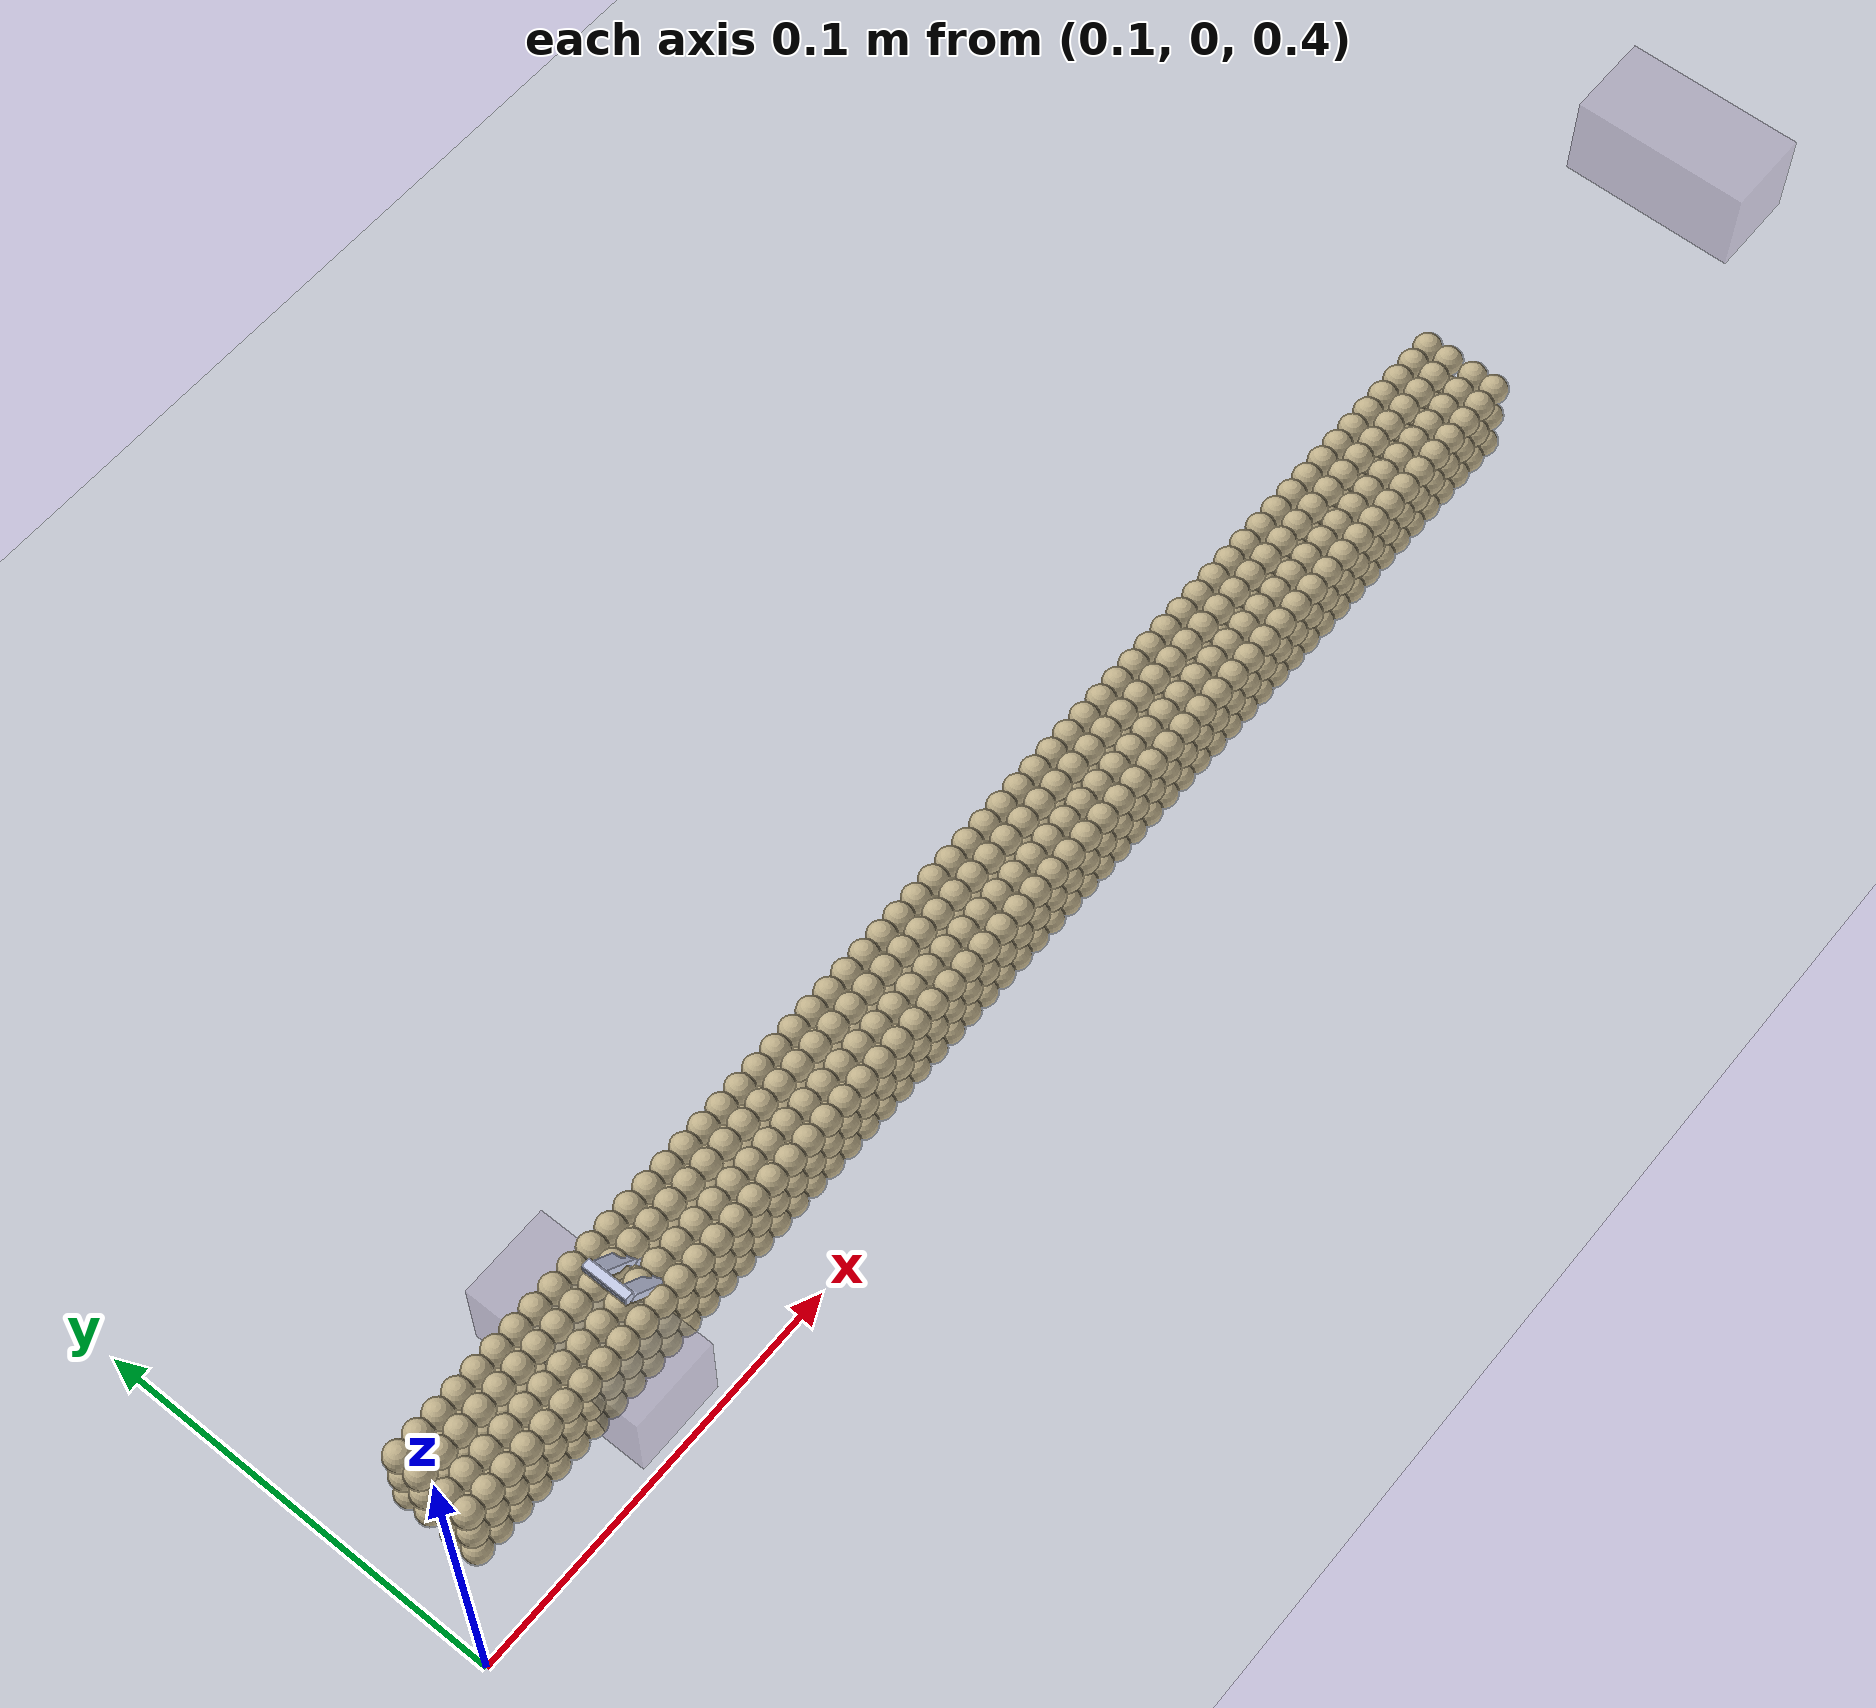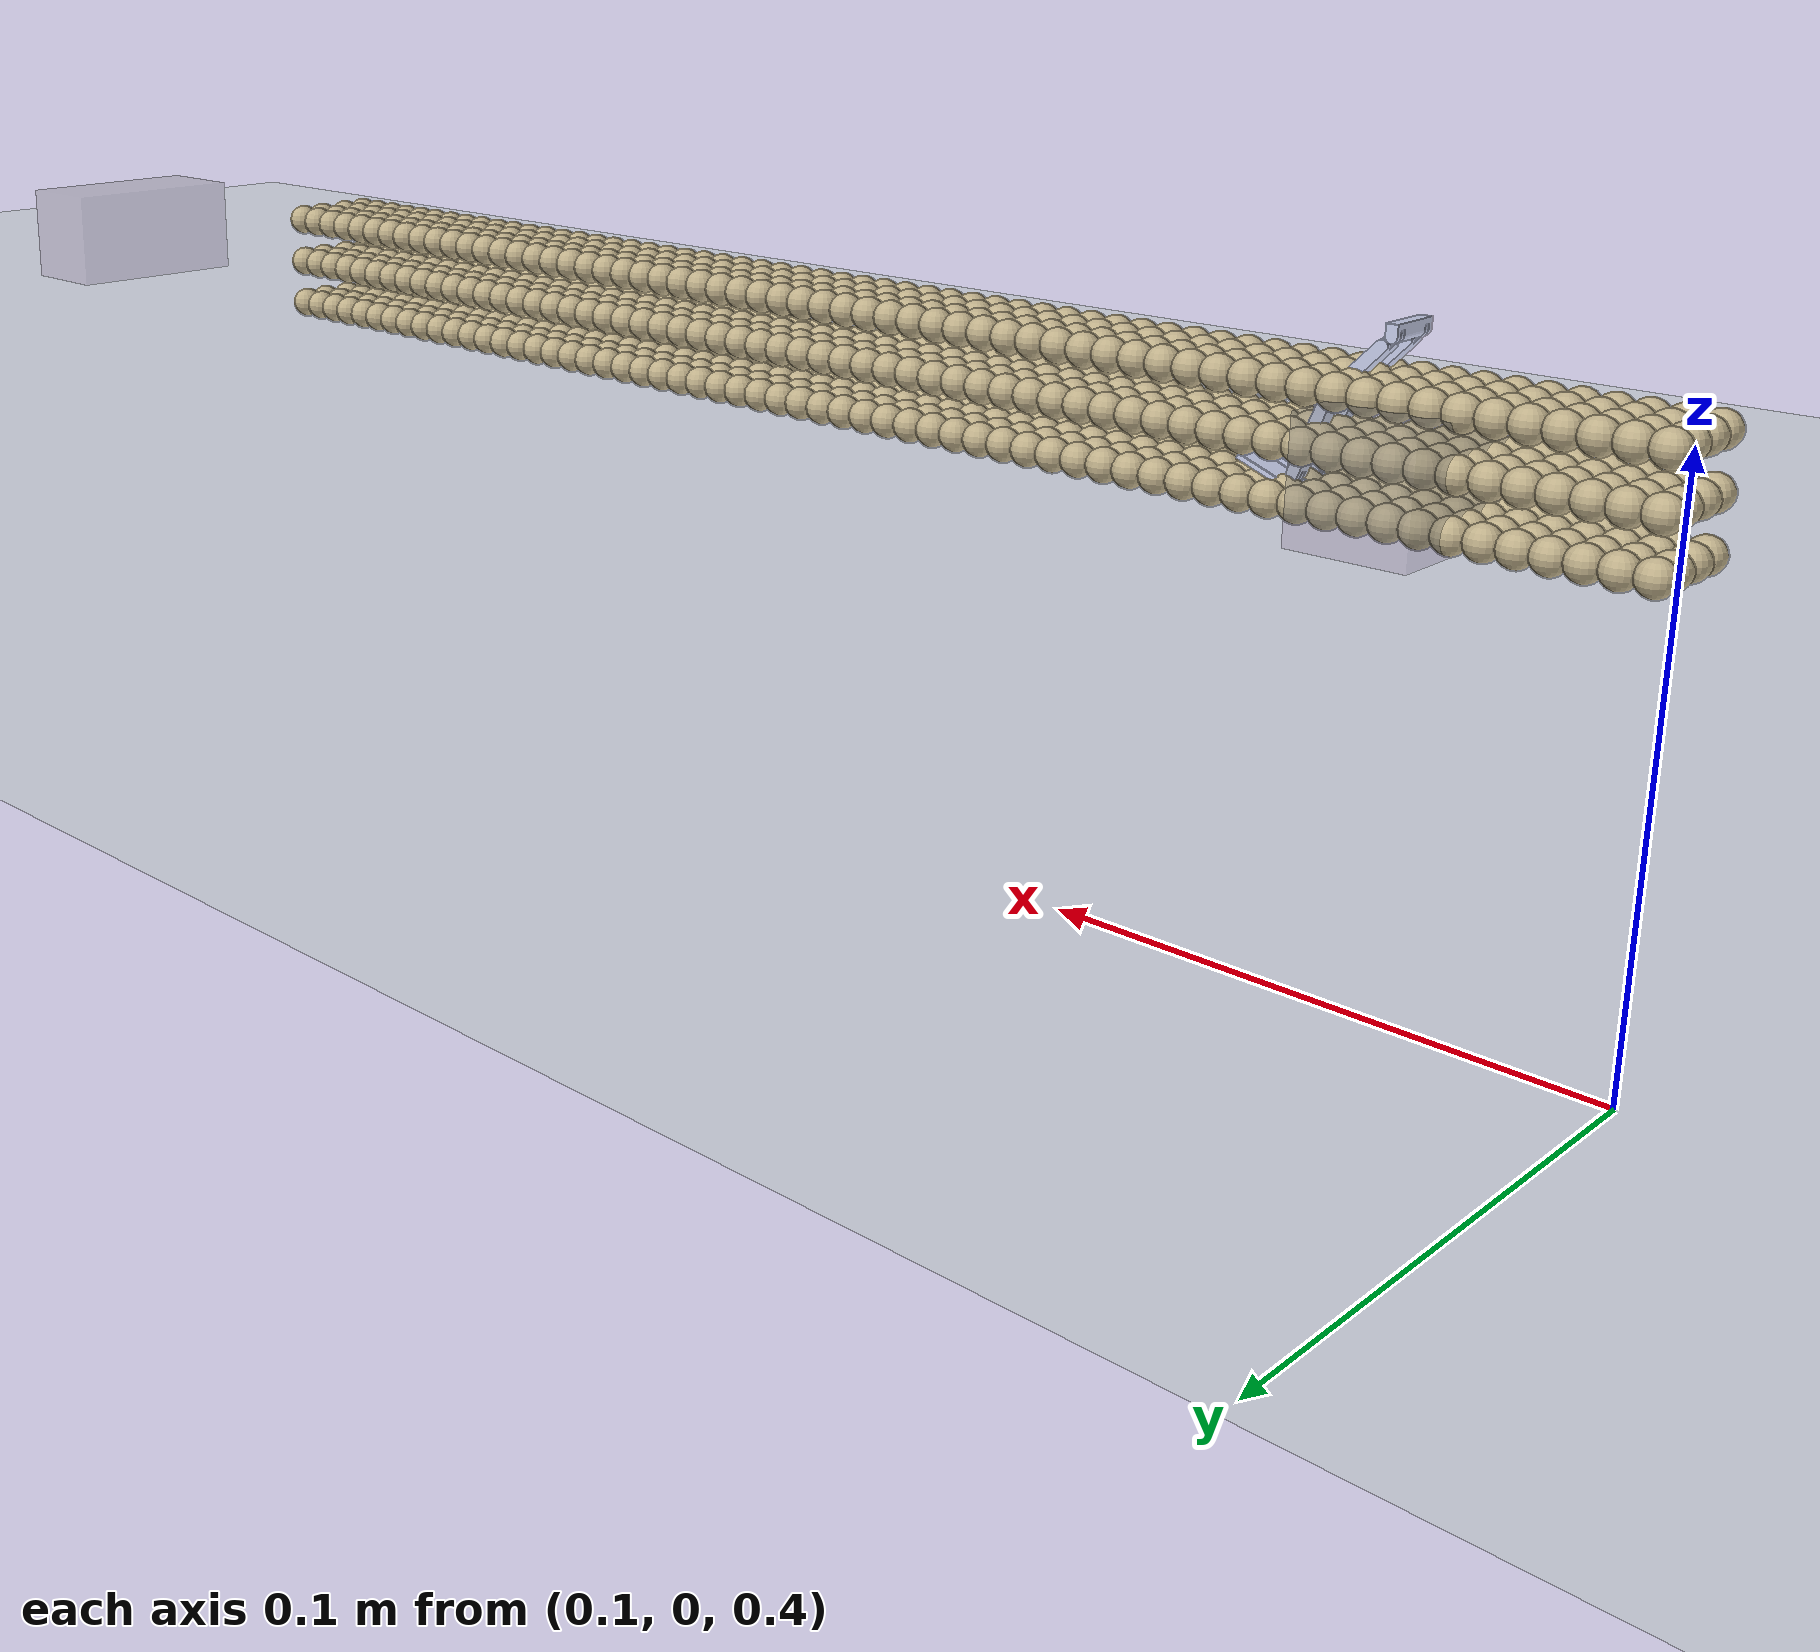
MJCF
<?xml version='1.0' encoding='utf-8'?>
<mujoco model="Robot_Walking_on_Sand">
  <compiler angle="radian" coordinate="local" />

  <option timestep="0.002" gravity="0 0 -9.81">
    <flag contact="enable" />
  </option>

  <default>
    <joint damping="0.001" armature="0.01" />
    <geom friction="0.5" density="1000" />
  </default>

  <asset>
    <mesh name="hip" content_type="model/stl" file="Legged_robot/meshes/hip.STL" />
    <mesh name="link_2_1" content_type="model/stl" file="Legged_robot/meshes/link_2_1.STL" />
    <mesh name="link_1_1" content_type="model/stl" file="Legged_robot/meshes/link_1_1.STL" />
    <mesh name="foot_1" content_type="model/stl" file="Legged_robot/meshes/foot_1.STL" />
    <mesh name="link_2_2" content_type="model/stl" file="Legged_robot/meshes/link_2_2.STL" />
    <mesh name="link_1_2" content_type="model/stl" file="Legged_robot/meshes/link_1_2.STL" />
    <mesh name="foot_2" content_type="model/stl" file="Legged_robot/meshes/foot_2.STL" />
  </asset>

  <worldbody>

    <geom name="floor" type="plane" pos="0.316 0 0.48" size="2 2 0.1" rgba="0.8 0.9 0.8 1" friction="0.5" />

    <body name="wall_back" pos="0.140 0.0 0.45">
      <geom type="box" size="0.01 0.02 0.05" rgba="0.5 0.5 0.5 0.3" friction="0.5" />
    </body>
    <body name="wall_front" pos="0.480 0.0 0.45">
      <geom type="box" size="0.01 0.02 0.05" rgba="0.5 0.5 0.5 0.3" friction="0.5" />
    </body>

    <body name="sand_0_0_0" pos="0.100 -0.008 0.483"><inertial mass="0.00001" pos="0 0 0" diaginertia="0.000000 0.000000 0.000000" /><geom type="sphere" size="0.003" rgba="0.76 0.70 0.55 1" friction="0.8 0.5 0.5" density="0.1" /></body>
    <body name="sand_0_0_1" pos="0.100 -0.003 0.483"><inertial mass="0.00001" pos="0 0 0" diaginertia="0.000000 0.000000 0.000000" /><geom type="sphere" size="0.003" rgba="0.76 0.70 0.55 1" friction="0.8 0.5 0.5" density="0.1" /></body>
    <body name="sand_0_0_2" pos="0.100 0.003 0.483"><inertial mass="0.00001" pos="0 0 0" diaginertia="0.000000 0.000000 0.000000" /><geom type="sphere" size="0.003" rgba="0.76 0.70 0.55 1" friction="0.8 0.5 0.5" density="0.1" /></body>
    <body name="sand_0_0_3" pos="0.100 0.008 0.483"><inertial mass="0.00001" pos="0 0 0" diaginertia="0.000000 0.000000 0.000000" /><geom type="sphere" size="0.003" rgba="0.76 0.70 0.55 1" friction="0.8 0.5 0.5" density="0.1" /></body>
    <body name="sand_0_1_0" pos="0.105 -0.008 0.483"><inertial mass="0.00001" pos="0 0 0" diaginertia="0.000000 0.000000 0.000000" /><geom type="sphere" size="0.003" rgba="0.76 0.70 0.55 1" friction="0.8 0.5 0.5" density="0.1" /></body>
    <body name="sand_0_1_1" pos="0.105 -0.003 0.483"><inertial mass="0.00001" pos="0 0 0" diaginertia="0.000000 0.000000 0.000000" /><geom type="sphere" size="0.003" rgba="0.76 0.70 0.55 1" friction="0.8 0.5 0.5" density="0.1" /></body>
    <body name="sand_0_1_2" pos="0.105 0.003 0.483"><inertial mass="0.00001" pos="0 0 0" diaginertia="0.000000 0.000000 0.000000" /><geom type="sphere" size="0.003" rgba="0.76 0.70 0.55 1" friction="0.8 0.5 0.5" density="0.1" /></body>
    <body name="sand_0_1_3" pos="0.105 0.008 0.483"><inertial mass="0.00001" pos="0 0 0" diaginertia="0.000000 0.000000 0.000000" /><geom type="sphere" size="0.003" rgba="0.76 0.70 0.55 1" friction="0.8 0.5 0.5" density="0.1" /></body>
    <body name="sand_0_2_0" pos="0.110 -0.008 0.483"><inertial mass="0.00001" pos="0 0 0" diaginertia="0.000000 0.000000 0.000000" /><geom type="sphere" size="0.003" rgba="0.76 0.70 0.55 1" friction="0.8 0.5 0.5" density="0.1" /></body>
    <body name="sand_0_2_1" pos="0.110 -0.003 0.483"><inertial mass="0.00001" pos="0 0 0" diaginertia="0.000000 0.000000 0.000000" /><geom type="sphere" size="0.003" rgba="0.76 0.70 0.55 1" friction="0.8 0.5 0.5" density="0.1" /></body>
    <body name="sand_0_2_2" pos="0.110 0.003 0.483"><inertial mass="0.00001" pos="0 0 0" diaginertia="0.000000 0.000000 0.000000" /><geom type="sphere" size="0.003" rgba="0.76 0.70 0.55 1" friction="0.8 0.5 0.5" density="0.1" /></body>
    <body name="sand_0_2_3" pos="0.110 0.008 0.483"><inertial mass="0.00001" pos="0 0 0" diaginertia="0.000000 0.000000 0.000000" /><geom type="sphere" size="0.003" rgba="0.76 0.70 0.55 1" friction="0.8 0.5 0.5" density="0.1" /></body>
    <body name="sand_0_3_0" pos="0.115 -0.008 0.483"><inertial mass="0.00001" pos="0 0 0" diaginertia="0.000000 0.000000 0.000000" /><geom type="sphere" size="0.003" rgba="0.76 0.70 0.55 1" friction="0.8 0.5 0.5" density="0.1" /></body>
    <body name="sand_0_3_1" pos="0.115 -0.003 0.483"><inertial mass="0.00001" pos="0 0 0" diaginertia="0.000000 0.000000 0.000000" /><geom type="sphere" size="0.003" rgba="0.76 0.70 0.55 1" friction="0.8 0.5 0.5" density="0.1" /></body>
    <body name="sand_0_3_2" pos="0.115 0.003 0.483"><inertial mass="0.00001" pos="0 0 0" diaginertia="0.000000 0.000000 0.000000" /><geom type="sphere" size="0.003" rgba="0.76 0.70 0.55 1" friction="0.8 0.5 0.5" density="0.1" /></body>
    <body name="sand_0_3_3" pos="0.115 0.008 0.483"><inertial mass="0.00001" pos="0 0 0" diaginertia="0.000000 0.000000 0.000000" /><geom type="sphere" size="0.003" rgba="0.76 0.70 0.55 1" friction="0.8 0.5 0.5" density="0.1" /></body>
    <body name="sand_0_4_0" pos="0.120 -0.008 0.483"><inertial mass="0.00001" pos="0 0 0" diaginertia="0.000000 0.000000 0.000000" /><geom type="sphere" size="0.003" rgba="0.76 0.70 0.55 1" friction="0.8 0.5 0.5" density="0.1" /></body>
    <body name="sand_0_4_1" pos="0.120 -0.003 0.483"><inertial mass="0.00001" pos="0 0 0" diaginertia="0.000000 0.000000 0.000000" /><geom type="sphere" size="0.003" rgba="0.76 0.70 0.55 1" friction="0.8 0.5 0.5" density="0.1" /></body>
    <body name="sand_0_4_2" pos="0.120 0.003 0.483"><inertial mass="0.00001" pos="0 0 0" diaginertia="0.000000 0.000000 0.000000" /><geom type="sphere" size="0.003" rgba="0.76 0.70 0.55 1" friction="0.8 0.5 0.5" density="0.1" /></body>
    <body name="sand_0_4_3" pos="0.120 0.008 0.483"><inertial mass="0.00001" pos="0 0 0" diaginertia="0.000000 0.000000 0.000000" /><geom type="sphere" size="0.003" rgba="0.76 0.70 0.55 1" friction="0.8 0.5 0.5" density="0.1" /></body>
    <body name="sand_0_5_0" pos="0.125 -0.008 0.483"><inertial mass="0.00001" pos="0 0 0" diaginertia="0.000000 0.000000 0.000000" /><geom type="sphere" size="0.003" rgba="0.76 0.70 0.55 1" friction="0.8 0.5 0.5" density="0.1" /></body>
    <body name="sand_0_5_1" pos="0.125 -0.003 0.483"><inertial mass="0.00001" pos="0 0 0" diaginertia="0.000000 0.000000 0.000000" /><geom type="sphere" size="0.003" rgba="0.76 0.70 0.55 1" friction="0.8 0.5 0.5" density="0.1" /></body>
    <body name="sand_0_5_2" pos="0.125 0.003 0.483"><inertial mass="0.00001" pos="0 0 0" diaginertia="0.000000 0.000000 0.000000" /><geom type="sphere" size="0.003" rgba="0.76 0.70 0.55 1" friction="0.8 0.5 0.5" density="0.1" /></body>
    <body name="sand_0_5_3" pos="0.125 0.008 0.483"><inertial mass="0.00001" pos="0 0 0" diaginertia="0.000000 0.000000 0.000000" /><geom type="sphere" size="0.003" rgba="0.76 0.70 0.55 1" friction="0.8 0.5 0.5" density="0.1" /></body>
    <body name="sand_0_6_0" pos="0.130 -0.008 0.483"><inertial mass="0.00001" pos="0 0 0" diaginertia="0.000000 0.000000 0.000000" /><geom type="sphere" size="0.003" rgba="0.76 0.70 0.55 1" friction="0.8 0.5 0.5" density="0.1" /></body>
    <body name="sand_0_6_1" pos="0.130 -0.003 0.483"><inertial mass="0.00001" pos="0 0 0" diaginertia="0.000000 0.000000 0.000000" /><geom type="sphere" size="0.003" rgba="0.76 0.70 0.55 1" friction="0.8 0.5 0.5" density="0.1" /></body>
    <body name="sand_0_6_2" pos="0.130 0.003 0.483"><inertial mass="0.00001" pos="0 0 0" diaginertia="0.000000 0.000000 0.000000" /><geom type="sphere" size="0.003" rgba="0.76 0.70 0.55 1" friction="0.8 0.5 0.5" density="0.1" /></body>
    <body name="sand_0_6_3" pos="0.130 0.008 0.483"><inertial mass="0.00001" pos="0 0 0" diaginertia="0.000000 0.000000 0.000000" /><geom type="sphere" size="0.003" rgba="0.76 0.70 0.55 1" friction="0.8 0.5 0.5" density="0.1" /></body>
    <body name="sand_0_7_0" pos="0.135 -0.008 0.483"><inertial mass="0.00001" pos="0 0 0" diaginertia="0.000000 0.000000 0.000000" /><geom type="sphere" size="0.003" rgba="0.76 0.70 0.55 1" friction="0.8 0.5 0.5" density="0.1" /></body>
    <body name="sand_0_7_1" pos="0.135 -0.003 0.483"><inertial mass="0.00001" pos="0 0 0" diaginertia="0.000000 0.000000 0.000000" /><geom type="sphere" size="0.003" rgba="0.76 0.70 0.55 1" friction="0.8 0.5 0.5" density="0.1" /></body>
    <body name="sand_0_7_2" pos="0.135 0.003 0.483"><inertial mass="0.00001" pos="0 0 0" diaginertia="0.000000 0.000000 0.000000" /><geom type="sphere" size="0.003" rgba="0.76 0.70 0.55 1" friction="0.8 0.5 0.5" density="0.1" /></body>
    <body name="sand_0_7_3" pos="0.135 0.008 0.483"><inertial mass="0.00001" pos="0 0 0" diaginertia="0.000000 0.000000 0.000000" /><geom type="sphere" size="0.003" rgba="0.76 0.70 0.55 1" friction="0.8 0.5 0.5" density="0.1" /></body>
    <body name="sand_0_8_0" pos="0.140 -0.008 0.483"><inertial mass="0.00001" pos="0 0 0" diaginertia="0.000000 0.000000 0.000000" /><geom type="sphere" size="0.003" rgba="0.76 0.70 0.55 1" friction="0.8 0.5 0.5" density="0.1" /></body>
    <body name="sand_0_8_1" pos="0.140 -0.003 0.483"><inertial mass="0.00001" pos="0 0 0" diaginertia="0.000000 0.000000 0.000000" /><geom type="sphere" size="0.003" rgba="0.76 0.70 0.55 1" friction="0.8 0.5 0.5" density="0.1" /></body>
    <body name="sand_0_8_2" pos="0.140 0.003 0.483"><inertial mass="0.00001" pos="0 0 0" diaginertia="0.000000 0.000000 0.000000" /><geom type="sphere" size="0.003" rgba="0.76 0.70 0.55 1" friction="0.8 0.5 0.5" density="0.1" /></body>
    <body name="sand_0_8_3" pos="0.140 0.008 0.483"><inertial mass="0.00001" pos="0 0 0" diaginertia="0.000000 0.000000 0.000000" /><geom type="sphere" size="0.003" rgba="0.76 0.70 0.55 1" friction="0.8 0.5 0.5" density="0.1" /></body>
    <body name="sand_0_9_0" pos="0.145 -0.008 0.483"><inertial mass="0.00001" pos="0 0 0" diaginertia="0.000000 0.000000 0.000000" /><geom type="sphere" size="0.003" rgba="0.76 0.70 0.55 1" friction="0.8 0.5 0.5" density="0.1" /></body>
    <body name="sand_0_9_1" pos="0.145 -0.003 0.483"><inertial mass="0.00001" pos="0 0 0" diaginertia="0.000000 0.000000 0.000000" /><geom type="sphere" size="0.003" rgba="0.76 0.70 0.55 1" friction="0.8 0.5 0.5" density="0.1" /></body>
    <body name="sand_0_9_2" pos="0.145 0.003 0.483"><inertial mass="0.00001" pos="0 0 0" diaginertia="0.000000 0.000000 0.000000" /><geom type="sphere" size="0.003" rgba="0.76 0.70 0.55 1" friction="0.8 0.5 0.5" density="0.1" /></body>
    <body name="sand_0_9_3" pos="0.145 0.008 0.483"><inertial mass="0.00001" pos="0 0 0" diaginertia="0.000000 0.000000 0.000000" /><geom type="sphere" size="0.003" rgba="0.76 0.70 0.55 1" friction="0.8 0.5 0.5" density="0.1" /></body>
    <body name="sand_0_10_0" pos="0.150 -0.008 0.483"><inertial mass="0.00001" pos="0 0 0" diaginertia="0.000000 0.000000 0.000000" /><geom type="sphere" size="0.003" rgba="0.76 0.70 0.55 1" friction="0.8 0.5 0.5" density="0.1" /></body>
    <body name="sand_0_10_1" pos="0.150 -0.003 0.483"><inertial mass="0.00001" pos="0 0 0" diaginertia="0.000000 0.000000 0.000000" /><geom type="sphere" size="0.003" rgba="0.76 0.70 0.55 1" friction="0.8 0.5 0.5" density="0.1" /></body>
    <body name="sand_0_10_2" pos="0.150 0.003 0.483"><inertial mass="0.00001" pos="0 0 0" diaginertia="0.000000 0.000000 0.000000" /><geom type="sphere" size="0.003" rgba="0.76 0.70 0.55 1" friction="0.8 0.5 0.5" density="0.1" /></body>
    <body name="sand_0_10_3" pos="0.150 0.008 0.483"><inertial mass="0.00001" pos="0 0 0" diaginertia="0.000000 0.000000 0.000000" /><geom type="sphere" size="0.003" rgba="0.76 0.70 0.55 1" friction="0.8 0.5 0.5" density="0.1" /></body>
    <body name="sand_0_11_0" pos="0.155 -0.008 0.483"><inertial mass="0.00001" pos="0 0 0" diaginertia="0.000000 0.000000 0.000000" /><geom type="sphere" size="0.003" rgba="0.76 0.70 0.55 1" friction="0.8 0.5 0.5" density="0.1" /></body>
    <body name="sand_0_11_1" pos="0.155 -0.003 0.483"><inertial mass="0.00001" pos="0 0 0" diaginertia="0.000000 0.000000 0.000000" /><geom type="sphere" size="0.003" rgba="0.76 0.70 0.55 1" friction="0.8 0.5 0.5" density="0.1" /></body>
    <body name="sand_0_11_2" pos="0.155 0.003 0.483"><inertial mass="0.00001" pos="0 0 0" diaginertia="0.000000 0.000000 0.000000" /><geom type="sphere" size="0.003" rgba="0.76 0.70 0.55 1" friction="0.8 0.5 0.5" density="0.1" /></body>
    <body name="sand_0_11_3" pos="0.155 0.008 0.483"><inertial mass="0.00001" pos="0 0 0" diaginertia="0.000000 0.000000 0.000000" /><geom type="sphere" size="0.003" rgba="0.76 0.70 0.55 1" friction="0.8 0.5 0.5" density="0.1" /></body>
    <body name="sand_0_12_0" pos="0.160 -0.008 0.483"><inertial mass="0.00001" pos="0 0 0" diaginertia="0.000000 0.000000 0.000000" /><geom type="sphere" size="0.003" rgba="0.76 0.70 0.55 1" friction="0.8 0.5 0.5" density="0.1" /></body>
    <body name="sand_0_12_1" pos="0.160 -0.003 0.483"><inertial mass="0.00001" pos="0 0 0" diaginertia="0.000000 0.000000 0.000000" /><geom type="sphere" size="0.003" rgba="0.76 0.70 0.55 1" friction="0.8 0.5 0.5" density="0.1" /></body>
    <body name="sand_0_12_2" pos="0.160 0.003 0.483"><inertial mass="0.00001" pos="0 0 0" diaginertia="0.000000 0.000000 0.000000" /><geom type="sphere" size="0.003" rgba="0.76 0.70 0.55 1" friction="0.8 0.5 0.5" density="0.1" /></body>
    <body name="sand_0_12_3" pos="0.160 0.008 0.483"><inertial mass="0.00001" pos="0 0 0" diaginertia="0.000000 0.000000 0.000000" /><geom type="sphere" size="0.003" rgba="0.76 0.70 0.55 1" friction="0.8 0.5 0.5" density="0.1" /></body>
    <body name="sand_0_13_0" pos="0.165 -0.008 0.483"><inertial mass="0.00001" pos="0 0 0" diaginertia="0.000000 0.000000 0.000000" /><geom type="sphere" size="0.003" rgba="0.76 0.70 0.55 1" friction="0.8 0.5 0.5" density="0.1" /></body>
    <body name="sand_0_13_1" pos="0.165 -0.003 0.483"><inertial mass="0.00001" pos="0 0 0" diaginertia="0.000000 0.000000 0.000000" /><geom type="sphere" size="0.003" rgba="0.76 0.70 0.55 1" friction="0.8 0.5 0.5" density="0.1" /></body>
    <body name="sand_0_13_2" pos="0.165 0.003 0.483"><inertial mass="0.00001" pos="0 0 0" diaginertia="0.000000 0.000000 0.000000" /><geom type="sphere" size="0.003" rgba="0.76 0.70 0.55 1" friction="0.8 0.5 0.5" density="0.1" /></body>
    <body name="sand_0_13_3" pos="0.165 0.008 0.483"><inertial mass="0.00001" pos="0 0 0" diaginertia="0.000000 0.000000 0.000000" /><geom type="sphere" size="0.003" rgba="0.76 0.70 0.55 1" friction="0.8 0.5 0.5" density="0.1" /></body>
    <body name="sand_0_14_0" pos="0.170 -0.008 0.483"><inertial mass="0.00001" pos="0 0 0" diaginertia="0.000000 0.000000 0.000000" /><geom type="sphere" size="0.003" rgba="0.76 0.70 0.55 1" friction="0.8 0.5 0.5" density="0.1" /></body>
    <body name="sand_0_14_1" pos="0.170 -0.003 0.483"><inertial mass="0.00001" pos="0 0 0" diaginertia="0.000000 0.000000 0.000000" /><geom type="sphere" size="0.003" rgba="0.76 0.70 0.55 1" friction="0.8 0.5 0.5" density="0.1" /></body>
    <body name="sand_0_14_2" pos="0.170 0.003 0.483"><inertial mass="0.00001" pos="0 0 0" diaginertia="0.000000 0.000000 0.000000" /><geom type="sphere" size="0.003" rgba="0.76 0.70 0.55 1" friction="0.8 0.5 0.5" density="0.1" /></body>
    <body name="sand_0_14_3" pos="0.170 0.008 0.483"><inertial mass="0.00001" pos="0 0 0" diaginertia="0.000000 0.000000 0.000000" /><geom type="sphere" size="0.003" rgba="0.76 0.70 0.55 1" friction="0.8 0.5 0.5" density="0.1" /></body>
    <body name="sand_0_15_0" pos="0.175 -0.008 0.483"><inertial mass="0.00001" pos="0 0 0" diaginertia="0.000000 0.000000 0.000000" /><geom type="sphere" size="0.003" rgba="0.76 0.70 0.55 1" friction="0.8 0.5 0.5" density="0.1" /></body>
    <body name="sand_0_15_1" pos="0.175 -0.003 0.483"><inertial mass="0.00001" pos="0 0 0" diaginertia="0.000000 0.000000 0.000000" /><geom type="sphere" size="0.003" rgba="0.76 0.70 0.55 1" friction="0.8 0.5 0.5" density="0.1" /></body>
    <body name="sand_0_15_2" pos="0.175 0.003 0.483"><inertial mass="0.00001" pos="0 0 0" diaginertia="0.000000 0.000000 0.000000" /><geom type="sphere" size="0.003" rgba="0.76 0.70 0.55 1" friction="0.8 0.5 0.5" density="0.1" /></body>
    <body name="sand_0_15_3" pos="0.175 0.008 0.483"><inertial mass="0.00001" pos="0 0 0" diaginertia="0.000000 0.000000 0.000000" /><geom type="sphere" size="0.003" rgba="0.76 0.70 0.55 1" friction="0.8 0.5 0.5" density="0.1" /></body>
    <body name="sand_0_16_0" pos="0.180 -0.008 0.483"><inertial mass="0.00001" pos="0 0 0" diaginertia="0.000000 0.000000 0.000000" /><geom type="sphere" size="0.003" rgba="0.76 0.70 0.55 1" friction="0.8 0.5 0.5" density="0.1" /></body>
    <body name="sand_0_16_1" pos="0.180 -0.003 0.483"><inertial mass="0.00001" pos="0 0 0" diaginertia="0.000000 0.000000 0.000000" /><geom type="sphere" size="0.003" rgba="0.76 0.70 0.55 1" friction="0.8 0.5 0.5" density="0.1" /></body>
    <body name="sand_0_16_2" pos="0.180 0.003 0.483"><inertial mass="0.00001" pos="0 0 0" diaginertia="0.000000 0.000000 0.000000" /><geom type="sphere" size="0.003" rgba="0.76 0.70 0.55 1" friction="0.8 0.5 0.5" density="0.1" /></body>
    <body name="sand_0_16_3" pos="0.180 0.008 0.483"><inertial mass="0.00001" pos="0 0 0" diaginertia="0.000000 0.000000 0.000000" /><geom type="sphere" size="0.003" rgba="0.76 0.70 0.55 1" friction="0.8 0.5 0.5" density="0.1" /></body>
    <body name="sand_0_17_0" pos="0.185 -0.008 0.483"><inertial mass="0.00001" pos="0 0 0" diaginertia="0.000000 0.000000 0.000000" /><geom type="sphere" size="0.003" rgba="0.76 0.70 0.55 1" friction="0.8 0.5 0.5" density="0.1" /></body>
    <body name="sand_0_17_1" pos="0.185 -0.003 0.483"><inertial mass="0.00001" pos="0 0 0" diaginertia="0.000000 0.000000 0.000000" /><geom type="sphere" size="0.003" rgba="0.76 0.70 0.55 1" friction="0.8 0.5 0.5" density="0.1" /></body>
    <body name="sand_0_17_2" pos="0.185 0.003 0.483"><inertial mass="0.00001" pos="0 0 0" diaginertia="0.000000 0.000000 0.000000" /><geom type="sphere" size="0.003" rgba="0.76 0.70 0.55 1" friction="0.8 0.5 0.5" density="0.1" /></body>
    <body name="sand_0_17_3" pos="0.185 0.008 0.483"><inertial mass="0.00001" pos="0 0 0" diaginertia="0.000000 0.000000 0.000000" /><geom type="sphere" size="0.003" rgba="0.76 0.70 0.55 1" friction="0.8 0.5 0.5" density="0.1" /></body>
    <body name="sand_0_18_0" pos="0.190 -0.008 0.483"><inertial mass="0.00001" pos="0 0 0" diaginertia="0.000000 0.000000 0.000000" /><geom type="sphere" size="0.003" rgba="0.76 0.70 0.55 1" friction="0.8 0.5 0.5" density="0.1" /></body>
    <body name="sand_0_18_1" pos="0.190 -0.003 0.483"><inertial mass="0.00001" pos="0 0 0" diaginertia="0.000000 0.000000 0.000000" /><geom type="sphere" size="0.003" rgba="0.76 0.70 0.55 1" friction="0.8 0.5 0.5" density="0.1" /></body>
    <body name="sand_0_18_2" pos="0.190 0.003 0.483"><inertial mass="0.00001" pos="0 0 0" diaginertia="0.000000 0.000000 0.000000" /><geom type="sphere" size="0.003" rgba="0.76 0.70 0.55 1" friction="0.8 0.5 0.5" density="0.1" /></body>
    <body name="sand_0_18_3" pos="0.190 0.008 0.483"><inertial mass="0.00001" pos="0 0 0" diaginertia="0.000000 0.000000 0.000000" /><geom type="sphere" size="0.003" rgba="0.76 0.70 0.55 1" friction="0.8 0.5 0.5" density="0.1" /></body>
    <body name="sand_0_19_0" pos="0.195 -0.008 0.483"><inertial mass="0.00001" pos="0 0 0" diaginertia="0.000000 0.000000 0.000000" /><geom type="sphere" size="0.003" rgba="0.76 0.70 0.55 1" friction="0.8 0.5 0.5" density="0.1" /></body>
    <body name="sand_0_19_1" pos="0.195 -0.003 0.483"><inertial mass="0.00001" pos="0 0 0" diaginertia="0.000000 0.000000 0.000000" /><geom type="sphere" size="0.003" rgba="0.76 0.70 0.55 1" friction="0.8 0.5 0.5" density="0.1" /></body>
    <body name="sand_0_19_2" pos="0.195 0.003 0.483"><inertial mass="0.00001" pos="0 0 0" diaginertia="0.000000 0.000000 0.000000" /><geom type="sphere" size="0.003" rgba="0.76 0.70 0.55 1" friction="0.8 0.5 0.5" density="0.1" /></body>
    <body name="sand_0_19_3" pos="0.195 0.008 0.483"><inertial mass="0.00001" pos="0 0 0" diaginertia="0.000000 0.000000 0.000000" /><geom type="sphere" size="0.003" rgba="0.76 0.70 0.55 1" friction="0.8 0.5 0.5" density="0.1" /></body>
    <body name="sand_0_20_0" pos="0.200 -0.008 0.483"><inertial mass="0.00001" pos="0 0 0" diaginertia="0.000000 0.000000 0.000000" /><geom type="sphere" size="0.003" rgba="0.76 0.70 0.55 1" friction="0.8 0.5 0.5" density="0.1" /></body>
    <body name="sand_0_20_1" pos="0.200 -0.003 0.483"><inertial mass="0.00001" pos="0 0 0" diaginertia="0.000000 0.000000 0.000000" /><geom type="sphere" size="0.003" rgba="0.76 0.70 0.55 1" friction="0.8 0.5 0.5" density="0.1" /></body>
    <body name="sand_0_20_2" pos="0.200 0.003 0.483"><inertial mass="0.00001" pos="0 0 0" diaginertia="0.000000 0.000000 0.000000" /><geom type="sphere" size="0.003" rgba="0.76 0.70 0.55 1" friction="0.8 0.5 0.5" density="0.1" /></body>
    <body name="sand_0_20_3" pos="0.200 0.008 0.483"><inertial mass="0.00001" pos="0 0 0" diaginertia="0.000000 0.000000 0.000000" /><geom type="sphere" size="0.003" rgba="0.76 0.70 0.55 1" friction="0.8 0.5 0.5" density="0.1" /></body>
    <body name="sand_0_21_0" pos="0.205 -0.008 0.483"><inertial mass="0.00001" pos="0 0 0" diaginertia="0.000000 0.000000 0.000000" /><geom type="sphere" size="0.003" rgba="0.76 0.70 0.55 1" friction="0.8 0.5 0.5" density="0.1" /></body>
    <body name="sand_0_21_1" pos="0.205 -0.003 0.483"><inertial mass="0.00001" pos="0 0 0" diaginertia="0.000000 0.000000 0.000000" /><geom type="sphere" size="0.003" rgba="0.76 0.70 0.55 1" friction="0.8 0.5 0.5" density="0.1" /></body>
    <body name="sand_0_21_2" pos="0.205 0.003 0.483"><inertial mass="0.00001" pos="0 0 0" diaginertia="0.000000 0.000000 0.000000" /><geom type="sphere" size="0.003" rgba="0.76 0.70 0.55 1" friction="0.8 0.5 0.5" density="0.1" /></body>
    <body name="sand_0_21_3" pos="0.205 0.008 0.483"><inertial mass="0.00001" pos="0 0 0" diaginertia="0.000000 0.000000 0.000000" /><geom type="sphere" size="0.003" rgba="0.76 0.70 0.55 1" friction="0.8 0.5 0.5" density="0.1" /></body>
    <body name="sand_0_22_0" pos="0.210 -0.008 0.483"><inertial mass="0.00001" pos="0 0 0" diaginertia="0.000000 0.000000 0.000000" /><geom type="sphere" size="0.003" rgba="0.76 0.70 0.55 1" friction="0.8 0.5 0.5" density="0.1" /></body>
    <body name="sand_0_22_1" pos="0.210 -0.003 0.483"><inertial mass="0.00001" pos="0 0 0" diaginertia="0.000000 0.000000 0.000000" /><geom type="sphere" size="0.003" rgba="0.76 0.70 0.55 1" friction="0.8 0.5 0.5" density="0.1" /></body>
    <body name="sand_0_22_2" pos="0.210 0.003 0.483"><inertial mass="0.00001" pos="0 0 0" diaginertia="0.000000 0.000000 0.000000" /><geom type="sphere" size="0.003" rgba="0.76 0.70 0.55 1" friction="0.8 0.5 0.5" density="0.1" /></body>
    <body name="sand_0_22_3" pos="0.210 0.008 0.483"><inertial mass="0.00001" pos="0 0 0" diaginertia="0.000000 0.000000 0.000000" /><geom type="sphere" size="0.003" rgba="0.76 0.70 0.55 1" friction="0.8 0.5 0.5" density="0.1" /></body>
    <body name="sand_0_23_0" pos="0.215 -0.008 0.483"><inertial mass="0.00001" pos="0 0 0" diaginertia="0.000000 0.000000 0.000000" /><geom type="sphere" size="0.003" rgba="0.76 0.70 0.55 1" friction="0.8 0.5 0.5" density="0.1" /></body>
    <body name="sand_0_23_1" pos="0.215 -0.003 0.483"><inertial mass="0.00001" pos="0 0 0" diaginertia="0.000000 0.000000 0.000000" /><geom type="sphere" size="0.003" rgba="0.76 0.70 0.55 1" friction="0.8 0.5 0.5" density="0.1" /></body>
    <body name="sand_0_23_2" pos="0.215 0.003 0.483"><inertial mass="0.00001" pos="0 0 0" diaginertia="0.000000 0.000000 0.000000" /><geom type="sphere" size="0.003" rgba="0.76 0.70 0.55 1" friction="0.8 0.5 0.5" density="0.1" /></body>
    <body name="sand_0_23_3" pos="0.215 0.008 0.483"><inertial mass="0.00001" pos="0 0 0" diaginertia="0.000000 0.000000 0.000000" /><geom type="sphere" size="0.003" rgba="0.76 0.70 0.55 1" friction="0.8 0.5 0.5" density="0.1" /></body>
    <body name="sand_0_24_0" pos="0.220 -0.008 0.483"><inertial mass="0.00001" pos="0 0 0" diaginertia="0.000000 0.000000 0.000000" /><geom type="sphere" size="0.003" rgba="0.76 0.70 0.55 1" friction="0.8 0.5 0.5" density="0.1" /></body>
    <body name="sand_0_24_1" pos="0.220 -0.003 0.483"><inertial mass="0.00001" pos="0 0 0" diaginertia="0.000000 0.000000 0.000000" /><geom type="sphere" size="0.003" rgba="0.76 0.70 0.55 1" friction="0.8 0.5 0.5" density="0.1" /></body>
    <body name="sand_0_24_2" pos="0.220 0.003 0.483"><inertial mass="0.00001" pos="0 0 0" diaginertia="0.000000 0.000000 0.000000" /><geom type="sphere" size="0.003" rgba="0.76 0.70 0.55 1" friction="0.8 0.5 0.5" density="0.1" /></body>
    <body name="sand_0_24_3" pos="0.220 0.008 0.483"><inertial mass="0.00001" pos="0 0 0" diaginertia="0.000000 0.000000 0.000000" /><geom type="sphere" size="0.003" rgba="0.76 0.70 0.55 1" friction="0.8 0.5 0.5" density="0.1" /></body>
    <body name="sand_0_25_0" pos="0.225 -0.008 0.483"><inertial mass="0.00001" pos="0 0 0" diaginertia="0.000000 0.000000 0.000000" /><geom type="sphere" size="0.003" rgba="0.76 0.70 0.55 1" friction="0.8 0.5 0.5" density="0.1" /></body>
    <body name="sand_0_25_1" pos="0.225 -0.003 0.483"><inertial mass="0.00001" pos="0 0 0" diaginertia="0.000000 0.000000 0.000000" /><geom type="sphere" size="0.003" rgba="0.76 0.70 0.55 1" friction="0.8 0.5 0.5" density="0.1" /></body>
    <body name="sand_0_25_2" pos="0.225 0.003 0.483"><inertial mass="0.00001" pos="0 0 0" diaginertia="0.000000 0.000000 0.000000" /><geom type="sphere" size="0.003" rgba="0.76 0.70 0.55 1" friction="0.8 0.5 0.5" density="0.1" /></body>
    <body name="sand_0_25_3" pos="0.225 0.008 0.483"><inertial mass="0.00001" pos="0 0 0" diaginertia="0.000000 0.000000 0.000000" /><geom type="sphere" size="0.003" rgba="0.76 0.70 0.55 1" friction="0.8 0.5 0.5" density="0.1" /></body>
    <body name="sand_0_26_0" pos="0.230 -0.008 0.483"><inertial mass="0.00001" pos="0 0 0" diaginertia="0.000000 0.000000 0.000000" /><geom type="sphere" size="0.003" rgba="0.76 0.70 0.55 1" friction="0.8 0.5 0.5" density="0.1" /></body>
    <body name="sand_0_26_1" pos="0.230 -0.003 0.483"><inertial mass="0.00001" pos="0 0 0" diaginertia="0.000000 0.000000 0.000000" /><geom type="sphere" size="0.003" rgba="0.76 0.70 0.55 1" friction="0.8 0.5 0.5" density="0.1" /></body>
    <body name="sand_0_26_2" pos="0.230 0.003 0.483"><inertial mass="0.00001" pos="0 0 0" diaginertia="0.000000 0.000000 0.000000" /><geom type="sphere" size="0.003" rgba="0.76 0.70 0.55 1" friction="0.8 0.5 0.5" density="0.1" /></body>
    <body name="sand_0_26_3" pos="0.230 0.008 0.483"><inertial mass="0.00001" pos="0 0 0" diaginertia="0.000000 0.000000 0.000000" /><geom type="sphere" size="0.003" rgba="0.76 0.70 0.55 1" friction="0.8 0.5 0.5" density="0.1" /></body>
    <body name="sand_0_27_0" pos="0.235 -0.008 0.483"><inertial mass="0.00001" pos="0 0 0" diaginertia="0.000000 0.000000 0.000000" /><geom type="sphere" size="0.003" rgba="0.76 0.70 0.55 1" friction="0.8 0.5 0.5" density="0.1" /></body>
    <body name="sand_0_27_1" pos="0.235 -0.003 0.483"><inertial mass="0.00001" pos="0 0 0" diaginertia="0.000000 0.000000 0.000000" /><geom type="sphere" size="0.003" rgba="0.76 0.70 0.55 1" friction="0.8 0.5 0.5" density="0.1" /></body>
    <body name="sand_0_27_2" pos="0.235 0.003 0.483"><inertial mass="0.00001" pos="0 0 0" diaginertia="0.000000 0.000000 0.000000" /><geom type="sphere" size="0.003" rgba="0.76 0.70 0.55 1" friction="0.8 0.5 0.5" density="0.1" /></body>
    <body name="sand_0_27_3" pos="0.235 0.008 0.483"><inertial mass="0.00001" pos="0 0 0" diaginertia="0.000000 0.000000 0.000000" /><geom type="sphere" size="0.003" rgba="0.76 0.70 0.55 1" friction="0.8 0.5 0.5" density="0.1" /></body>
    <body name="sand_0_28_0" pos="0.240 -0.008 0.483"><inertial mass="0.00001" pos="0 0 0" diaginertia="0.000000 0.000000 0.000000" /><geom type="sphere" size="0.003" rgba="0.76 0.70 0.55 1" friction="0.8 0.5 0.5" density="0.1" /></body>
    <body name="sand_0_28_1" pos="0.240 -0.003 0.483"><inertial mass="0.00001" pos="0 0 0" diaginertia="0.000000 0.000000 0.000000" /><geom type="sphere" size="0.003" rgba="0.76 0.70 0.55 1" friction="0.8 0.5 0.5" density="0.1" /></body>
    <body name="sand_0_28_2" pos="0.240 0.003 0.483"><inertial mass="0.00001" pos="0 0 0" diaginertia="0.000000 0.000000 0.000000" /><geom type="sphere" size="0.003" rgba="0.76 0.70 0.55 1" friction="0.8 0.5 0.5" density="0.1" /></body>
    <body name="sand_0_28_3" pos="0.240 0.008 0.483"><inertial mass="0.00001" pos="0 0 0" diaginertia="0.000000 0.000000 0.000000" /><geom type="sphere" size="0.003" rgba="0.76 0.70 0.55 1" friction="0.8 0.5 0.5" density="0.1" /></body>
    <body name="sand_0_29_0" pos="0.245 -0.008 0.483"><inertial mass="0.00001" pos="0 0 0" diaginertia="0.000000 0.000000 0.000000" /><geom type="sphere" size="0.003" rgba="0.76 0.70 0.55 1" friction="0.8 0.5 0.5" density="0.1" /></body>
    <body name="sand_0_29_1" pos="0.245 -0.003 0.483"><inertial mass="0.00001" pos="0 0 0" diaginertia="0.000000 0.000000 0.000000" /><geom type="sphere" size="0.003" rgba="0.76 0.70 0.55 1" friction="0.8 0.5 0.5" density="0.1" /></body>
    <body name="sand_0_29_2" pos="0.245 0.003 0.483"><inertial mass="0.00001" pos="0 0 0" diaginertia="0.000000 0.000000 0.000000" /><geom type="sphere" size="0.003" rgba="0.76 0.70 0.55 1" friction="0.8 0.5 0.5" density="0.1" /></body>
    <body name="sand_0_29_3" pos="0.245 0.008 0.483"><inertial mass="0.00001" pos="0 0 0" diaginertia="0.000000 0.000000 0.000000" /><geom type="sphere" size="0.003" rgba="0.76 0.70 0.55 1" friction="0.8 0.5 0.5" density="0.1" /></body>
    <body name="sand_0_30_0" pos="0.250 -0.008 0.483"><inertial mass="0.00001" pos="0 0 0" diaginertia="0.000000 0.000000 0.000000" /><geom type="sphere" size="0.003" rgba="0.76 0.70 0.55 1" friction="0.8 0.5 0.5" density="0.1" /></body>
    <body name="sand_0_30_1" pos="0.250 -0.003 0.483"><inertial mass="0.00001" pos="0 0 0" diaginertia="0.000000 0.000000 0.000000" /><geom type="sphere" size="0.003" rgba="0.76 0.70 0.55 1" friction="0.8 0.5 0.5" density="0.1" /></body>
    <body name="sand_0_30_2" pos="0.250 0.003 0.483"><inertial mass="0.00001" pos="0 0 0" diaginertia="0.000000 0.000000 0.000000" /><geom type="sphere" size="0.003" rgba="0.76 0.70 0.55 1" friction="0.8 0.5 0.5" density="0.1" /></body>
    <body name="sand_0_30_3" pos="0.250 0.008 0.483"><inertial mass="0.00001" pos="0 0 0" diaginertia="0.000000 0.000000 0.000000" /><geom type="sphere" size="0.003" rgba="0.76 0.70 0.55 1" friction="0.8 0.5 0.5" density="0.1" /></body>
    <body name="sand_0_31_0" pos="0.255 -0.008 0.483"><inertial mass="0.00001" pos="0 0 0" diaginertia="0.000000 0.000000 0.000000" /><geom type="sphere" size="0.003" rgba="0.76 0.70 0.55 1" friction="0.8 0.5 0.5" density="0.1" /></body>
    <body name="sand_0_31_1" pos="0.255 -0.003 0.483"><inertial mass="0.00001" pos="0 0 0" diaginertia="0.000000 0.000000 0.000000" /><geom type="sphere" size="0.003" rgba="0.76 0.70 0.55 1" friction="0.8 0.5 0.5" density="0.1" /></body>
    <body name="sand_0_31_2" pos="0.255 0.003 0.483"><inertial mass="0.00001" pos="0 0 0" diaginertia="0.000000 0.000000 0.000000" /><geom type="sphere" size="0.003" rgba="0.76 0.70 0.55 1" friction="0.8 0.5 0.5" density="0.1" /></body>
    <body name="sand_0_31_3" pos="0.255 0.008 0.483"><inertial mass="0.00001" pos="0 0 0" diaginertia="0.000000 0.000000 0.000000" /><geom type="sphere" size="0.003" rgba="0.76 0.70 0.55 1" friction="0.8 0.5 0.5" density="0.1" /></body>
    <body name="sand_0_32_0" pos="0.260 -0.008 0.483"><inertial mass="0.00001" pos="0 0 0" diaginertia="0.000000 0.000000 0.000000" /><geom type="sphere" size="0.003" rgba="0.76 0.70 0.55 1" friction="0.8 0.5 0.5" density="0.1" /></body>
    <body name="sand_0_32_1" pos="0.260 -0.003 0.483"><inertial mass="0.00001" pos="0 0 0" diaginertia="0.000000 0.000000 0.000000" /><geom type="sphere" size="0.003" rgba="0.76 0.70 0.55 1" friction="0.8 0.5 0.5" density="0.1" /></body>
    <body name="sand_0_32_2" pos="0.260 0.003 0.483"><inertial mass="0.00001" pos="0 0 0" diaginertia="0.000000 0.000000 0.000000" /><geom type="sphere" size="0.003" rgba="0.76 0.70 0.55 1" friction="0.8 0.5 0.5" density="0.1" /></body>
    <body name="sand_0_32_3" pos="0.260 0.008 0.483"><inertial mass="0.00001" pos="0 0 0" diaginertia="0.000000 0.000000 0.000000" /><geom type="sphere" size="0.003" rgba="0.76 0.70 0.55 1" friction="0.8 0.5 0.5" density="0.1" /></body>
    <body name="sand_0_33_0" pos="0.265 -0.008 0.483"><inertial mass="0.00001" pos="0 0 0" diaginertia="0.000000 0.000000 0.000000" /><geom type="sphere" size="0.003" rgba="0.76 0.70 0.55 1" friction="0.8 0.5 0.5" density="0.1" /></body>
    <body name="sand_0_33_1" pos="0.265 -0.003 0.483"><inertial mass="0.00001" pos="0 0 0" diaginertia="0.000000 0.000000 0.000000" /><geom type="sphere" size="0.003" rgba="0.76 0.70 0.55 1" friction="0.8 0.5 0.5" density="0.1" /></body>
    <body name="sand_0_33_2" pos="0.265 0.003 0.483"><inertial mass="0.00001" pos="0 0 0" diaginertia="0.000000 0.000000 0.000000" /><geom type="sphere" size="0.003" rgba="0.76 0.70 0.55 1" friction="0.8 0.5 0.5" density="0.1" /></body>
    <body name="sand_0_33_3" pos="0.265 0.008 0.483"><inertial mass="0.00001" pos="0 0 0" diaginertia="0.000000 0.000000 0.000000" /><geom type="sphere" size="0.003" rgba="0.76 0.70 0.55 1" friction="0.8 0.5 0.5" density="0.1" /></body>
    <body name="sand_0_34_0" pos="0.270 -0.008 0.483"><inertial mass="0.00001" pos="0 0 0" diaginertia="0.000000 0.000000 0.000000" /><geom type="sphere" size="0.003" rgba="0.76 0.70 0.55 1" friction="0.8 0.5 0.5" density="0.1" /></body>
    <body name="sand_0_34_1" pos="0.270 -0.003 0.483"><inertial mass="0.00001" pos="0 0 0" diaginertia="0.000000 0.000000 0.000000" /><geom type="sphere" size="0.003" rgba="0.76 0.70 0.55 1" friction="0.8 0.5 0.5" density="0.1" /></body>
    <body name="sand_0_34_2" pos="0.270 0.003 0.483"><inertial mass="0.00001" pos="0 0 0" diaginertia="0.000000 0.000000 0.000000" /><geom type="sphere" size="0.003" rgba="0.76 0.70 0.55 1" friction="0.8 0.5 0.5" density="0.1" /></body>
    <body name="sand_0_34_3" pos="0.270 0.008 0.483"><inertial mass="0.00001" pos="0 0 0" diaginertia="0.000000 0.000000 0.000000" /><geom type="sphere" size="0.003" rgba="0.76 0.70 0.55 1" friction="0.8 0.5 0.5" density="0.1" /></body>
    <body name="sand_0_35_0" pos="0.275 -0.008 0.483"><inertial mass="0.00001" pos="0 0 0" diaginertia="0.000000 0.000000 0.000000" /><geom type="sphere" size="0.003" rgba="0.76 0.70 0.55 1" friction="0.8 0.5 0.5" density="0.1" /></body>
    <body name="sand_0_35_1" pos="0.275 -0.003 0.483"><inertial mass="0.00001" pos="0 0 0" diaginertia="0.000000 0.000000 0.000000" /><geom type="sphere" size="0.003" rgba="0.76 0.70 0.55 1" friction="0.8 0.5 0.5" density="0.1" /></body>
    <body name="sand_0_35_2" pos="0.275 0.003 0.483"><inertial mass="0.00001" pos="0 0 0" diaginertia="0.000000 0.000000 0.000000" /><geom type="sphere" size="0.003" rgba="0.76 0.70 0.55 1" friction="0.8 0.5 0.5" density="0.1" /></body>
    <body name="sand_0_35_3" pos="0.275 0.008 0.483"><inertial mass="0.00001" pos="0 0 0" diaginertia="0.000000 0.000000 0.000000" /><geom type="sphere" size="0.003" rgba="0.76 0.70 0.55 1" friction="0.8 0.5 0.5" density="0.1" /></body>
    <body name="sand_0_36_0" pos="0.280 -0.008 0.483"><inertial mass="0.00001" pos="0 0 0" diaginertia="0.000000 0.000000 0.000000" /><geom type="sphere" size="0.003" rgba="0.76 0.70 0.55 1" friction="0.8 0.5 0.5" density="0.1" /></body>
    <body name="sand_0_36_1" pos="0.280 -0.003 0.483"><inertial mass="0.00001" pos="0 0 0" diaginertia="0.000000 0.000000 0.000000" /><geom type="sphere" size="0.003" rgba="0.76 0.70 0.55 1" friction="0.8 0.5 0.5" density="0.1" /></body>
    <body name="sand_0_36_2" pos="0.280 0.003 0.483"><inertial mass="0.00001" pos="0 0 0" diaginertia="0.000000 0.000000 0.000000" /><geom type="sphere" size="0.003" rgba="0.76 0.70 0.55 1" friction="0.8 0.5 0.5" density="0.1" /></body>
    <body name="sand_0_36_3" pos="0.280 0.008 0.483"><inertial mass="0.00001" pos="0 0 0" diaginertia="0.000000 0.000000 0.000000" /><geom type="sphere" size="0.003" rgba="0.76 0.70 0.55 1" friction="0.8 0.5 0.5" density="0.1" /></body>
    <body name="sand_0_37_0" pos="0.285 -0.008 0.483"><inertial mass="0.00001" pos="0 0 0" diaginertia="0.000000 0.000000 0.000000" /><geom type="sphere" size="0.003" rgba="0.76 0.70 0.55 1" friction="0.8 0.5 0.5" density="0.1" /></body>
    <body name="sand_0_37_1" pos="0.285 -0.003 0.483"><inertial mass="0.00001" pos="0 0 0" diaginertia="0.000000 0.000000 0.000000" /><geom type="sphere" size="0.003" rgba="0.76 0.70 0.55 1" friction="0.8 0.5 0.5" density="0.1" /></body>
    <body name="sand_0_37_2" pos="0.285 0.003 0.483"><inertial mass="0.00001" pos="0 0 0" diaginertia="0.000000 0.000000 0.000000" /><geom type="sphere" size="0.003" rgba="0.76 0.70 0.55 1" friction="0.8 0.5 0.5" density="0.1" /></body>
    <body name="sand_0_37_3" pos="0.285 0.008 0.483"><inertial mass="0.00001" pos="0 0 0" diaginertia="0.000000 0.000000 0.000000" /><geom type="sphere" size="0.003" rgba="0.76 0.70 0.55 1" friction="0.8 0.5 0.5" density="0.1" /></body>
    <body name="sand_0_38_0" pos="0.290 -0.008 0.483"><inertial mass="0.00001" pos="0 0 0" diaginertia="0.000000 0.000000 0.000000" /><geom type="sphere" size="0.003" rgba="0.76 0.70 0.55 1" friction="0.8 0.5 0.5" density="0.1" /></body>
    <body name="sand_0_38_1" pos="0.290 -0.003 0.483"><inertial mass="0.00001" pos="0 0 0" diaginertia="0.000000 0.000000 0.000000" /><geom type="sphere" size="0.003" rgba="0.76 0.70 0.55 1" friction="0.8 0.5 0.5" density="0.1" /></body>
    <body name="sand_0_38_2" pos="0.290 0.003 0.483"><inertial mass="0.00001" pos="0 0 0" diaginertia="0.000000 0.000000 0.000000" /><geom type="sphere" size="0.003" rgba="0.76 0.70 0.55 1" friction="0.8 0.5 0.5" density="0.1" /></body>
    <body name="sand_0_38_3" pos="0.290 0.008 0.483"><inertial mass="0.00001" pos="0 0 0" diaginertia="0.000000 0.000000 0.000000" /><geom type="sphere" size="0.003" rgba="0.76 0.70 0.55 1" friction="0.8 0.5 0.5" density="0.1" /></body>
    <body name="sand_0_39_0" pos="0.295 -0.008 0.483"><inertial mass="0.00001" pos="0 0 0" diaginertia="0.000000 0.000000 0.000000" /><geom type="sphere" size="0.003" rgba="0.76 0.70 0.55 1" friction="0.8 0.5 0.5" density="0.1" /></body>
    <body name="sand_0_39_1" pos="0.295 -0.003 0.483"><inertial mass="0.00001" pos="0 0 0" diaginertia="0.000000 0.000000 0.000000" /><geom type="sphere" size="0.003" rgba="0.76 0.70 0.55 1" friction="0.8 0.5 0.5" density="0.1" /></body>
    <body name="sand_0_39_2" pos="0.295 0.003 0.483"><inertial mass="0.00001" pos="0 0 0" diaginertia="0.000000 0.000000 0.000000" /><geom type="sphere" size="0.003" rgba="0.76 0.70 0.55 1" friction="0.8 0.5 0.5" density="0.1" /></body>
    <body name="sand_0_39_3" pos="0.295 0.008 0.483"><inertial mass="0.00001" pos="0 0 0" diaginertia="0.000000 0.000000 0.000000" /><geom type="sphere" size="0.003" rgba="0.76 0.70 0.55 1" friction="0.8 0.5 0.5" density="0.1" /></body>
    <body name="sand_0_40_0" pos="0.300 -0.008 0.483"><inertial mass="0.00001" pos="0 0 0" diaginertia="0.000000 0.000000 0.000000" /><geom type="sphere" size="0.003" rgba="0.76 0.70 0.55 1" friction="0.8 0.5 0.5" density="0.1" /></body>
    <body name="sand_0_40_1" pos="0.300 -0.003 0.483"><inertial mass="0.00001" pos="0 0 0" diaginertia="0.000000 0.000000 0.000000" /><geom type="sphere" size="0.003" rgba="0.76 0.70 0.55 1" friction="0.8 0.5 0.5" density="0.1" /></body>
    <body name="sand_0_40_2" pos="0.300 0.003 0.483"><inertial mass="0.00001" pos="0 0 0" diaginertia="0.000000 0.000000 0.000000" /><geom type="sphere" size="0.003" rgba="0.76 0.70 0.55 1" friction="0.8 0.5 0.5" density="0.1" /></body>
    <body name="sand_0_40_3" pos="0.300 0.008 0.483"><inertial mass="0.00001" pos="0 0 0" diaginertia="0.000000 0.000000 0.000000" /><geom type="sphere" size="0.003" rgba="0.76 0.70 0.55 1" friction="0.8 0.5 0.5" density="0.1" /></body>
    <body name="sand_0_41_0" pos="0.305 -0.008 0.483"><inertial mass="0.00001" pos="0 0 0" diaginertia="0.000000 0.000000 0.000000" /><geom type="sphere" size="0.003" rgba="0.76 0.70 0.55 1" friction="0.8 0.5 0.5" density="0.1" /></body>
    <body name="sand_0_41_1" pos="0.305 -0.003 0.483"><inertial mass="0.00001" pos="0 0 0" diaginertia="0.000000 0.000000 0.000000" /><geom type="sphere" size="0.003" rgba="0.76 0.70 0.55 1" friction="0.8 0.5 0.5" density="0.1" /></body>
    <body name="sand_0_41_2" pos="0.305 0.003 0.483"><inertial mass="0.00001" pos="0 0 0" diaginertia="0.000000 0.000000 0.000000" /><geom type="sphere" size="0.003" rgba="0.76 0.70 0.55 1" friction="0.8 0.5 0.5" density="0.1" /></body>
    <body name="sand_0_41_3" pos="0.305 0.008 0.483"><inertial mass="0.00001" pos="0 0 0" diaginertia="0.000000 0.000000 0.000000" /><geom type="sphere" size="0.003" rgba="0.76 0.70 0.55 1" friction="0.8 0.5 0.5" density="0.1" /></body>
    <body name="sand_0_42_0" pos="0.310 -0.008 0.483"><inertial mass="0.00001" pos="0 0 0" diaginertia="0.000000 0.000000 0.000000" /><geom type="sphere" size="0.003" rgba="0.76 0.70 0.55 1" friction="0.8 0.5 0.5" density="0.1" /></body>
    <body name="sand_0_42_1" pos="0.310 -0.003 0.483"><inertial mass="0.00001" pos="0 0 0" diaginertia="0.000000 0.000000 0.000000" /><geom type="sphere" size="0.003" rgba="0.76 0.70 0.55 1" friction="0.8 0.5 0.5" density="0.1" /></body>
    <body name="sand_0_42_2" pos="0.310 0.003 0.483"><inertial mass="0.00001" pos="0 0 0" diaginertia="0.000000 0.000000 0.000000" /><geom type="sphere" size="0.003" rgba="0.76 0.70 0.55 1" friction="0.8 0.5 0.5" density="0.1" /></body>
    <body name="sand_0_42_3" pos="0.310 0.008 0.483"><inertial mass="0.00001" pos="0 0 0" diaginertia="0.000000 0.000000 0.000000" /><geom type="sphere" size="0.003" rgba="0.76 0.70 0.55 1" friction="0.8 0.5 0.5" density="0.1" /></body>
    <body name="sand_0_43_0" pos="0.315 -0.008 0.483"><inertial mass="0.00001" pos="0 0 0" diaginertia="0.000000 0.000000 0.000000" /><geom type="sphere" size="0.003" rgba="0.76 0.70 0.55 1" friction="0.8 0.5 0.5" density="0.1" /></body>
    <body name="sand_0_43_1" pos="0.315 -0.003 0.483"><inertial mass="0.00001" pos="0 0 0" diaginertia="0.000000 0.000000 0.000000" /><geom type="sphere" size="0.003" rgba="0.76 0.70 0.55 1" friction="0.8 0.5 0.5" density="0.1" /></body>
    <body name="sand_0_43_2" pos="0.315 0.003 0.483"><inertial mass="0.00001" pos="0 0 0" diaginertia="0.000000 0.000000 0.000000" /><geom type="sphere" size="0.003" rgba="0.76 0.70 0.55 1" friction="0.8 0.5 0.5" density="0.1" /></body>
    <body name="sand_0_43_3" pos="0.315 0.008 0.483"><inertial mass="0.00001" pos="0 0 0" diaginertia="0.000000 0.000000 0.000000" /><geom type="sphere" size="0.003" rgba="0.76 0.70 0.55 1" friction="0.8 0.5 0.5" density="0.1" /></body>
    <body name="sand_0_44_0" pos="0.320 -0.008 0.483"><inertial mass="0.00001" pos="0 0 0" diaginertia="0.000000 0.000000 0.000000" /><geom type="sphere" size="0.003" rgba="0.76 0.70 0.55 1" friction="0.8 0.5 0.5" density="0.1" /></body>
    <body name="sand_0_44_1" pos="0.320 -0.003 0.483"><inertial mass="0.00001" pos="0 0 0" diaginertia="0.000000 0.000000 0.000000" /><geom type="sphere" size="0.003" rgba="0.76 0.70 0.55 1" friction="0.8 0.5 0.5" density="0.1" /></body>
    <body name="sand_0_44_2" pos="0.320 0.003 0.483"><inertial mass="0.00001" pos="0 0 0" diaginertia="0.000000 0.000000 0.000000" /><geom type="sphere" size="0.003" rgba="0.76 0.70 0.55 1" friction="0.8 0.5 0.5" density="0.1" /></body>
    <body name="sand_0_44_3" pos="0.320 0.008 0.483"><inertial mass="0.00001" pos="0 0 0" diaginertia="0.000000 0.000000 0.000000" /><geom type="sphere" size="0.003" rgba="0.76 0.70 0.55 1" friction="0.8 0.5 0.5" density="0.1" /></body>
    <body name="sand_0_45_0" pos="0.325 -0.008 0.483"><inertial mass="0.00001" pos="0 0 0" diaginertia="0.000000 0.000000 0.000000" /><geom type="sphere" size="0.003" rgba="0.76 0.70 0.55 1" friction="0.8 0.5 0.5" density="0.1" /></body>
    <body name="sand_0_45_1" pos="0.325 -0.003 0.483"><inertial mass="0.00001" pos="0 0 0" diaginertia="0.000000 0.000000 0.000000" /><geom type="sphere" size="0.003" rgba="0.76 0.70 0.55 1" friction="0.8 0.5 0.5" density="0.1" /></body>
    <body name="sand_0_45_2" pos="0.325 0.003 0.483"><inertial mass="0.00001" pos="0 0 0" diaginertia="0.000000 0.000000 0.000000" /><geom type="sphere" size="0.003" rgba="0.76 0.70 0.55 1" friction="0.8 0.5 0.5" density="0.1" /></body>
    <body name="sand_0_45_3" pos="0.325 0.008 0.483"><inertial mass="0.00001" pos="0 0 0" diaginertia="0.000000 0.000000 0.000000" /><geom type="sphere" size="0.003" rgba="0.76 0.70 0.55 1" friction="0.8 0.5 0.5" density="0.1" /></body>
    <body name="sand_0_46_0" pos="0.330 -0.008 0.483"><inertial mass="0.00001" pos="0 0 0" diaginertia="0.000000 0.000000 0.000000" /><geom type="sphere" size="0.003" rgba="0.76 0.70 0.55 1" friction="0.8 0.5 0.5" density="0.1" /></body>
    <body name="sand_0_46_1" pos="0.330 -0.003 0.483"><inertial mass="0.00001" pos="0 0 0" diaginertia="0.000000 0.000000 0.000000" /><geom type="sphere" size="0.003" rgba="0.76 0.70 0.55 1" friction="0.8 0.5 0.5" density="0.1" /></body>
    <body name="sand_0_46_2" pos="0.330 0.003 0.483"><inertial mass="0.00001" pos="0 0 0" diaginertia="0.000000 0.000000 0.000000" /><geom type="sphere" size="0.003" rgba="0.76 0.70 0.55 1" friction="0.8 0.5 0.5" density="0.1" /></body>
    <body name="sand_0_46_3" pos="0.330 0.008 0.483"><inertial mass="0.00001" pos="0 0 0" diaginertia="0.000000 0.000000 0.000000" /><geom type="sphere" size="0.003" rgba="0.76 0.70 0.55 1" friction="0.8 0.5 0.5" density="0.1" /></body>
    <body name="sand_0_47_0" pos="0.335 -0.008 0.483"><inertial mass="0.00001" pos="0 0 0" diaginertia="0.000000 0.000000 0.000000" /><geom type="sphere" size="0.003" rgba="0.76 0.70 0.55 1" friction="0.8 0.5 0.5" density="0.1" /></body>
    <body name="sand_0_47_1" pos="0.335 -0.003 0.483"><inertial mass="0.00001" pos="0 0 0" diaginertia="0.000000 0.000000 0.000000" /><geom type="sphere" size="0.003" rgba="0.76 0.70 0.55 1" friction="0.8 0.5 0.5" density="0.1" /></body>
    <body name="sand_0_47_2" pos="0.335 0.003 0.483"><inertial mass="0.00001" pos="0 0 0" diaginertia="0.000000 0.000000 0.000000" /><geom type="sphere" size="0.003" rgba="0.76 0.70 0.55 1" friction="0.8 0.5 0.5" density="0.1" /></body>
    <body name="sand_0_47_3" pos="0.335 0.008 0.483"><inertial mass="0.00001" pos="0 0 0" diaginertia="0.000000 0.000000 0.000000" /><geom type="sphere" size="0.003" rgba="0.76 0.70 0.55 1" friction="0.8 0.5 0.5" density="0.1" /></body>
    <body name="sand_0_48_0" pos="0.340 -0.008 0.483"><inertial mass="0.00001" pos="0 0 0" diaginertia="0.000000 0.000000 0.000000" /><geom type="sphere" size="0.003" rgba="0.76 0.70 0.55 1" friction="0.8 0.5 0.5" density="0.1" /></body>
    <body name="sand_0_48_1" pos="0.340 -0.003 0.483"><inertial mass="0.00001" pos="0 0 0" diaginertia="0.000000 0.000000 0.000000" /><geom type="sphere" size="0.003" rgba="0.76 0.70 0.55 1" friction="0.8 0.5 0.5" density="0.1" /></body>
    <body name="sand_0_48_2" pos="0.340 0.003 0.483"><inertial mass="0.00001" pos="0 0 0" diaginertia="0.000000 0.000000 0.000000" /><geom type="sphere" size="0.003" rgba="0.76 0.70 0.55 1" friction="0.8 0.5 0.5" density="0.1" /></body>
    <body name="sand_0_48_3" pos="0.340 0.008 0.483"><inertial mass="0.00001" pos="0 0 0" diaginertia="0.000000 0.000000 0.000000" /><geom type="sphere" size="0.003" rgba="0.76 0.70 0.55 1" friction="0.8 0.5 0.5" density="0.1" /></body>
    <body name="sand_0_49_0" pos="0.345 -0.008 0.483"><inertial mass="0.00001" pos="0 0 0" diaginertia="0.000000 0.000000 0.000000" /><geom type="sphere" size="0.003" rgba="0.76 0.70 0.55 1" friction="0.8 0.5 0.5" density="0.1" /></body>
    <body name="sand_0_49_1" pos="0.345 -0.003 0.483"><inertial mass="0.00001" pos="0 0 0" diaginertia="0.000000 0.000000 0.000000" /><geom type="sphere" size="0.003" rgba="0.76 0.70 0.55 1" friction="0.8 0.5 0.5" density="0.1" /></body>
    <body name="sand_0_49_2" pos="0.345 0.003 0.483"><inertial mass="0.00001" pos="0 0 0" diaginertia="0.000000 0.000000 0.000000" /><geom type="sphere" size="0.003" rgba="0.76 0.70 0.55 1" friction="0.8 0.5 0.5" density="0.1" /></body>
    <body name="sand_0_49_3" pos="0.345 0.008 0.483"><inertial mass="0.00001" pos="0 0 0" diaginertia="0.000000 0.000000 0.000000" /><geom type="sphere" size="0.003" rgba="0.76 0.70 0.55 1" friction="0.8 0.5 0.5" density="0.1" /></body>
    <body name="sand_0_50_0" pos="0.350 -0.008 0.483"><inertial mass="0.00001" pos="0 0 0" diaginertia="0.000000 0.000000 0.000000" /><geom type="sphere" size="0.003" rgba="0.76 0.70 0.55 1" friction="0.8 0.5 0.5" density="0.1" /></body>
    <body name="sand_0_50_1" pos="0.350 -0.003 0.483"><inertial mass="0.00001" pos="0 0 0" diaginertia="0.000000 0.000000 0.000000" /><geom type="sphere" size="0.003" rgba="0.76 0.70 0.55 1" friction="0.8 0.5 0.5" density="0.1" /></body>
    <body name="sand_0_50_2" pos="0.350 0.003 0.483"><inertial mass="0.00001" pos="0 0 0" diaginertia="0.000000 0.000000 0.000000" /><geom type="sphere" size="0.003" rgba="0.76 0.70 0.55 1" friction="0.8 0.5 0.5" density="0.1" /></body>
    <body name="sand_0_50_3" pos="0.350 0.008 0.483"><inertial mass="0.00001" pos="0 0 0" diaginertia="0.000000 0.000000 0.000000" /><geom type="sphere" size="0.003" rgba="0.76 0.70 0.55 1" friction="0.8 0.5 0.5" density="0.1" /></body>
    <body name="sand_0_51_0" pos="0.355 -0.008 0.483"><inertial mass="0.00001" pos="0 0 0" diaginertia="0.000000 0.000000 0.000000" /><geom type="sphere" size="0.003" rgba="0.76 0.70 0.55 1" friction="0.8 0.5 0.5" density="0.1" /></body>
    <body name="sand_0_51_1" pos="0.355 -0.003 0.483"><inertial mass="0.00001" pos="0 0 0" diaginertia="0.000000 0.000000 0.000000" /><geom type="sphere" size="0.003" rgba="0.76 0.70 0.55 1" friction="0.8 0.5 0.5" density="0.1" /></body>
    <body name="sand_0_51_2" pos="0.355 0.003 0.483"><inertial mass="0.00001" pos="0 0 0" diaginertia="0.000000 0.000000 0.000000" /><geom type="sphere" size="0.003" rgba="0.76 0.70 0.55 1" friction="0.8 0.5 0.5" density="0.1" /></body>
    <body name="sand_0_51_3" pos="0.355 0.008 0.483"><inertial mass="0.00001" pos="0 0 0" diaginertia="0.000000 0.000000 0.000000" /><geom type="sphere" size="0.003" rgba="0.76 0.70 0.55 1" friction="0.8 0.5 0.5" density="0.1" /></body>
    <body name="sand_0_52_0" pos="0.360 -0.008 0.483"><inertial mass="0.00001" pos="0 0 0" diaginertia="0.000000 0.000000 0.000000" /><geom type="sphere" size="0.003" rgba="0.76 0.70 0.55 1" friction="0.8 0.5 0.5" density="0.1" /></body>
    <body name="sand_0_52_1" pos="0.360 -0.003 0.483"><inertial mass="0.00001" pos="0 0 0" diaginertia="0.000000 0.000000 0.000000" /><geom type="sphere" size="0.003" rgba="0.76 0.70 0.55 1" friction="0.8 0.5 0.5" density="0.1" /></body>
    <body name="sand_0_52_2" pos="0.360 0.003 0.483"><inertial mass="0.00001" pos="0 0 0" diaginertia="0.000000 0.000000 0.000000" /><geom type="sphere" size="0.003" rgba="0.76 0.70 0.55 1" friction="0.8 0.5 0.5" density="0.1" /></body>
    <body name="sand_0_52_3" pos="0.360 0.008 0.483"><inertial mass="0.00001" pos="0 0 0" diaginertia="0.000000 0.000000 0.000000" /><geom type="sphere" size="0.003" rgba="0.76 0.70 0.55 1" friction="0.8 0.5 0.5" density="0.1" /></body>
    <body name="sand_0_53_0" pos="0.365 -0.008 0.483"><inertial mass="0.00001" pos="0 0 0" diaginertia="0.000000 0.000000 0.000000" /><geom type="sphere" size="0.003" rgba="0.76 0.70 0.55 1" friction="0.8 0.5 0.5" density="0.1" /></body>
    <body name="sand_0_53_1" pos="0.365 -0.003 0.483"><inertial mass="0.00001" pos="0 0 0" diaginertia="0.000000 0.000000 0.000000" /><geom type="sphere" size="0.003" rgba="0.76 0.70 0.55 1" friction="0.8 0.5 0.5" density="0.1" /></body>
    <body name="sand_0_53_2" pos="0.365 0.003 0.483"><inertial mass="0.00001" pos="0 0 0" diaginertia="0.000000 0.000000 0.000000" /><geom type="sphere" size="0.003" rgba="0.76 0.70 0.55 1" friction="0.8 0.5 0.5" density="0.1" /></body>
    <body name="sand_0_53_3" pos="0.365 0.008 0.483"><inertial mass="0.00001" pos="0 0 0" diaginertia="0.000000 0.000000 0.000000" /><geom type="sphere" size="0.003" rgba="0.76 0.70 0.55 1" friction="0.8 0.5 0.5" density="0.1" /></body>
    <body name="sand_0_54_0" pos="0.370 -0.008 0.483"><inertial mass="0.00001" pos="0 0 0" diaginertia="0.000000 0.000000 0.000000" /><geom type="sphere" size="0.003" rgba="0.76 0.70 0.55 1" friction="0.8 0.5 0.5" density="0.1" /></body>
    <body name="sand_0_54_1" pos="0.370 -0.003 0.483"><inertial mass="0.00001" pos="0 0 0" diaginertia="0.000000 0.000000 0.000000" /><geom type="sphere" size="0.003" rgba="0.76 0.70 0.55 1" friction="0.8 0.5 0.5" density="0.1" /></body>
    <body name="sand_0_54_2" pos="0.370 0.003 0.483"><inertial mass="0.00001" pos="0 0 0" diaginertia="0.000000 0.000000 0.000000" /><geom type="sphere" size="0.003" rgba="0.76 0.70 0.55 1" friction="0.8 0.5 0.5" density="0.1" /></body>
    <body name="sand_0_54_3" pos="0.370 0.008 0.483"><inertial mass="0.00001" pos="0 0 0" diaginertia="0.000000 0.000000 0.000000" /><geom type="sphere" size="0.003" rgba="0.76 0.70 0.55 1" friction="0.8 0.5 0.5" density="0.1" /></body>
    <body name="sand_0_55_0" pos="0.375 -0.008 0.483"><inertial mass="0.00001" pos="0 0 0" diaginertia="0.000000 0.000000 0.000000" /><geom type="sphere" size="0.003" rgba="0.76 0.70 0.55 1" friction="0.8 0.5 0.5" density="0.1" /></body>
    <body name="sand_0_55_1" pos="0.375 -0.003 0.483"><inertial mass="0.00001" pos="0 0 0" diaginertia="0.000000 0.000000 0.000000" /><geom type="sphere" size="0.003" rgba="0.76 0.70 0.55 1" friction="0.8 0.5 0.5" density="0.1" /></body>
    <body name="sand_0_55_2" pos="0.375 0.003 0.483"><inertial mass="0.00001" pos="0 0 0" diaginertia="0.000000 0.000000 0.000000" /><geom type="sphere" size="0.003" rgba="0.76 0.70 0.55 1" friction="0.8 0.5 0.5" density="0.1" /></body>
    <body name="sand_0_55_3" pos="0.375 0.008 0.483"><inertial mass="0.00001" pos="0 0 0" diaginertia="0.000000 0.000000 0.000000" /><geom type="sphere" size="0.003" rgba="0.76 0.70 0.55 1" friction="0.8 0.5 0.5" density="0.1" /></body>
    <body name="sand_0_56_0" pos="0.380 -0.008 0.483"><inertial mass="0.00001" pos="0 0 0" diaginertia="0.000000 0.000000 0.000000" /><geom type="sphere" size="0.003" rgba="0.76 0.70 0.55 1" friction="0.8 0.5 0.5" density="0.1" /></body>
    <body name="sand_0_56_1" pos="0.380 -0.003 0.483"><inertial mass="0.00001" pos="0 0 0" diaginertia="0.000000 0.000000 0.000000" /><geom type="sphere" size="0.003" rgba="0.76 0.70 0.55 1" friction="0.8 0.5 0.5" density="0.1" /></body>
    <body name="sand_0_56_2" pos="0.380 0.003 0.483"><inertial mass="0.00001" pos="0 0 0" diaginertia="0.000000 0.000000 0.000000" /><geom type="sphere" size="0.003" rgba="0.76 0.70 0.55 1" friction="0.8 0.5 0.5" density="0.1" /></body>
    <body name="sand_0_56_3" pos="0.380 0.008 0.483"><inertial mass="0.00001" pos="0 0 0" diaginertia="0.000000 0.000000 0.000000" /><geom type="sphere" size="0.003" rgba="0.76 0.70 0.55 1" friction="0.8 0.5 0.5" density="0.1" /></body>
    <body name="sand_0_57_0" pos="0.385 -0.008 0.483"><inertial mass="0.00001" pos="0 0 0" diaginertia="0.000000 0.000000 0.000000" /><geom type="sphere" size="0.003" rgba="0.76 0.70 0.55 1" friction="0.8 0.5 0.5" density="0.1" /></body>
    <body name="sand_0_57_1" pos="0.385 -0.003 0.483"><inertial mass="0.00001" pos="0 0 0" diaginertia="0.000000 0.000000 0.000000" /><geom type="sphere" size="0.003" rgba="0.76 0.70 0.55 1" friction="0.8 0.5 0.5" density="0.1" /></body>
    <body name="sand_0_57_2" pos="0.385 0.003 0.483"><inertial mass="0.00001" pos="0 0 0" diaginertia="0.000000 0.000000 0.000000" /><geom type="sphere" size="0.003" rgba="0.76 0.70 0.55 1" friction="0.8 0.5 0.5" density="0.1" /></body>
    <body name="sand_0_57_3" pos="0.385 0.008 0.483"><inertial mass="0.00001" pos="0 0 0" diaginertia="0.000000 0.000000 0.000000" /><geom type="sphere" size="0.003" rgba="0.76 0.70 0.55 1" friction="0.8 0.5 0.5" density="0.1" /></body>
    <body name="sand_0_58_0" pos="0.390 -0.008 0.483"><inertial mass="0.00001" pos="0 0 0" diaginertia="0.000000 0.000000 0.000000" /><geom type="sphere" size="0.003" rgba="0.76 0.70 0.55 1" friction="0.8 0.5 0.5" density="0.1" /></body>
    <body name="sand_0_58_1" pos="0.390 -0.003 0.483"><inertial mass="0.00001" pos="0 0 0" diaginertia="0.000000 0.000000 0.000000" /><geom type="sphere" size="0.003" rgba="0.76 0.70 0.55 1" friction="0.8 0.5 0.5" density="0.1" /></body>
    <body name="sand_0_58_2" pos="0.390 0.003 0.483"><inertial mass="0.00001" pos="0 0 0" diaginertia="0.000000 0.000000 0.000000" /><geom type="sphere" size="0.003" rgba="0.76 0.70 0.55 1" friction="0.8 0.5 0.5" density="0.1" /></body>
    <body name="sand_0_58_3" pos="0.390 0.008 0.483"><inertial mass="0.00001" pos="0 0 0" diaginertia="0.000000 0.000000 0.000000" /><geom type="sphere" size="0.003" rgba="0.76 0.70 0.55 1" friction="0.8 0.5 0.5" density="0.1" /></body>
    <body name="sand_0_59_0" pos="0.395 -0.008 0.483"><inertial mass="0.00001" pos="0 0 0" diaginertia="0.000000 0.000000 0.000000" /><geom type="sphere" size="0.003" rgba="0.76 0.70 0.55 1" friction="0.8 0.5 0.5" density="0.1" /></body>
    <body name="sand_0_59_1" pos="0.395 -0.003 0.483"><inertial mass="0.00001" pos="0 0 0" diaginertia="0.000000 0.000000 0.000000" /><geom type="sphere" size="0.003" rgba="0.76 0.70 0.55 1" friction="0.8 0.5 0.5" density="0.1" /></body>
    <body name="sand_0_59_2" pos="0.395 0.003 0.483"><inertial mass="0.00001" pos="0 0 0" diaginertia="0.000000 0.000000 0.000000" /><geom type="sphere" size="0.003" rgba="0.76 0.70 0.55 1" friction="0.8 0.5 0.5" density="0.1" /></body>
    <body name="sand_0_59_3" pos="0.395 0.008 0.483"><inertial mass="0.00001" pos="0 0 0" diaginertia="0.000000 0.000000 0.000000" /><geom type="sphere" size="0.003" rgba="0.76 0.70 0.55 1" friction="0.8 0.5 0.5" density="0.1" /></body>
    <body name="sand_0_60_0" pos="0.400 -0.008 0.483"><inertial mass="0.00001" pos="0 0 0" diaginertia="0.000000 0.000000 0.000000" /><geom type="sphere" size="0.003" rgba="0.76 0.70 0.55 1" friction="0.8 0.5 0.5" density="0.1" /></body>
    <body name="sand_0_60_1" pos="0.400 -0.003 0.483"><inertial mass="0.00001" pos="0 0 0" diaginertia="0.000000 0.000000 0.000000" /><geom type="sphere" size="0.003" rgba="0.76 0.70 0.55 1" friction="0.8 0.5 0.5" density="0.1" /></body>
    <body name="sand_0_60_2" pos="0.400 0.003 0.483"><inertial mass="0.00001" pos="0 0 0" diaginertia="0.000000 0.000000 0.000000" /><geom type="sphere" size="0.003" rgba="0.76 0.70 0.55 1" friction="0.8 0.5 0.5" density="0.1" /></body>
    <body name="sand_0_60_3" pos="0.400 0.008 0.483"><inertial mass="0.00001" pos="0 0 0" diaginertia="0.000000 0.000000 0.000000" /><geom type="sphere" size="0.003" rgba="0.76 0.70 0.55 1" friction="0.8 0.5 0.5" density="0.1" /></body>
    <body name="sand_1_0_0" pos="0.100 -0.008 0.492"><inertial mass="0.00001" pos="0 0 0" diaginertia="0.000000 0.000000 0.000000" /><geom type="sphere" size="0.003" rgba="0.76 0.70 0.55 1" friction="0.8 0.5 0.5" density="0.1" /></body>
    <body name="sand_1_0_1" pos="0.100 -0.003 0.492"><inertial mass="0.00001" pos="0 0 0" diaginertia="0.000000 0.000000 0.000000" /><geom type="sphere" size="0.003" rgba="0.76 0.70 0.55 1" friction="0.8 0.5 0.5" density="0.1" /></body>
    <body name="sand_1_0_2" pos="0.100 0.003 0.492"><inertial mass="0.00001" pos="0 0 0" diaginertia="0.000000 0.000000 0.000000" /><geom type="sphere" size="0.003" rgba="0.76 0.70 0.55 1" friction="0.8 0.5 0.5" density="0.1" /></body>
    <body name="sand_1_0_3" pos="0.100 0.008 0.492"><inertial mass="0.00001" pos="0 0 0" diaginertia="0.000000 0.000000 0.000000" /><geom type="sphere" size="0.003" rgba="0.76 0.70 0.55 1" friction="0.8 0.5 0.5" density="0.1" /></body>
    <body name="sand_1_1_0" pos="0.105 -0.008 0.492"><inertial mass="0.00001" pos="0 0 0" diaginertia="0.000000 0.000000 0.000000" /><geom type="sphere" size="0.003" rgba="0.76 0.70 0.55 1" friction="0.8 0.5 0.5" density="0.1" /></body>
    <body name="sand_1_1_1" pos="0.105 -0.003 0.492"><inertial mass="0.00001" pos="0 0 0" diaginertia="0.000000 0.000000 0.000000" /><geom type="sphere" size="0.003" rgba="0.76 0.70 0.55 1" friction="0.8 0.5 0.5" density="0.1" /></body>
    <body name="sand_1_1_2" pos="0.105 0.003 0.492"><inertial mass="0.00001" pos="0 0 0" diaginertia="0.000000 0.000000 0.000000" /><geom type="sphere" size="0.003" rgba="0.76 0.70 0.55 1" friction="0.8 0.5 0.5" density="0.1" /></body>
    <body name="sand_1_1_3" pos="0.105 0.008 0.492"><inertial mass="0.00001" pos="0 0 0" diaginertia="0.000000 0.000000 0.000000" /><geom type="sphere" size="0.003" rgba="0.76 0.70 0.55 1" friction="0.8 0.5 0.5" density="0.1" /></body>
    <body name="sand_1_2_0" pos="0.110 -0.008 0.492"><inertial mass="0.00001" pos="0 0 0" diaginertia="0.000000 0.000000 0.000000" /><geom type="sphere" size="0.003" rgba="0.76 0.70 0.55 1" friction="0.8 0.5 0.5" density="0.1" /></body>
    <body name="sand_1_2_1" pos="0.110 -0.003 0.492"><inertial mass="0.00001" pos="0 0 0" diaginertia="0.000000 0.000000 0.000000" /><geom type="sphere" size="0.003" rgba="0.76 0.70 0.55 1" friction="0.8 0.5 0.5" density="0.1" /></body>
    <body name="sand_1_2_2" pos="0.110 0.003 0.492"><inertial mass="0.00001" pos="0 0 0" diaginertia="0.000000 0.000000 0.000000" /><geom type="sphere" size="0.003" rgba="0.76 0.70 0.55 1" friction="0.8 0.5 0.5" density="0.1" /></body>
    <body name="sand_1_2_3" pos="0.110 0.008 0.492"><inertial mass="0.00001" pos="0 0 0" diaginertia="0.000000 0.000000 0.000000" /><geom type="sphere" size="0.003" rgba="0.76 0.70 0.55 1" friction="0.8 0.5 0.5" density="0.1" /></body>
    <body name="sand_1_3_0" pos="0.115 -0.008 0.492"><inertial mass="0.00001" pos="0 0 0" diaginertia="0.000000 0.000000 0.000000" /><geom type="sphere" size="0.003" rgba="0.76 0.70 0.55 1" friction="0.8 0.5 0.5" density="0.1" /></body>
    <body name="sand_1_3_1" pos="0.115 -0.003 0.492"><inertial mass="0.00001" pos="0 0 0" diaginertia="0.000000 0.000000 0.000000" /><geom type="sphere" size="0.003" rgba="0.76 0.70 0.55 1" friction="0.8 0.5 0.5" density="0.1" /></body>
    <body name="sand_1_3_2" pos="0.115 0.003 0.492"><inertial mass="0.00001" pos="0 0 0" diaginertia="0.000000 0.000000 0.000000" /><geom type="sphere" size="0.003" rgba="0.76 0.70 0.55 1" friction="0.8 0.5 0.5" density="0.1" /></body>
    <body name="sand_1_3_3" pos="0.115 0.008 0.492"><inertial mass="0.00001" pos="0 0 0" diaginertia="0.000000 0.000000 0.000000" /><geom type="sphere" size="0.003" rgba="0.76 0.70 0.55 1" friction="0.8 0.5 0.5" density="0.1" /></body>
    <body name="sand_1_4_0" pos="0.120 -0.008 0.492"><inertial mass="0.00001" pos="0 0 0" diaginertia="0.000000 0.000000 0.000000" /><geom type="sphere" size="0.003" rgba="0.76 0.70 0.55 1" friction="0.8 0.5 0.5" density="0.1" /></body>
    <body name="sand_1_4_1" pos="0.120 -0.003 0.492"><inertial mass="0.00001" pos="0 0 0" diaginertia="0.000000 0.000000 0.000000" /><geom type="sphere" size="0.003" rgba="0.76 0.70 0.55 1" friction="0.8 0.5 0.5" density="0.1" /></body>
    <body name="sand_1_4_2" pos="0.120 0.003 0.492"><inertial mass="0.00001" pos="0 0 0" diaginertia="0.000000 0.000000 0.000000" /><geom type="sphere" size="0.003" rgba="0.76 0.70 0.55 1" friction="0.8 0.5 0.5" density="0.1" /></body>
    <body name="sand_1_4_3" pos="0.120 0.008 0.492"><inertial mass="0.00001" pos="0 0 0" diaginertia="0.000000 0.000000 0.000000" /><geom type="sphere" size="0.003" rgba="0.76 0.70 0.55 1" friction="0.8 0.5 0.5" density="0.1" /></body>
    <body name="sand_1_5_0" pos="0.125 -0.008 0.492"><inertial mass="0.00001" pos="0 0 0" diaginertia="0.000000 0.000000 0.000000" /><geom type="sphere" size="0.003" rgba="0.76 0.70 0.55 1" friction="0.8 0.5 0.5" density="0.1" /></body>
    <body name="sand_1_5_1" pos="0.125 -0.003 0.492"><inertial mass="0.00001" pos="0 0 0" diaginertia="0.000000 0.000000 0.000000" /><geom type="sphere" size="0.003" rgba="0.76 0.70 0.55 1" friction="0.8 0.5 0.5" density="0.1" /></body>
    <body name="sand_1_5_2" pos="0.125 0.003 0.492"><inertial mass="0.00001" pos="0 0 0" diaginertia="0.000000 0.000000 0.000000" /><geom type="sphere" size="0.003" rgba="0.76 0.70 0.55 1" friction="0.8 0.5 0.5" density="0.1" /></body>
    <body name="sand_1_5_3" pos="0.125 0.008 0.492"><inertial mass="0.00001" pos="0 0 0" diaginertia="0.000000 0.000000 0.000000" /><geom type="sphere" size="0.003" rgba="0.76 0.70 0.55 1" friction="0.8 0.5 0.5" density="0.1" /></body>
    <body name="sand_1_6_0" pos="0.130 -0.008 0.492"><inertial mass="0.00001" pos="0 0 0" diaginertia="0.000000 0.000000 0.000000" /><geom type="sphere" size="0.003" rgba="0.76 0.70 0.55 1" friction="0.8 0.5 0.5" density="0.1" /></body>
    <body name="sand_1_6_1" pos="0.130 -0.003 0.492"><inertial mass="0.00001" pos="0 0 0" diaginertia="0.000000 0.000000 0.000000" /><geom type="sphere" size="0.003" rgba="0.76 0.70 0.55 1" friction="0.8 0.5 0.5" density="0.1" /></body>
    <body name="sand_1_6_2" pos="0.130 0.003 0.492"><inertial mass="0.00001" pos="0 0 0" diaginertia="0.000000 0.000000 0.000000" /><geom type="sphere" size="0.003" rgba="0.76 0.70 0.55 1" friction="0.8 0.5 0.5" density="0.1" /></body>
    <body name="sand_1_6_3" pos="0.130 0.008 0.492"><inertial mass="0.00001" pos="0 0 0" diaginertia="0.000000 0.000000 0.000000" /><geom type="sphere" size="0.003" rgba="0.76 0.70 0.55 1" friction="0.8 0.5 0.5" density="0.1" /></body>
    <body name="sand_1_7_0" pos="0.135 -0.008 0.492"><inertial mass="0.00001" pos="0 0 0" diaginertia="0.000000 0.000000 0.000000" /><geom type="sphere" size="0.003" rgba="0.76 0.70 0.55 1" friction="0.8 0.5 0.5" density="0.1" /></body>
    <body name="sand_1_7_1" pos="0.135 -0.003 0.492"><inertial mass="0.00001" pos="0 0 0" diaginertia="0.000000 0.000000 0.000000" /><geom type="sphere" size="0.003" rgba="0.76 0.70 0.55 1" friction="0.8 0.5 0.5" density="0.1" /></body>
    <body name="sand_1_7_2" pos="0.135 0.003 0.492"><inertial mass="0.00001" pos="0 0 0" diaginertia="0.000000 0.000000 0.000000" /><geom type="sphere" size="0.003" rgba="0.76 0.70 0.55 1" friction="0.8 0.5 0.5" density="0.1" /></body>
    <body name="sand_1_7_3" pos="0.135 0.008 0.492"><inertial mass="0.00001" pos="0 0 0" diaginertia="0.000000 0.000000 0.000000" /><geom type="sphere" size="0.003" rgba="0.76 0.70 0.55 1" friction="0.8 0.5 0.5" density="0.1" /></body>
    <body name="sand_1_8_0" pos="0.140 -0.008 0.492"><inertial mass="0.00001" pos="0 0 0" diaginertia="0.000000 0.000000 0.000000" /><geom type="sphere" size="0.003" rgba="0.76 0.70 0.55 1" friction="0.8 0.5 0.5" density="0.1" /></body>
    <body name="sand_1_8_1" pos="0.140 -0.003 0.492"><inertial mass="0.00001" pos="0 0 0" diaginertia="0.000000 0.000000 0.000000" /><geom type="sphere" size="0.003" rgba="0.76 0.70 0.55 1" friction="0.8 0.5 0.5" density="0.1" /></body>
    <body name="sand_1_8_2" pos="0.140 0.003 0.492"><inertial mass="0.00001" pos="0 0 0" diaginertia="0.000000 0.000000 0.000000" /><geom type="sphere" size="0.003" rgba="0.76 0.70 0.55 1" friction="0.8 0.5 0.5" density="0.1" /></body>
    <body name="sand_1_8_3" pos="0.140 0.008 0.492"><inertial mass="0.00001" pos="0 0 0" diaginertia="0.000000 0.000000 0.000000" /><geom type="sphere" size="0.003" rgba="0.76 0.70 0.55 1" friction="0.8 0.5 0.5" density="0.1" /></body>
    <body name="sand_1_9_0" pos="0.145 -0.008 0.492"><inertial mass="0.00001" pos="0 0 0" diaginertia="0.000000 0.000000 0.000000" /><geom type="sphere" size="0.003" rgba="0.76 0.70 0.55 1" friction="0.8 0.5 0.5" density="0.1" /></body>
    <body name="sand_1_9_1" pos="0.145 -0.003 0.492"><inertial mass="0.00001" pos="0 0 0" diaginertia="0.000000 0.000000 0.000000" /><geom type="sphere" size="0.003" rgba="0.76 0.70 0.55 1" friction="0.8 0.5 0.5" density="0.1" /></body>
    <body name="sand_1_9_2" pos="0.145 0.003 0.492"><inertial mass="0.00001" pos="0 0 0" diaginertia="0.000000 0.000000 0.000000" /><geom type="sphere" size="0.003" rgba="0.76 0.70 0.55 1" friction="0.8 0.5 0.5" density="0.1" /></body>
    <body name="sand_1_9_3" pos="0.145 0.008 0.492"><inertial mass="0.00001" pos="0 0 0" diaginertia="0.000000 0.000000 0.000000" /><geom type="sphere" size="0.003" rgba="0.76 0.70 0.55 1" friction="0.8 0.5 0.5" density="0.1" /></body>
    <body name="sand_1_10_0" pos="0.150 -0.008 0.492"><inertial mass="0.00001" pos="0 0 0" diaginertia="0.000000 0.000000 0.000000" /><geom type="sphere" size="0.003" rgba="0.76 0.70 0.55 1" friction="0.8 0.5 0.5" density="0.1" /></body>
    <body name="sand_1_10_1" pos="0.150 -0.003 0.492"><inertial mass="0.00001" pos="0 0 0" diaginertia="0.000000 0.000000 0.000000" /><geom type="sphere" size="0.003" rgba="0.76 0.70 0.55 1" friction="0.8 0.5 0.5" density="0.1" /></body>
    <body name="sand_1_10_2" pos="0.150 0.003 0.492"><inertial mass="0.00001" pos="0 0 0" diaginertia="0.000000 0.000000 0.000000" /><geom type="sphere" size="0.003" rgba="0.76 0.70 0.55 1" friction="0.8 0.5 0.5" density="0.1" /></body>
    <body name="sand_1_10_3" pos="0.150 0.008 0.492"><inertial mass="0.00001" pos="0 0 0" diaginertia="0.000000 0.000000 0.000000" /><geom type="sphere" size="0.003" rgba="0.76 0.70 0.55 1" friction="0.8 0.5 0.5" density="0.1" /></body>
    <body name="sand_1_11_0" pos="0.155 -0.008 0.492"><inertial mass="0.00001" pos="0 0 0" diaginertia="0.000000 0.000000 0.000000" /><geom type="sphere" size="0.003" rgba="0.76 0.70 0.55 1" friction="0.8 0.5 0.5" density="0.1" /></body>
    <body name="sand_1_11_1" pos="0.155 -0.003 0.492"><inertial mass="0.00001" pos="0 0 0" diaginertia="0.000000 0.000000 0.000000" /><geom type="sphere" size="0.003" rgba="0.76 0.70 0.55 1" friction="0.8 0.5 0.5" density="0.1" /></body>
    <body name="sand_1_11_2" pos="0.155 0.003 0.492"><inertial mass="0.00001" pos="0 0 0" diaginertia="0.000000 0.000000 0.000000" /><geom type="sphere" size="0.003" rgba="0.76 0.70 0.55 1" friction="0.8 0.5 0.5" density="0.1" /></body>
    <body name="sand_1_11_3" pos="0.155 0.008 0.492"><inertial mass="0.00001" pos="0 0 0" diaginertia="0.000000 0.000000 0.000000" /><geom type="sphere" size="0.003" rgba="0.76 0.70 0.55 1" friction="0.8 0.5 0.5" density="0.1" /></body>
    <body name="sand_1_12_0" pos="0.160 -0.008 0.492"><inertial mass="0.00001" pos="0 0 0" diaginertia="0.000000 0.000000 0.000000" /><geom type="sphere" size="0.003" rgba="0.76 0.70 0.55 1" friction="0.8 0.5 0.5" density="0.1" /></body>
    <body name="sand_1_12_1" pos="0.160 -0.003 0.492"><inertial mass="0.00001" pos="0 0 0" diaginertia="0.000000 0.000000 0.000000" /><geom type="sphere" size="0.003" rgba="0.76 0.70 0.55 1" friction="0.8 0.5 0.5" density="0.1" /></body>
    <body name="sand_1_12_2" pos="0.160 0.003 0.492"><inertial mass="0.00001" pos="0 0 0" diaginertia="0.000000 0.000000 0.000000" /><geom type="sphere" size="0.003" rgba="0.76 0.70 0.55 1" friction="0.8 0.5 0.5" density="0.1" /></body>
    <body name="sand_1_12_3" pos="0.160 0.008 0.492"><inertial mass="0.00001" pos="0 0 0" diaginertia="0.000000 0.000000 0.000000" /><geom type="sphere" size="0.003" rgba="0.76 0.70 0.55 1" friction="0.8 0.5 0.5" density="0.1" /></body>
    <body name="sand_1_13_0" pos="0.165 -0.008 0.492"><inertial mass="0.00001" pos="0 0 0" diaginertia="0.000000 0.000000 0.000000" /><geom type="sphere" size="0.003" rgba="0.76 0.70 0.55 1" friction="0.8 0.5 0.5" density="0.1" /></body>
    <body name="sand_1_13_1" pos="0.165 -0.003 0.492"><inertial mass="0.00001" pos="0 0 0" diaginertia="0.000000 0.000000 0.000000" /><geom type="sphere" size="0.003" rgba="0.76 0.70 0.55 1" friction="0.8 0.5 0.5" density="0.1" /></body>
    <body name="sand_1_13_2" pos="0.165 0.003 0.492"><inertial mass="0.00001" pos="0 0 0" diaginertia="0.000000 0.000000 0.000000" /><geom type="sphere" size="0.003" rgba="0.76 0.70 0.55 1" friction="0.8 0.5 0.5" density="0.1" /></body>
    <body name="sand_1_13_3" pos="0.165 0.008 0.492"><inertial mass="0.00001" pos="0 0 0" diaginertia="0.000000 0.000000 0.000000" /><geom type="sphere" size="0.003" rgba="0.76 0.70 0.55 1" friction="0.8 0.5 0.5" density="0.1" /></body>
    <body name="sand_1_14_0" pos="0.170 -0.008 0.492"><inertial mass="0.00001" pos="0 0 0" diaginertia="0.000000 0.000000 0.000000" /><geom type="sphere" size="0.003" rgba="0.76 0.70 0.55 1" friction="0.8 0.5 0.5" density="0.1" /></body>
    <body name="sand_1_14_1" pos="0.170 -0.003 0.492"><inertial mass="0.00001" pos="0 0 0" diaginertia="0.000000 0.000000 0.000000" /><geom type="sphere" size="0.003" rgba="0.76 0.70 0.55 1" friction="0.8 0.5 0.5" density="0.1" /></body>
    <body name="sand_1_14_2" pos="0.170 0.003 0.492"><inertial mass="0.00001" pos="0 0 0" diaginertia="0.000000 0.000000 0.000000" /><geom type="sphere" size="0.003" rgba="0.76 0.70 0.55 1" friction="0.8 0.5 0.5" density="0.1" /></body>
    <body name="sand_1_14_3" pos="0.170 0.008 0.492"><inertial mass="0.00001" pos="0 0 0" diaginertia="0.000000 0.000000 0.000000" /><geom type="sphere" size="0.003" rgba="0.76 0.70 0.55 1" friction="0.8 0.5 0.5" density="0.1" /></body>
    <body name="sand_1_15_0" pos="0.175 -0.008 0.492"><inertial mass="0.00001" pos="0 0 0" diaginertia="0.000000 0.000000 0.000000" /><geom type="sphere" size="0.003" rgba="0.76 0.70 0.55 1" friction="0.8 0.5 0.5" density="0.1" /></body>
    <body name="sand_1_15_1" pos="0.175 -0.003 0.492"><inertial mass="0.00001" pos="0 0 0" diaginertia="0.000000 0.000000 0.000000" /><geom type="sphere" size="0.003" rgba="0.76 0.70 0.55 1" friction="0.8 0.5 0.5" density="0.1" /></body>
    <body name="sand_1_15_2" pos="0.175 0.003 0.492"><inertial mass="0.00001" pos="0 0 0" diaginertia="0.000000 0.000000 0.000000" /><geom type="sphere" size="0.003" rgba="0.76 0.70 0.55 1" friction="0.8 0.5 0.5" density="0.1" /></body>
    <body name="sand_1_15_3" pos="0.175 0.008 0.492"><inertial mass="0.00001" pos="0 0 0" diaginertia="0.000000 0.000000 0.000000" /><geom type="sphere" size="0.003" rgba="0.76 0.70 0.55 1" friction="0.8 0.5 0.5" density="0.1" /></body>
    <body name="sand_1_16_0" pos="0.180 -0.008 0.492"><inertial mass="0.00001" pos="0 0 0" diaginertia="0.000000 0.000000 0.000000" /><geom type="sphere" size="0.003" rgba="0.76 0.70 0.55 1" friction="0.8 0.5 0.5" density="0.1" /></body>
    <body name="sand_1_16_1" pos="0.180 -0.003 0.492"><inertial mass="0.00001" pos="0 0 0" diaginertia="0.000000 0.000000 0.000000" /><geom type="sphere" size="0.003" rgba="0.76 0.70 0.55 1" friction="0.8 0.5 0.5" density="0.1" /></body>
    <body name="sand_1_16_2" pos="0.180 0.003 0.492"><inertial mass="0.00001" pos="0 0 0" diaginertia="0.000000 0.000000 0.000000" /><geom type="sphere" size="0.003" rgba="0.76 0.70 0.55 1" friction="0.8 0.5 0.5" density="0.1" /></body>
    <body name="sand_1_16_3" pos="0.180 0.008 0.492"><inertial mass="0.00001" pos="0 0 0" diaginertia="0.000000 0.000000 0.000000" /><geom type="sphere" size="0.003" rgba="0.76 0.70 0.55 1" friction="0.8 0.5 0.5" density="0.1" /></body>
    <body name="sand_1_17_0" pos="0.185 -0.008 0.492"><inertial mass="0.00001" pos="0 0 0" diaginertia="0.000000 0.000000 0.000000" /><geom type="sphere" size="0.003" rgba="0.76 0.70 0.55 1" friction="0.8 0.5 0.5" density="0.1" /></body>
    <body name="sand_1_17_1" pos="0.185 -0.003 0.492"><inertial mass="0.00001" pos="0 0 0" diaginertia="0.000000 0.000000 0.000000" /><geom type="sphere" size="0.003" rgba="0.76 0.70 0.55 1" friction="0.8 0.5 0.5" density="0.1" /></body>
    <body name="sand_1_17_2" pos="0.185 0.003 0.492"><inertial mass="0.00001" pos="0 0 0" diaginertia="0.000000 0.000000 0.000000" /><geom type="sphere" size="0.003" rgba="0.76 0.70 0.55 1" friction="0.8 0.5 0.5" density="0.1" /></body>
    <body name="sand_1_17_3" pos="0.185 0.008 0.492"><inertial mass="0.00001" pos="0 0 0" diaginertia="0.000000 0.000000 0.000000" /><geom type="sphere" size="0.003" rgba="0.76 0.70 0.55 1" friction="0.8 0.5 0.5" density="0.1" /></body>
    <body name="sand_1_18_0" pos="0.190 -0.008 0.492"><inertial mass="0.00001" pos="0 0 0" diaginertia="0.000000 0.000000 0.000000" /><geom type="sphere" size="0.003" rgba="0.76 0.70 0.55 1" friction="0.8 0.5 0.5" density="0.1" /></body>
    <body name="sand_1_18_1" pos="0.190 -0.003 0.492"><inertial mass="0.00001" pos="0 0 0" diaginertia="0.000000 0.000000 0.000000" /><geom type="sphere" size="0.003" rgba="0.76 0.70 0.55 1" friction="0.8 0.5 0.5" density="0.1" /></body>
    <body name="sand_1_18_2" pos="0.190 0.003 0.492"><inertial mass="0.00001" pos="0 0 0" diaginertia="0.000000 0.000000 0.000000" /><geom type="sphere" size="0.003" rgba="0.76 0.70 0.55 1" friction="0.8 0.5 0.5" density="0.1" /></body>
    <body name="sand_1_18_3" pos="0.190 0.008 0.492"><inertial mass="0.00001" pos="0 0 0" diaginertia="0.000000 0.000000 0.000000" /><geom type="sphere" size="0.003" rgba="0.76 0.70 0.55 1" friction="0.8 0.5 0.5" density="0.1" /></body>
    <body name="sand_1_19_0" pos="0.195 -0.008 0.492"><inertial mass="0.00001" pos="0 0 0" diaginertia="0.000000 0.000000 0.000000" /><geom type="sphere" size="0.003" rgba="0.76 0.70 0.55 1" friction="0.8 0.5 0.5" density="0.1" /></body>
    <body name="sand_1_19_1" pos="0.195 -0.003 0.492"><inertial mass="0.00001" pos="0 0 0" diaginertia="0.000000 0.000000 0.000000" /><geom type="sphere" size="0.003" rgba="0.76 0.70 0.55 1" friction="0.8 0.5 0.5" density="0.1" /></body>
    <body name="sand_1_19_2" pos="0.195 0.003 0.492"><inertial mass="0.00001" pos="0 0 0" diaginertia="0.000000 0.000000 0.000000" /><geom type="sphere" size="0.003" rgba="0.76 0.70 0.55 1" friction="0.8 0.5 0.5" density="0.1" /></body>
    <body name="sand_1_19_3" pos="0.195 0.008 0.492"><inertial mass="0.00001" pos="0 0 0" diaginertia="0.000000 0.000000 0.000000" /><geom type="sphere" size="0.003" rgba="0.76 0.70 0.55 1" friction="0.8 0.5 0.5" density="0.1" /></body>
    <body name="sand_1_20_0" pos="0.200 -0.008 0.492"><inertial mass="0.00001" pos="0 0 0" diaginertia="0.000000 0.000000 0.000000" /><geom type="sphere" size="0.003" rgba="0.76 0.70 0.55 1" friction="0.8 0.5 0.5" density="0.1" /></body>
    <body name="sand_1_20_1" pos="0.200 -0.003 0.492"><inertial mass="0.00001" pos="0 0 0" diaginertia="0.000000 0.000000 0.000000" /><geom type="sphere" size="0.003" rgba="0.76 0.70 0.55 1" friction="0.8 0.5 0.5" density="0.1" /></body>
    <body name="sand_1_20_2" pos="0.200 0.003 0.492"><inertial mass="0.00001" pos="0 0 0" diaginertia="0.000000 0.000000 0.000000" /><geom type="sphere" size="0.003" rgba="0.76 0.70 0.55 1" friction="0.8 0.5 0.5" density="0.1" /></body>
    <body name="sand_1_20_3" pos="0.200 0.008 0.492"><inertial mass="0.00001" pos="0 0 0" diaginertia="0.000000 0.000000 0.000000" /><geom type="sphere" size="0.003" rgba="0.76 0.70 0.55 1" friction="0.8 0.5 0.5" density="0.1" /></body>
    <body name="sand_1_21_0" pos="0.205 -0.008 0.492"><inertial mass="0.00001" pos="0 0 0" diaginertia="0.000000 0.000000 0.000000" /><geom type="sphere" size="0.003" rgba="0.76 0.70 0.55 1" friction="0.8 0.5 0.5" density="0.1" /></body>
    <body name="sand_1_21_1" pos="0.205 -0.003 0.492"><inertial mass="0.00001" pos="0 0 0" diaginertia="0.000000 0.000000 0.000000" /><geom type="sphere" size="0.003" rgba="0.76 0.70 0.55 1" friction="0.8 0.5 0.5" density="0.1" /></body>
    <body name="sand_1_21_2" pos="0.205 0.003 0.492"><inertial mass="0.00001" pos="0 0 0" diaginertia="0.000000 0.000000 0.000000" /><geom type="sphere" size="0.003" rgba="0.76 0.70 0.55 1" friction="0.8 0.5 0.5" density="0.1" /></body>
    <body name="sand_1_21_3" pos="0.205 0.008 0.492"><inertial mass="0.00001" pos="0 0 0" diaginertia="0.000000 0.000000 0.000000" /><geom type="sphere" size="0.003" rgba="0.76 0.70 0.55 1" friction="0.8 0.5 0.5" density="0.1" /></body>
    <body name="sand_1_22_0" pos="0.210 -0.008 0.492"><inertial mass="0.00001" pos="0 0 0" diaginertia="0.000000 0.000000 0.000000" /><geom type="sphere" size="0.003" rgba="0.76 0.70 0.55 1" friction="0.8 0.5 0.5" density="0.1" /></body>
    <body name="sand_1_22_1" pos="0.210 -0.003 0.492"><inertial mass="0.00001" pos="0 0 0" diaginertia="0.000000 0.000000 0.000000" /><geom type="sphere" size="0.003" rgba="0.76 0.70 0.55 1" friction="0.8 0.5 0.5" density="0.1" /></body>
    <body name="sand_1_22_2" pos="0.210 0.003 0.492"><inertial mass="0.00001" pos="0 0 0" diaginertia="0.000000 0.000000 0.000000" /><geom type="sphere" size="0.003" rgba="0.76 0.70 0.55 1" friction="0.8 0.5 0.5" density="0.1" /></body>
    <body name="sand_1_22_3" pos="0.210 0.008 0.492"><inertial mass="0.00001" pos="0 0 0" diaginertia="0.000000 0.000000 0.000000" /><geom type="sphere" size="0.003" rgba="0.76 0.70 0.55 1" friction="0.8 0.5 0.5" density="0.1" /></body>
    <body name="sand_1_23_0" pos="0.215 -0.008 0.492"><inertial mass="0.00001" pos="0 0 0" diaginertia="0.000000 0.000000 0.000000" /><geom type="sphere" size="0.003" rgba="0.76 0.70 0.55 1" friction="0.8 0.5 0.5" density="0.1" /></body>
    <body name="sand_1_23_1" pos="0.215 -0.003 0.492"><inertial mass="0.00001" pos="0 0 0" diaginertia="0.000000 0.000000 0.000000" /><geom type="sphere" size="0.003" rgba="0.76 0.70 0.55 1" friction="0.8 0.5 0.5" density="0.1" /></body>
    <body name="sand_1_23_2" pos="0.215 0.003 0.492"><inertial mass="0.00001" pos="0 0 0" diaginertia="0.000000 0.000000 0.000000" /><geom type="sphere" size="0.003" rgba="0.76 0.70 0.55 1" friction="0.8 0.5 0.5" density="0.1" /></body>
    <body name="sand_1_23_3" pos="0.215 0.008 0.492"><inertial mass="0.00001" pos="0 0 0" diaginertia="0.000000 0.000000 0.000000" /><geom type="sphere" size="0.003" rgba="0.76 0.70 0.55 1" friction="0.8 0.5 0.5" density="0.1" /></body>
    <body name="sand_1_24_0" pos="0.220 -0.008 0.492"><inertial mass="0.00001" pos="0 0 0" diaginertia="0.000000 0.000000 0.000000" /><geom type="sphere" size="0.003" rgba="0.76 0.70 0.55 1" friction="0.8 0.5 0.5" density="0.1" /></body>
    <body name="sand_1_24_1" pos="0.220 -0.003 0.492"><inertial mass="0.00001" pos="0 0 0" diaginertia="0.000000 0.000000 0.000000" /><geom type="sphere" size="0.003" rgba="0.76 0.70 0.55 1" friction="0.8 0.5 0.5" density="0.1" /></body>
    <body name="sand_1_24_2" pos="0.220 0.003 0.492"><inertial mass="0.00001" pos="0 0 0" diaginertia="0.000000 0.000000 0.000000" /><geom type="sphere" size="0.003" rgba="0.76 0.70 0.55 1" friction="0.8 0.5 0.5" density="0.1" /></body>
    <body name="sand_1_24_3" pos="0.220 0.008 0.492"><inertial mass="0.00001" pos="0 0 0" diaginertia="0.000000 0.000000 0.000000" /><geom type="sphere" size="0.003" rgba="0.76 0.70 0.55 1" friction="0.8 0.5 0.5" density="0.1" /></body>
    <body name="sand_1_25_0" pos="0.225 -0.008 0.492"><inertial mass="0.00001" pos="0 0 0" diaginertia="0.000000 0.000000 0.000000" /><geom type="sphere" size="0.003" rgba="0.76 0.70 0.55 1" friction="0.8 0.5 0.5" density="0.1" /></body>
    <body name="sand_1_25_1" pos="0.225 -0.003 0.492"><inertial mass="0.00001" pos="0 0 0" diaginertia="0.000000 0.000000 0.000000" /><geom type="sphere" size="0.003" rgba="0.76 0.70 0.55 1" friction="0.8 0.5 0.5" density="0.1" /></body>
    <body name="sand_1_25_2" pos="0.225 0.003 0.492"><inertial mass="0.00001" pos="0 0 0" diaginertia="0.000000 0.000000 0.000000" /><geom type="sphere" size="0.003" rgba="0.76 0.70 0.55 1" friction="0.8 0.5 0.5" density="0.1" /></body>
    <body name="sand_1_25_3" pos="0.225 0.008 0.492"><inertial mass="0.00001" pos="0 0 0" diaginertia="0.000000 0.000000 0.000000" /><geom type="sphere" size="0.003" rgba="0.76 0.70 0.55 1" friction="0.8 0.5 0.5" density="0.1" /></body>
    <body name="sand_1_26_0" pos="0.230 -0.008 0.492"><inertial mass="0.00001" pos="0 0 0" diaginertia="0.000000 0.000000 0.000000" /><geom type="sphere" size="0.003" rgba="0.76 0.70 0.55 1" friction="0.8 0.5 0.5" density="0.1" /></body>
    <body name="sand_1_26_1" pos="0.230 -0.003 0.492"><inertial mass="0.00001" pos="0 0 0" diaginertia="0.000000 0.000000 0.000000" /><geom type="sphere" size="0.003" rgba="0.76 0.70 0.55 1" friction="0.8 0.5 0.5" density="0.1" /></body>
    <body name="sand_1_26_2" pos="0.230 0.003 0.492"><inertial mass="0.00001" pos="0 0 0" diaginertia="0.000000 0.000000 0.000000" /><geom type="sphere" size="0.003" rgba="0.76 0.70 0.55 1" friction="0.8 0.5 0.5" density="0.1" /></body>
    <body name="sand_1_26_3" pos="0.230 0.008 0.492"><inertial mass="0.00001" pos="0 0 0" diaginertia="0.000000 0.000000 0.000000" /><geom type="sphere" size="0.003" rgba="0.76 0.70 0.55 1" friction="0.8 0.5 0.5" density="0.1" /></body>
    <body name="sand_1_27_0" pos="0.235 -0.008 0.492"><inertial mass="0.00001" pos="0 0 0" diaginertia="0.000000 0.000000 0.000000" /><geom type="sphere" size="0.003" rgba="0.76 0.70 0.55 1" friction="0.8 0.5 0.5" density="0.1" /></body>
    <body name="sand_1_27_1" pos="0.235 -0.003 0.492"><inertial mass="0.00001" pos="0 0 0" diaginertia="0.000000 0.000000 0.000000" /><geom type="sphere" size="0.003" rgba="0.76 0.70 0.55 1" friction="0.8 0.5 0.5" density="0.1" /></body>
    <body name="sand_1_27_2" pos="0.235 0.003 0.492"><inertial mass="0.00001" pos="0 0 0" diaginertia="0.000000 0.000000 0.000000" /><geom type="sphere" size="0.003" rgba="0.76 0.70 0.55 1" friction="0.8 0.5 0.5" density="0.1" /></body>
    <body name="sand_1_27_3" pos="0.235 0.008 0.492"><inertial mass="0.00001" pos="0 0 0" diaginertia="0.000000 0.000000 0.000000" /><geom type="sphere" size="0.003" rgba="0.76 0.70 0.55 1" friction="0.8 0.5 0.5" density="0.1" /></body>
    <body name="sand_1_28_0" pos="0.240 -0.008 0.492"><inertial mass="0.00001" pos="0 0 0" diaginertia="0.000000 0.000000 0.000000" /><geom type="sphere" size="0.003" rgba="0.76 0.70 0.55 1" friction="0.8 0.5 0.5" density="0.1" /></body>
    <body name="sand_1_28_1" pos="0.240 -0.003 0.492"><inertial mass="0.00001" pos="0 0 0" diaginertia="0.000000 0.000000 0.000000" /><geom type="sphere" size="0.003" rgba="0.76 0.70 0.55 1" friction="0.8 0.5 0.5" density="0.1" /></body>
    <body name="sand_1_28_2" pos="0.240 0.003 0.492"><inertial mass="0.00001" pos="0 0 0" diaginertia="0.000000 0.000000 0.000000" /><geom type="sphere" size="0.003" rgba="0.76 0.70 0.55 1" friction="0.8 0.5 0.5" density="0.1" /></body>
    <body name="sand_1_28_3" pos="0.240 0.008 0.492"><inertial mass="0.00001" pos="0 0 0" diaginertia="0.000000 0.000000 0.000000" /><geom type="sphere" size="0.003" rgba="0.76 0.70 0.55 1" friction="0.8 0.5 0.5" density="0.1" /></body>
    <body name="sand_1_29_0" pos="0.245 -0.008 0.492"><inertial mass="0.00001" pos="0 0 0" diaginertia="0.000000 0.000000 0.000000" /><geom type="sphere" size="0.003" rgba="0.76 0.70 0.55 1" friction="0.8 0.5 0.5" density="0.1" /></body>
    <body name="sand_1_29_1" pos="0.245 -0.003 0.492"><inertial mass="0.00001" pos="0 0 0" diaginertia="0.000000 0.000000 0.000000" /><geom type="sphere" size="0.003" rgba="0.76 0.70 0.55 1" friction="0.8 0.5 0.5" density="0.1" /></body>
    <body name="sand_1_29_2" pos="0.245 0.003 0.492"><inertial mass="0.00001" pos="0 0 0" diaginertia="0.000000 0.000000 0.000000" /><geom type="sphere" size="0.003" rgba="0.76 0.70 0.55 1" friction="0.8 0.5 0.5" density="0.1" /></body>
    <body name="sand_1_29_3" pos="0.245 0.008 0.492"><inertial mass="0.00001" pos="0 0 0" diaginertia="0.000000 0.000000 0.000000" /><geom type="sphere" size="0.003" rgba="0.76 0.70 0.55 1" friction="0.8 0.5 0.5" density="0.1" /></body>
    <body name="sand_1_30_0" pos="0.250 -0.008 0.492"><inertial mass="0.00001" pos="0 0 0" diaginertia="0.000000 0.000000 0.000000" /><geom type="sphere" size="0.003" rgba="0.76 0.70 0.55 1" friction="0.8 0.5 0.5" density="0.1" /></body>
    <body name="sand_1_30_1" pos="0.250 -0.003 0.492"><inertial mass="0.00001" pos="0 0 0" diaginertia="0.000000 0.000000 0.000000" /><geom type="sphere" size="0.003" rgba="0.76 0.70 0.55 1" friction="0.8 0.5 0.5" density="0.1" /></body>
    <body name="sand_1_30_2" pos="0.250 0.003 0.492"><inertial mass="0.00001" pos="0 0 0" diaginertia="0.000000 0.000000 0.000000" /><geom type="sphere" size="0.003" rgba="0.76 0.70 0.55 1" friction="0.8 0.5 0.5" density="0.1" /></body>
    <body name="sand_1_30_3" pos="0.250 0.008 0.492"><inertial mass="0.00001" pos="0 0 0" diaginertia="0.000000 0.000000 0.000000" /><geom type="sphere" size="0.003" rgba="0.76 0.70 0.55 1" friction="0.8 0.5 0.5" density="0.1" /></body>
    <body name="sand_1_31_0" pos="0.255 -0.008 0.492"><inertial mass="0.00001" pos="0 0 0" diaginertia="0.000000 0.000000 0.000000" /><geom type="sphere" size="0.003" rgba="0.76 0.70 0.55 1" friction="0.8 0.5 0.5" density="0.1" /></body>
    <body name="sand_1_31_1" pos="0.255 -0.003 0.492"><inertial mass="0.00001" pos="0 0 0" diaginertia="0.000000 0.000000 0.000000" /><geom type="sphere" size="0.003" rgba="0.76 0.70 0.55 1" friction="0.8 0.5 0.5" density="0.1" /></body>
    <body name="sand_1_31_2" pos="0.255 0.003 0.492"><inertial mass="0.00001" pos="0 0 0" diaginertia="0.000000 0.000000 0.000000" /><geom type="sphere" size="0.003" rgba="0.76 0.70 0.55 1" friction="0.8 0.5 0.5" density="0.1" /></body>
    <body name="sand_1_31_3" pos="0.255 0.008 0.492"><inertial mass="0.00001" pos="0 0 0" diaginertia="0.000000 0.000000 0.000000" /><geom type="sphere" size="0.003" rgba="0.76 0.70 0.55 1" friction="0.8 0.5 0.5" density="0.1" /></body>
    <body name="sand_1_32_0" pos="0.260 -0.008 0.492"><inertial mass="0.00001" pos="0 0 0" diaginertia="0.000000 0.000000 0.000000" /><geom type="sphere" size="0.003" rgba="0.76 0.70 0.55 1" friction="0.8 0.5 0.5" density="0.1" /></body>
    <body name="sand_1_32_1" pos="0.260 -0.003 0.492"><inertial mass="0.00001" pos="0 0 0" diaginertia="0.000000 0.000000 0.000000" /><geom type="sphere" size="0.003" rgba="0.76 0.70 0.55 1" friction="0.8 0.5 0.5" density="0.1" /></body>
    <body name="sand_1_32_2" pos="0.260 0.003 0.492"><inertial mass="0.00001" pos="0 0 0" diaginertia="0.000000 0.000000 0.000000" /><geom type="sphere" size="0.003" rgba="0.76 0.70 0.55 1" friction="0.8 0.5 0.5" density="0.1" /></body>
    <body name="sand_1_32_3" pos="0.260 0.008 0.492"><inertial mass="0.00001" pos="0 0 0" diaginertia="0.000000 0.000000 0.000000" /><geom type="sphere" size="0.003" rgba="0.76 0.70 0.55 1" friction="0.8 0.5 0.5" density="0.1" /></body>
    <body name="sand_1_33_0" pos="0.265 -0.008 0.492"><inertial mass="0.00001" pos="0 0 0" diaginertia="0.000000 0.000000 0.000000" /><geom type="sphere" size="0.003" rgba="0.76 0.70 0.55 1" friction="0.8 0.5 0.5" density="0.1" /></body>
    <body name="sand_1_33_1" pos="0.265 -0.003 0.492"><inertial mass="0.00001" pos="0 0 0" diaginertia="0.000000 0.000000 0.000000" /><geom type="sphere" size="0.003" rgba="0.76 0.70 0.55 1" friction="0.8 0.5 0.5" density="0.1" /></body>
    <body name="sand_1_33_2" pos="0.265 0.003 0.492"><inertial mass="0.00001" pos="0 0 0" diaginertia="0.000000 0.000000 0.000000" /><geom type="sphere" size="0.003" rgba="0.76 0.70 0.55 1" friction="0.8 0.5 0.5" density="0.1" /></body>
    <body name="sand_1_33_3" pos="0.265 0.008 0.492"><inertial mass="0.00001" pos="0 0 0" diaginertia="0.000000 0.000000 0.000000" /><geom type="sphere" size="0.003" rgba="0.76 0.70 0.55 1" friction="0.8 0.5 0.5" density="0.1" /></body>
    <body name="sand_1_34_0" pos="0.270 -0.008 0.492"><inertial mass="0.00001" pos="0 0 0" diaginertia="0.000000 0.000000 0.000000" /><geom type="sphere" size="0.003" rgba="0.76 0.70 0.55 1" friction="0.8 0.5 0.5" density="0.1" /></body>
    <body name="sand_1_34_1" pos="0.270 -0.003 0.492"><inertial mass="0.00001" pos="0 0 0" diaginertia="0.000000 0.000000 0.000000" /><geom type="sphere" size="0.003" rgba="0.76 0.70 0.55 1" friction="0.8 0.5 0.5" density="0.1" /></body>
    <body name="sand_1_34_2" pos="0.270 0.003 0.492"><inertial mass="0.00001" pos="0 0 0" diaginertia="0.000000 0.000000 0.000000" /><geom type="sphere" size="0.003" rgba="0.76 0.70 0.55 1" friction="0.8 0.5 0.5" density="0.1" /></body>
    <body name="sand_1_34_3" pos="0.270 0.008 0.492"><inertial mass="0.00001" pos="0 0 0" diaginertia="0.000000 0.000000 0.000000" /><geom type="sphere" size="0.003" rgba="0.76 0.70 0.55 1" friction="0.8 0.5 0.5" density="0.1" /></body>
    <body name="sand_1_35_0" pos="0.275 -0.008 0.492"><inertial mass="0.00001" pos="0 0 0" diaginertia="0.000000 0.000000 0.000000" /><geom type="sphere" size="0.003" rgba="0.76 0.70 0.55 1" friction="0.8 0.5 0.5" density="0.1" /></body>
    <body name="sand_1_35_1" pos="0.275 -0.003 0.492"><inertial mass="0.00001" pos="0 0 0" diaginertia="0.000000 0.000000 0.000000" /><geom type="sphere" size="0.003" rgba="0.76 0.70 0.55 1" friction="0.8 0.5 0.5" density="0.1" /></body>
    <body name="sand_1_35_2" pos="0.275 0.003 0.492"><inertial mass="0.00001" pos="0 0 0" diaginertia="0.000000 0.000000 0.000000" /><geom type="sphere" size="0.003" rgba="0.76 0.70 0.55 1" friction="0.8 0.5 0.5" density="0.1" /></body>
    <body name="sand_1_35_3" pos="0.275 0.008 0.492"><inertial mass="0.00001" pos="0 0 0" diaginertia="0.000000 0.000000 0.000000" /><geom type="sphere" size="0.003" rgba="0.76 0.70 0.55 1" friction="0.8 0.5 0.5" density="0.1" /></body>
    <body name="sand_1_36_0" pos="0.280 -0.008 0.492"><inertial mass="0.00001" pos="0 0 0" diaginertia="0.000000 0.000000 0.000000" /><geom type="sphere" size="0.003" rgba="0.76 0.70 0.55 1" friction="0.8 0.5 0.5" density="0.1" /></body>
    <body name="sand_1_36_1" pos="0.280 -0.003 0.492"><inertial mass="0.00001" pos="0 0 0" diaginertia="0.000000 0.000000 0.000000" /><geom type="sphere" size="0.003" rgba="0.76 0.70 0.55 1" friction="0.8 0.5 0.5" density="0.1" /></body>
    <body name="sand_1_36_2" pos="0.280 0.003 0.492"><inertial mass="0.00001" pos="0 0 0" diaginertia="0.000000 0.000000 0.000000" /><geom type="sphere" size="0.003" rgba="0.76 0.70 0.55 1" friction="0.8 0.5 0.5" density="0.1" /></body>
    <body name="sand_1_36_3" pos="0.280 0.008 0.492"><inertial mass="0.00001" pos="0 0 0" diaginertia="0.000000 0.000000 0.000000" /><geom type="sphere" size="0.003" rgba="0.76 0.70 0.55 1" friction="0.8 0.5 0.5" density="0.1" /></body>
    <body name="sand_1_37_0" pos="0.285 -0.008 0.492"><inertial mass="0.00001" pos="0 0 0" diaginertia="0.000000 0.000000 0.000000" /><geom type="sphere" size="0.003" rgba="0.76 0.70 0.55 1" friction="0.8 0.5 0.5" density="0.1" /></body>
    <body name="sand_1_37_1" pos="0.285 -0.003 0.492"><inertial mass="0.00001" pos="0 0 0" diaginertia="0.000000 0.000000 0.000000" /><geom type="sphere" size="0.003" rgba="0.76 0.70 0.55 1" friction="0.8 0.5 0.5" density="0.1" /></body>
    <body name="sand_1_37_2" pos="0.285 0.003 0.492"><inertial mass="0.00001" pos="0 0 0" diaginertia="0.000000 0.000000 0.000000" /><geom type="sphere" size="0.003" rgba="0.76 0.70 0.55 1" friction="0.8 0.5 0.5" density="0.1" /></body>
    <body name="sand_1_37_3" pos="0.285 0.008 0.492"><inertial mass="0.00001" pos="0 0 0" diaginertia="0.000000 0.000000 0.000000" /><geom type="sphere" size="0.003" rgba="0.76 0.70 0.55 1" friction="0.8 0.5 0.5" density="0.1" /></body>
    <body name="sand_1_38_0" pos="0.290 -0.008 0.492"><inertial mass="0.00001" pos="0 0 0" diaginertia="0.000000 0.000000 0.000000" /><geom type="sphere" size="0.003" rgba="0.76 0.70 0.55 1" friction="0.8 0.5 0.5" density="0.1" /></body>
    <body name="sand_1_38_1" pos="0.290 -0.003 0.492"><inertial mass="0.00001" pos="0 0 0" diaginertia="0.000000 0.000000 0.000000" /><geom type="sphere" size="0.003" rgba="0.76 0.70 0.55 1" friction="0.8 0.5 0.5" density="0.1" /></body>
    <body name="sand_1_38_2" pos="0.290 0.003 0.492"><inertial mass="0.00001" pos="0 0 0" diaginertia="0.000000 0.000000 0.000000" /><geom type="sphere" size="0.003" rgba="0.76 0.70 0.55 1" friction="0.8 0.5 0.5" density="0.1" /></body>
    <body name="sand_1_38_3" pos="0.290 0.008 0.492"><inertial mass="0.00001" pos="0 0 0" diaginertia="0.000000 0.000000 0.000000" /><geom type="sphere" size="0.003" rgba="0.76 0.70 0.55 1" friction="0.8 0.5 0.5" density="0.1" /></body>
    <body name="sand_1_39_0" pos="0.295 -0.008 0.492"><inertial mass="0.00001" pos="0 0 0" diaginertia="0.000000 0.000000 0.000000" /><geom type="sphere" size="0.003" rgba="0.76 0.70 0.55 1" friction="0.8 0.5 0.5" density="0.1" /></body>
    <body name="sand_1_39_1" pos="0.295 -0.003 0.492"><inertial mass="0.00001" pos="0 0 0" diaginertia="0.000000 0.000000 0.000000" /><geom type="sphere" size="0.003" rgba="0.76 0.70 0.55 1" friction="0.8 0.5 0.5" density="0.1" /></body>
    <body name="sand_1_39_2" pos="0.295 0.003 0.492"><inertial mass="0.00001" pos="0 0 0" diaginertia="0.000000 0.000000 0.000000" /><geom type="sphere" size="0.003" rgba="0.76 0.70 0.55 1" friction="0.8 0.5 0.5" density="0.1" /></body>
    <body name="sand_1_39_3" pos="0.295 0.008 0.492"><inertial mass="0.00001" pos="0 0 0" diaginertia="0.000000 0.000000 0.000000" /><geom type="sphere" size="0.003" rgba="0.76 0.70 0.55 1" friction="0.8 0.5 0.5" density="0.1" /></body>
    <body name="sand_1_40_0" pos="0.300 -0.008 0.492"><inertial mass="0.00001" pos="0 0 0" diaginertia="0.000000 0.000000 0.000000" /><geom type="sphere" size="0.003" rgba="0.76 0.70 0.55 1" friction="0.8 0.5 0.5" density="0.1" /></body>
    <body name="sand_1_40_1" pos="0.300 -0.003 0.492"><inertial mass="0.00001" pos="0 0 0" diaginertia="0.000000 0.000000 0.000000" /><geom type="sphere" size="0.003" rgba="0.76 0.70 0.55 1" friction="0.8 0.5 0.5" density="0.1" /></body>
    <body name="sand_1_40_2" pos="0.300 0.003 0.492"><inertial mass="0.00001" pos="0 0 0" diaginertia="0.000000 0.000000 0.000000" /><geom type="sphere" size="0.003" rgba="0.76 0.70 0.55 1" friction="0.8 0.5 0.5" density="0.1" /></body>
    <body name="sand_1_40_3" pos="0.300 0.008 0.492"><inertial mass="0.00001" pos="0 0 0" diaginertia="0.000000 0.000000 0.000000" /><geom type="sphere" size="0.003" rgba="0.76 0.70 0.55 1" friction="0.8 0.5 0.5" density="0.1" /></body>
    <body name="sand_1_41_0" pos="0.305 -0.008 0.492"><inertial mass="0.00001" pos="0 0 0" diaginertia="0.000000 0.000000 0.000000" /><geom type="sphere" size="0.003" rgba="0.76 0.70 0.55 1" friction="0.8 0.5 0.5" density="0.1" /></body>
    <body name="sand_1_41_1" pos="0.305 -0.003 0.492"><inertial mass="0.00001" pos="0 0 0" diaginertia="0.000000 0.000000 0.000000" /><geom type="sphere" size="0.003" rgba="0.76 0.70 0.55 1" friction="0.8 0.5 0.5" density="0.1" /></body>
    <body name="sand_1_41_2" pos="0.305 0.003 0.492"><inertial mass="0.00001" pos="0 0 0" diaginertia="0.000000 0.000000 0.000000" /><geom type="sphere" size="0.003" rgba="0.76 0.70 0.55 1" friction="0.8 0.5 0.5" density="0.1" /></body>
    <body name="sand_1_41_3" pos="0.305 0.008 0.492"><inertial mass="0.00001" pos="0 0 0" diaginertia="0.000000 0.000000 0.000000" /><geom type="sphere" size="0.003" rgba="0.76 0.70 0.55 1" friction="0.8 0.5 0.5" density="0.1" /></body>
    <body name="sand_1_42_0" pos="0.310 -0.008 0.492"><inertial mass="0.00001" pos="0 0 0" diaginertia="0.000000 0.000000 0.000000" /><geom type="sphere" size="0.003" rgba="0.76 0.70 0.55 1" friction="0.8 0.5 0.5" density="0.1" /></body>
    <body name="sand_1_42_1" pos="0.310 -0.003 0.492"><inertial mass="0.00001" pos="0 0 0" diaginertia="0.000000 0.000000 0.000000" /><geom type="sphere" size="0.003" rgba="0.76 0.70 0.55 1" friction="0.8 0.5 0.5" density="0.1" /></body>
    <body name="sand_1_42_2" pos="0.310 0.003 0.492"><inertial mass="0.00001" pos="0 0 0" diaginertia="0.000000 0.000000 0.000000" /><geom type="sphere" size="0.003" rgba="0.76 0.70 0.55 1" friction="0.8 0.5 0.5" density="0.1" /></body>
    <body name="sand_1_42_3" pos="0.310 0.008 0.492"><inertial mass="0.00001" pos="0 0 0" diaginertia="0.000000 0.000000 0.000000" /><geom type="sphere" size="0.003" rgba="0.76 0.70 0.55 1" friction="0.8 0.5 0.5" density="0.1" /></body>
    <body name="sand_1_43_0" pos="0.315 -0.008 0.492"><inertial mass="0.00001" pos="0 0 0" diaginertia="0.000000 0.000000 0.000000" /><geom type="sphere" size="0.003" rgba="0.76 0.70 0.55 1" friction="0.8 0.5 0.5" density="0.1" /></body>
    <body name="sand_1_43_1" pos="0.315 -0.003 0.492"><inertial mass="0.00001" pos="0 0 0" diaginertia="0.000000 0.000000 0.000000" /><geom type="sphere" size="0.003" rgba="0.76 0.70 0.55 1" friction="0.8 0.5 0.5" density="0.1" /></body>
    <body name="sand_1_43_2" pos="0.315 0.003 0.492"><inertial mass="0.00001" pos="0 0 0" diaginertia="0.000000 0.000000 0.000000" /><geom type="sphere" size="0.003" rgba="0.76 0.70 0.55 1" friction="0.8 0.5 0.5" density="0.1" /></body>
    <body name="sand_1_43_3" pos="0.315 0.008 0.492"><inertial mass="0.00001" pos="0 0 0" diaginertia="0.000000 0.000000 0.000000" /><geom type="sphere" size="0.003" rgba="0.76 0.70 0.55 1" friction="0.8 0.5 0.5" density="0.1" /></body>
    <body name="sand_1_44_0" pos="0.320 -0.008 0.492"><inertial mass="0.00001" pos="0 0 0" diaginertia="0.000000 0.000000 0.000000" /><geom type="sphere" size="0.003" rgba="0.76 0.70 0.55 1" friction="0.8 0.5 0.5" density="0.1" /></body>
    <body name="sand_1_44_1" pos="0.320 -0.003 0.492"><inertial mass="0.00001" pos="0 0 0" diaginertia="0.000000 0.000000 0.000000" /><geom type="sphere" size="0.003" rgba="0.76 0.70 0.55 1" friction="0.8 0.5 0.5" density="0.1" /></body>
    <body name="sand_1_44_2" pos="0.320 0.003 0.492"><inertial mass="0.00001" pos="0 0 0" diaginertia="0.000000 0.000000 0.000000" /><geom type="sphere" size="0.003" rgba="0.76 0.70 0.55 1" friction="0.8 0.5 0.5" density="0.1" /></body>
    <body name="sand_1_44_3" pos="0.320 0.008 0.492"><inertial mass="0.00001" pos="0 0 0" diaginertia="0.000000 0.000000 0.000000" /><geom type="sphere" size="0.003" rgba="0.76 0.70 0.55 1" friction="0.8 0.5 0.5" density="0.1" /></body>
    <body name="sand_1_45_0" pos="0.325 -0.008 0.492"><inertial mass="0.00001" pos="0 0 0" diaginertia="0.000000 0.000000 0.000000" /><geom type="sphere" size="0.003" rgba="0.76 0.70 0.55 1" friction="0.8 0.5 0.5" density="0.1" /></body>
    <body name="sand_1_45_1" pos="0.325 -0.003 0.492"><inertial mass="0.00001" pos="0 0 0" diaginertia="0.000000 0.000000 0.000000" /><geom type="sphere" size="0.003" rgba="0.76 0.70 0.55 1" friction="0.8 0.5 0.5" density="0.1" /></body>
    <body name="sand_1_45_2" pos="0.325 0.003 0.492"><inertial mass="0.00001" pos="0 0 0" diaginertia="0.000000 0.000000 0.000000" /><geom type="sphere" size="0.003" rgba="0.76 0.70 0.55 1" friction="0.8 0.5 0.5" density="0.1" /></body>
    <body name="sand_1_45_3" pos="0.325 0.008 0.492"><inertial mass="0.00001" pos="0 0 0" diaginertia="0.000000 0.000000 0.000000" /><geom type="sphere" size="0.003" rgba="0.76 0.70 0.55 1" friction="0.8 0.5 0.5" density="0.1" /></body>
    <body name="sand_1_46_0" pos="0.330 -0.008 0.492"><inertial mass="0.00001" pos="0 0 0" diaginertia="0.000000 0.000000 0.000000" /><geom type="sphere" size="0.003" rgba="0.76 0.70 0.55 1" friction="0.8 0.5 0.5" density="0.1" /></body>
    <body name="sand_1_46_1" pos="0.330 -0.003 0.492"><inertial mass="0.00001" pos="0 0 0" diaginertia="0.000000 0.000000 0.000000" /><geom type="sphere" size="0.003" rgba="0.76 0.70 0.55 1" friction="0.8 0.5 0.5" density="0.1" /></body>
    <body name="sand_1_46_2" pos="0.330 0.003 0.492"><inertial mass="0.00001" pos="0 0 0" diaginertia="0.000000 0.000000 0.000000" /><geom type="sphere" size="0.003" rgba="0.76 0.70 0.55 1" friction="0.8 0.5 0.5" density="0.1" /></body>
    <body name="sand_1_46_3" pos="0.330 0.008 0.492"><inertial mass="0.00001" pos="0 0 0" diaginertia="0.000000 0.000000 0.000000" /><geom type="sphere" size="0.003" rgba="0.76 0.70 0.55 1" friction="0.8 0.5 0.5" density="0.1" /></body>
    <body name="sand_1_47_0" pos="0.335 -0.008 0.492"><inertial mass="0.00001" pos="0 0 0" diaginertia="0.000000 0.000000 0.000000" /><geom type="sphere" size="0.003" rgba="0.76 0.70 0.55 1" friction="0.8 0.5 0.5" density="0.1" /></body>
    <body name="sand_1_47_1" pos="0.335 -0.003 0.492"><inertial mass="0.00001" pos="0 0 0" diaginertia="0.000000 0.000000 0.000000" /><geom type="sphere" size="0.003" rgba="0.76 0.70 0.55 1" friction="0.8 0.5 0.5" density="0.1" /></body>
    <body name="sand_1_47_2" pos="0.335 0.003 0.492"><inertial mass="0.00001" pos="0 0 0" diaginertia="0.000000 0.000000 0.000000" /><geom type="sphere" size="0.003" rgba="0.76 0.70 0.55 1" friction="0.8 0.5 0.5" density="0.1" /></body>
    <body name="sand_1_47_3" pos="0.335 0.008 0.492"><inertial mass="0.00001" pos="0 0 0" diaginertia="0.000000 0.000000 0.000000" /><geom type="sphere" size="0.003" rgba="0.76 0.70 0.55 1" friction="0.8 0.5 0.5" density="0.1" /></body>
    <body name="sand_1_48_0" pos="0.340 -0.008 0.492"><inertial mass="0.00001" pos="0 0 0" diaginertia="0.000000 0.000000 0.000000" /><geom type="sphere" size="0.003" rgba="0.76 0.70 0.55 1" friction="0.8 0.5 0.5" density="0.1" /></body>
    <body name="sand_1_48_1" pos="0.340 -0.003 0.492"><inertial mass="0.00001" pos="0 0 0" diaginertia="0.000000 0.000000 0.000000" /><geom type="sphere" size="0.003" rgba="0.76 0.70 0.55 1" friction="0.8 0.5 0.5" density="0.1" /></body>
    <body name="sand_1_48_2" pos="0.340 0.003 0.492"><inertial mass="0.00001" pos="0 0 0" diaginertia="0.000000 0.000000 0.000000" /><geom type="sphere" size="0.003" rgba="0.76 0.70 0.55 1" friction="0.8 0.5 0.5" density="0.1" /></body>
    <body name="sand_1_48_3" pos="0.340 0.008 0.492"><inertial mass="0.00001" pos="0 0 0" diaginertia="0.000000 0.000000 0.000000" /><geom type="sphere" size="0.003" rgba="0.76 0.70 0.55 1" friction="0.8 0.5 0.5" density="0.1" /></body>
    <body name="sand_1_49_0" pos="0.345 -0.008 0.492"><inertial mass="0.00001" pos="0 0 0" diaginertia="0.000000 0.000000 0.000000" /><geom type="sphere" size="0.003" rgba="0.76 0.70 0.55 1" friction="0.8 0.5 0.5" density="0.1" /></body>
    <body name="sand_1_49_1" pos="0.345 -0.003 0.492"><inertial mass="0.00001" pos="0 0 0" diaginertia="0.000000 0.000000 0.000000" /><geom type="sphere" size="0.003" rgba="0.76 0.70 0.55 1" friction="0.8 0.5 0.5" density="0.1" /></body>
    <body name="sand_1_49_2" pos="0.345 0.003 0.492"><inertial mass="0.00001" pos="0 0 0" diaginertia="0.000000 0.000000 0.000000" /><geom type="sphere" size="0.003" rgba="0.76 0.70 0.55 1" friction="0.8 0.5 0.5" density="0.1" /></body>
    <body name="sand_1_49_3" pos="0.345 0.008 0.492"><inertial mass="0.00001" pos="0 0 0" diaginertia="0.000000 0.000000 0.000000" /><geom type="sphere" size="0.003" rgba="0.76 0.70 0.55 1" friction="0.8 0.5 0.5" density="0.1" /></body>
    <body name="sand_1_50_0" pos="0.350 -0.008 0.492"><inertial mass="0.00001" pos="0 0 0" diaginertia="0.000000 0.000000 0.000000" /><geom type="sphere" size="0.003" rgba="0.76 0.70 0.55 1" friction="0.8 0.5 0.5" density="0.1" /></body>
    <body name="sand_1_50_1" pos="0.350 -0.003 0.492"><inertial mass="0.00001" pos="0 0 0" diaginertia="0.000000 0.000000 0.000000" /><geom type="sphere" size="0.003" rgba="0.76 0.70 0.55 1" friction="0.8 0.5 0.5" density="0.1" /></body>
    <body name="sand_1_50_2" pos="0.350 0.003 0.492"><inertial mass="0.00001" pos="0 0 0" diaginertia="0.000000 0.000000 0.000000" /><geom type="sphere" size="0.003" rgba="0.76 0.70 0.55 1" friction="0.8 0.5 0.5" density="0.1" /></body>
    <body name="sand_1_50_3" pos="0.350 0.008 0.492"><inertial mass="0.00001" pos="0 0 0" diaginertia="0.000000 0.000000 0.000000" /><geom type="sphere" size="0.003" rgba="0.76 0.70 0.55 1" friction="0.8 0.5 0.5" density="0.1" /></body>
    <body name="sand_1_51_0" pos="0.355 -0.008 0.492"><inertial mass="0.00001" pos="0 0 0" diaginertia="0.000000 0.000000 0.000000" /><geom type="sphere" size="0.003" rgba="0.76 0.70 0.55 1" friction="0.8 0.5 0.5" density="0.1" /></body>
    <body name="sand_1_51_1" pos="0.355 -0.003 0.492"><inertial mass="0.00001" pos="0 0 0" diaginertia="0.000000 0.000000 0.000000" /><geom type="sphere" size="0.003" rgba="0.76 0.70 0.55 1" friction="0.8 0.5 0.5" density="0.1" /></body>
    <body name="sand_1_51_2" pos="0.355 0.003 0.492"><inertial mass="0.00001" pos="0 0 0" diaginertia="0.000000 0.000000 0.000000" /><geom type="sphere" size="0.003" rgba="0.76 0.70 0.55 1" friction="0.8 0.5 0.5" density="0.1" /></body>
    <body name="sand_1_51_3" pos="0.355 0.008 0.492"><inertial mass="0.00001" pos="0 0 0" diaginertia="0.000000 0.000000 0.000000" /><geom type="sphere" size="0.003" rgba="0.76 0.70 0.55 1" friction="0.8 0.5 0.5" density="0.1" /></body>
    <body name="sand_1_52_0" pos="0.360 -0.008 0.492"><inertial mass="0.00001" pos="0 0 0" diaginertia="0.000000 0.000000 0.000000" /><geom type="sphere" size="0.003" rgba="0.76 0.70 0.55 1" friction="0.8 0.5 0.5" density="0.1" /></body>
    <body name="sand_1_52_1" pos="0.360 -0.003 0.492"><inertial mass="0.00001" pos="0 0 0" diaginertia="0.000000 0.000000 0.000000" /><geom type="sphere" size="0.003" rgba="0.76 0.70 0.55 1" friction="0.8 0.5 0.5" density="0.1" /></body>
    <body name="sand_1_52_2" pos="0.360 0.003 0.492"><inertial mass="0.00001" pos="0 0 0" diaginertia="0.000000 0.000000 0.000000" /><geom type="sphere" size="0.003" rgba="0.76 0.70 0.55 1" friction="0.8 0.5 0.5" density="0.1" /></body>
    <body name="sand_1_52_3" pos="0.360 0.008 0.492"><inertial mass="0.00001" pos="0 0 0" diaginertia="0.000000 0.000000 0.000000" /><geom type="sphere" size="0.003" rgba="0.76 0.70 0.55 1" friction="0.8 0.5 0.5" density="0.1" /></body>
    <body name="sand_1_53_0" pos="0.365 -0.008 0.492"><inertial mass="0.00001" pos="0 0 0" diaginertia="0.000000 0.000000 0.000000" /><geom type="sphere" size="0.003" rgba="0.76 0.70 0.55 1" friction="0.8 0.5 0.5" density="0.1" /></body>
    <body name="sand_1_53_1" pos="0.365 -0.003 0.492"><inertial mass="0.00001" pos="0 0 0" diaginertia="0.000000 0.000000 0.000000" /><geom type="sphere" size="0.003" rgba="0.76 0.70 0.55 1" friction="0.8 0.5 0.5" density="0.1" /></body>
    <body name="sand_1_53_2" pos="0.365 0.003 0.492"><inertial mass="0.00001" pos="0 0 0" diaginertia="0.000000 0.000000 0.000000" /><geom type="sphere" size="0.003" rgba="0.76 0.70 0.55 1" friction="0.8 0.5 0.5" density="0.1" /></body>
    <body name="sand_1_53_3" pos="0.365 0.008 0.492"><inertial mass="0.00001" pos="0 0 0" diaginertia="0.000000 0.000000 0.000000" /><geom type="sphere" size="0.003" rgba="0.76 0.70 0.55 1" friction="0.8 0.5 0.5" density="0.1" /></body>
    <body name="sand_1_54_0" pos="0.370 -0.008 0.492"><inertial mass="0.00001" pos="0 0 0" diaginertia="0.000000 0.000000 0.000000" /><geom type="sphere" size="0.003" rgba="0.76 0.70 0.55 1" friction="0.8 0.5 0.5" density="0.1" /></body>
    <body name="sand_1_54_1" pos="0.370 -0.003 0.492"><inertial mass="0.00001" pos="0 0 0" diaginertia="0.000000 0.000000 0.000000" /><geom type="sphere" size="0.003" rgba="0.76 0.70 0.55 1" friction="0.8 0.5 0.5" density="0.1" /></body>
    <body name="sand_1_54_2" pos="0.370 0.003 0.492"><inertial mass="0.00001" pos="0 0 0" diaginertia="0.000000 0.000000 0.000000" /><geom type="sphere" size="0.003" rgba="0.76 0.70 0.55 1" friction="0.8 0.5 0.5" density="0.1" /></body>
    <body name="sand_1_54_3" pos="0.370 0.008 0.492"><inertial mass="0.00001" pos="0 0 0" diaginertia="0.000000 0.000000 0.000000" /><geom type="sphere" size="0.003" rgba="0.76 0.70 0.55 1" friction="0.8 0.5 0.5" density="0.1" /></body>
    <body name="sand_1_55_0" pos="0.375 -0.008 0.492"><inertial mass="0.00001" pos="0 0 0" diaginertia="0.000000 0.000000 0.000000" /><geom type="sphere" size="0.003" rgba="0.76 0.70 0.55 1" friction="0.8 0.5 0.5" density="0.1" /></body>
    <body name="sand_1_55_1" pos="0.375 -0.003 0.492"><inertial mass="0.00001" pos="0 0 0" diaginertia="0.000000 0.000000 0.000000" /><geom type="sphere" size="0.003" rgba="0.76 0.70 0.55 1" friction="0.8 0.5 0.5" density="0.1" /></body>
    <body name="sand_1_55_2" pos="0.375 0.003 0.492"><inertial mass="0.00001" pos="0 0 0" diaginertia="0.000000 0.000000 0.000000" /><geom type="sphere" size="0.003" rgba="0.76 0.70 0.55 1" friction="0.8 0.5 0.5" density="0.1" /></body>
    <body name="sand_1_55_3" pos="0.375 0.008 0.492"><inertial mass="0.00001" pos="0 0 0" diaginertia="0.000000 0.000000 0.000000" /><geom type="sphere" size="0.003" rgba="0.76 0.70 0.55 1" friction="0.8 0.5 0.5" density="0.1" /></body>
    <body name="sand_1_56_0" pos="0.380 -0.008 0.492"><inertial mass="0.00001" pos="0 0 0" diaginertia="0.000000 0.000000 0.000000" /><geom type="sphere" size="0.003" rgba="0.76 0.70 0.55 1" friction="0.8 0.5 0.5" density="0.1" /></body>
    <body name="sand_1_56_1" pos="0.380 -0.003 0.492"><inertial mass="0.00001" pos="0 0 0" diaginertia="0.000000 0.000000 0.000000" /><geom type="sphere" size="0.003" rgba="0.76 0.70 0.55 1" friction="0.8 0.5 0.5" density="0.1" /></body>
    <body name="sand_1_56_2" pos="0.380 0.003 0.492"><inertial mass="0.00001" pos="0 0 0" diaginertia="0.000000 0.000000 0.000000" /><geom type="sphere" size="0.003" rgba="0.76 0.70 0.55 1" friction="0.8 0.5 0.5" density="0.1" /></body>
    <body name="sand_1_56_3" pos="0.380 0.008 0.492"><inertial mass="0.00001" pos="0 0 0" diaginertia="0.000000 0.000000 0.000000" /><geom type="sphere" size="0.003" rgba="0.76 0.70 0.55 1" friction="0.8 0.5 0.5" density="0.1" /></body>
    <body name="sand_1_57_0" pos="0.385 -0.008 0.492"><inertial mass="0.00001" pos="0 0 0" diaginertia="0.000000 0.000000 0.000000" /><geom type="sphere" size="0.003" rgba="0.76 0.70 0.55 1" friction="0.8 0.5 0.5" density="0.1" /></body>
    <body name="sand_1_57_1" pos="0.385 -0.003 0.492"><inertial mass="0.00001" pos="0 0 0" diaginertia="0.000000 0.000000 0.000000" /><geom type="sphere" size="0.003" rgba="0.76 0.70 0.55 1" friction="0.8 0.5 0.5" density="0.1" /></body>
    <body name="sand_1_57_2" pos="0.385 0.003 0.492"><inertial mass="0.00001" pos="0 0 0" diaginertia="0.000000 0.000000 0.000000" /><geom type="sphere" size="0.003" rgba="0.76 0.70 0.55 1" friction="0.8 0.5 0.5" density="0.1" /></body>
    <body name="sand_1_57_3" pos="0.385 0.008 0.492"><inertial mass="0.00001" pos="0 0 0" diaginertia="0.000000 0.000000 0.000000" /><geom type="sphere" size="0.003" rgba="0.76 0.70 0.55 1" friction="0.8 0.5 0.5" density="0.1" /></body>
    <body name="sand_1_58_0" pos="0.390 -0.008 0.492"><inertial mass="0.00001" pos="0 0 0" diaginertia="0.000000 0.000000 0.000000" /><geom type="sphere" size="0.003" rgba="0.76 0.70 0.55 1" friction="0.8 0.5 0.5" density="0.1" /></body>
    <body name="sand_1_58_1" pos="0.390 -0.003 0.492"><inertial mass="0.00001" pos="0 0 0" diaginertia="0.000000 0.000000 0.000000" /><geom type="sphere" size="0.003" rgba="0.76 0.70 0.55 1" friction="0.8 0.5 0.5" density="0.1" /></body>
    <body name="sand_1_58_2" pos="0.390 0.003 0.492"><inertial mass="0.00001" pos="0 0 0" diaginertia="0.000000 0.000000 0.000000" /><geom type="sphere" size="0.003" rgba="0.76 0.70 0.55 1" friction="0.8 0.5 0.5" density="0.1" /></body>
    <body name="sand_1_58_3" pos="0.390 0.008 0.492"><inertial mass="0.00001" pos="0 0 0" diaginertia="0.000000 0.000000 0.000000" /><geom type="sphere" size="0.003" rgba="0.76 0.70 0.55 1" friction="0.8 0.5 0.5" density="0.1" /></body>
    <body name="sand_1_59_0" pos="0.395 -0.008 0.492"><inertial mass="0.00001" pos="0 0 0" diaginertia="0.000000 0.000000 0.000000" /><geom type="sphere" size="0.003" rgba="0.76 0.70 0.55 1" friction="0.8 0.5 0.5" density="0.1" /></body>
    <body name="sand_1_59_1" pos="0.395 -0.003 0.492"><inertial mass="0.00001" pos="0 0 0" diaginertia="0.000000 0.000000 0.000000" /><geom type="sphere" size="0.003" rgba="0.76 0.70 0.55 1" friction="0.8 0.5 0.5" density="0.1" /></body>
    <body name="sand_1_59_2" pos="0.395 0.003 0.492"><inertial mass="0.00001" pos="0 0 0" diaginertia="0.000000 0.000000 0.000000" /><geom type="sphere" size="0.003" rgba="0.76 0.70 0.55 1" friction="0.8 0.5 0.5" density="0.1" /></body>
    <body name="sand_1_59_3" pos="0.395 0.008 0.492"><inertial mass="0.00001" pos="0 0 0" diaginertia="0.000000 0.000000 0.000000" /><geom type="sphere" size="0.003" rgba="0.76 0.70 0.55 1" friction="0.8 0.5 0.5" density="0.1" /></body>
    <body name="sand_1_60_0" pos="0.400 -0.008 0.492"><inertial mass="0.00001" pos="0 0 0" diaginertia="0.000000 0.000000 0.000000" /><geom type="sphere" size="0.003" rgba="0.76 0.70 0.55 1" friction="0.8 0.5 0.5" density="0.1" /></body>
    <body name="sand_1_60_1" pos="0.400 -0.003 0.492"><inertial mass="0.00001" pos="0 0 0" diaginertia="0.000000 0.000000 0.000000" /><geom type="sphere" size="0.003" rgba="0.76 0.70 0.55 1" friction="0.8 0.5 0.5" density="0.1" /></body>
    <body name="sand_1_60_2" pos="0.400 0.003 0.492"><inertial mass="0.00001" pos="0 0 0" diaginertia="0.000000 0.000000 0.000000" /><geom type="sphere" size="0.003" rgba="0.76 0.70 0.55 1" friction="0.8 0.5 0.5" density="0.1" /></body>
    <body name="sand_1_60_3" pos="0.400 0.008 0.492"><inertial mass="0.00001" pos="0 0 0" diaginertia="0.000000 0.000000 0.000000" /><geom type="sphere" size="0.003" rgba="0.76 0.70 0.55 1" friction="0.8 0.5 0.5" density="0.1" /></body>
    <body name="sand_2_0_0" pos="0.100 -0.008 0.501"><inertial mass="0.00001" pos="0 0 0" diaginertia="0.000000 0.000000 0.000000" /><geom type="sphere" size="0.003" rgba="0.76 0.70 0.55 1" friction="0.8 0.5 0.5" density="0.1" /></body>
    <body name="sand_2_0_1" pos="0.100 -0.003 0.501"><inertial mass="0.00001" pos="0 0 0" diaginertia="0.000000 0.000000 0.000000" /><geom type="sphere" size="0.003" rgba="0.76 0.70 0.55 1" friction="0.8 0.5 0.5" density="0.1" /></body>
    <body name="sand_2_0_2" pos="0.100 0.003 0.501"><inertial mass="0.00001" pos="0 0 0" diaginertia="0.000000 0.000000 0.000000" /><geom type="sphere" size="0.003" rgba="0.76 0.70 0.55 1" friction="0.8 0.5 0.5" density="0.1" /></body>
    <body name="sand_2_0_3" pos="0.100 0.008 0.501"><inertial mass="0.00001" pos="0 0 0" diaginertia="0.000000 0.000000 0.000000" /><geom type="sphere" size="0.003" rgba="0.76 0.70 0.55 1" friction="0.8 0.5 0.5" density="0.1" /></body>
    <body name="sand_2_1_0" pos="0.105 -0.008 0.501"><inertial mass="0.00001" pos="0 0 0" diaginertia="0.000000 0.000000 0.000000" /><geom type="sphere" size="0.003" rgba="0.76 0.70 0.55 1" friction="0.8 0.5 0.5" density="0.1" /></body>
    <body name="sand_2_1_1" pos="0.105 -0.003 0.501"><inertial mass="0.00001" pos="0 0 0" diaginertia="0.000000 0.000000 0.000000" /><geom type="sphere" size="0.003" rgba="0.76 0.70 0.55 1" friction="0.8 0.5 0.5" density="0.1" /></body>
    <body name="sand_2_1_2" pos="0.105 0.003 0.501"><inertial mass="0.00001" pos="0 0 0" diaginertia="0.000000 0.000000 0.000000" /><geom type="sphere" size="0.003" rgba="0.76 0.70 0.55 1" friction="0.8 0.5 0.5" density="0.1" /></body>
    <body name="sand_2_1_3" pos="0.105 0.008 0.501"><inertial mass="0.00001" pos="0 0 0" diaginertia="0.000000 0.000000 0.000000" /><geom type="sphere" size="0.003" rgba="0.76 0.70 0.55 1" friction="0.8 0.5 0.5" density="0.1" /></body>
    <body name="sand_2_2_0" pos="0.110 -0.008 0.501"><inertial mass="0.00001" pos="0 0 0" diaginertia="0.000000 0.000000 0.000000" /><geom type="sphere" size="0.003" rgba="0.76 0.70 0.55 1" friction="0.8 0.5 0.5" density="0.1" /></body>
    <body name="sand_2_2_1" pos="0.110 -0.003 0.501"><inertial mass="0.00001" pos="0 0 0" diaginertia="0.000000 0.000000 0.000000" /><geom type="sphere" size="0.003" rgba="0.76 0.70 0.55 1" friction="0.8 0.5 0.5" density="0.1" /></body>
    <body name="sand_2_2_2" pos="0.110 0.003 0.501"><inertial mass="0.00001" pos="0 0 0" diaginertia="0.000000 0.000000 0.000000" /><geom type="sphere" size="0.003" rgba="0.76 0.70 0.55 1" friction="0.8 0.5 0.5" density="0.1" /></body>
    <body name="sand_2_2_3" pos="0.110 0.008 0.501"><inertial mass="0.00001" pos="0 0 0" diaginertia="0.000000 0.000000 0.000000" /><geom type="sphere" size="0.003" rgba="0.76 0.70 0.55 1" friction="0.8 0.5 0.5" density="0.1" /></body>
    <body name="sand_2_3_0" pos="0.115 -0.008 0.501"><inertial mass="0.00001" pos="0 0 0" diaginertia="0.000000 0.000000 0.000000" /><geom type="sphere" size="0.003" rgba="0.76 0.70 0.55 1" friction="0.8 0.5 0.5" density="0.1" /></body>
    <body name="sand_2_3_1" pos="0.115 -0.003 0.501"><inertial mass="0.00001" pos="0 0 0" diaginertia="0.000000 0.000000 0.000000" /><geom type="sphere" size="0.003" rgba="0.76 0.70 0.55 1" friction="0.8 0.5 0.5" density="0.1" /></body>
    <body name="sand_2_3_2" pos="0.115 0.003 0.501"><inertial mass="0.00001" pos="0 0 0" diaginertia="0.000000 0.000000 0.000000" /><geom type="sphere" size="0.003" rgba="0.76 0.70 0.55 1" friction="0.8 0.5 0.5" density="0.1" /></body>
    <body name="sand_2_3_3" pos="0.115 0.008 0.501"><inertial mass="0.00001" pos="0 0 0" diaginertia="0.000000 0.000000 0.000000" /><geom type="sphere" size="0.003" rgba="0.76 0.70 0.55 1" friction="0.8 0.5 0.5" density="0.1" /></body>
    <body name="sand_2_4_0" pos="0.120 -0.008 0.501"><inertial mass="0.00001" pos="0 0 0" diaginertia="0.000000 0.000000 0.000000" /><geom type="sphere" size="0.003" rgba="0.76 0.70 0.55 1" friction="0.8 0.5 0.5" density="0.1" /></body>
    <body name="sand_2_4_1" pos="0.120 -0.003 0.501"><inertial mass="0.00001" pos="0 0 0" diaginertia="0.000000 0.000000 0.000000" /><geom type="sphere" size="0.003" rgba="0.76 0.70 0.55 1" friction="0.8 0.5 0.5" density="0.1" /></body>
    <body name="sand_2_4_2" pos="0.120 0.003 0.501"><inertial mass="0.00001" pos="0 0 0" diaginertia="0.000000 0.000000 0.000000" /><geom type="sphere" size="0.003" rgba="0.76 0.70 0.55 1" friction="0.8 0.5 0.5" density="0.1" /></body>
    <body name="sand_2_4_3" pos="0.120 0.008 0.501"><inertial mass="0.00001" pos="0 0 0" diaginertia="0.000000 0.000000 0.000000" /><geom type="sphere" size="0.003" rgba="0.76 0.70 0.55 1" friction="0.8 0.5 0.5" density="0.1" /></body>
    <body name="sand_2_5_0" pos="0.125 -0.008 0.501"><inertial mass="0.00001" pos="0 0 0" diaginertia="0.000000 0.000000 0.000000" /><geom type="sphere" size="0.003" rgba="0.76 0.70 0.55 1" friction="0.8 0.5 0.5" density="0.1" /></body>
    <body name="sand_2_5_1" pos="0.125 -0.003 0.501"><inertial mass="0.00001" pos="0 0 0" diaginertia="0.000000 0.000000 0.000000" /><geom type="sphere" size="0.003" rgba="0.76 0.70 0.55 1" friction="0.8 0.5 0.5" density="0.1" /></body>
    <body name="sand_2_5_2" pos="0.125 0.003 0.501"><inertial mass="0.00001" pos="0 0 0" diaginertia="0.000000 0.000000 0.000000" /><geom type="sphere" size="0.003" rgba="0.76 0.70 0.55 1" friction="0.8 0.5 0.5" density="0.1" /></body>
    <body name="sand_2_5_3" pos="0.125 0.008 0.501"><inertial mass="0.00001" pos="0 0 0" diaginertia="0.000000 0.000000 0.000000" /><geom type="sphere" size="0.003" rgba="0.76 0.70 0.55 1" friction="0.8 0.5 0.5" density="0.1" /></body>
    <body name="sand_2_6_0" pos="0.130 -0.008 0.501"><inertial mass="0.00001" pos="0 0 0" diaginertia="0.000000 0.000000 0.000000" /><geom type="sphere" size="0.003" rgba="0.76 0.70 0.55 1" friction="0.8 0.5 0.5" density="0.1" /></body>
    <body name="sand_2_6_1" pos="0.130 -0.003 0.501"><inertial mass="0.00001" pos="0 0 0" diaginertia="0.000000 0.000000 0.000000" /><geom type="sphere" size="0.003" rgba="0.76 0.70 0.55 1" friction="0.8 0.5 0.5" density="0.1" /></body>
    <body name="sand_2_6_2" pos="0.130 0.003 0.501"><inertial mass="0.00001" pos="0 0 0" diaginertia="0.000000 0.000000 0.000000" /><geom type="sphere" size="0.003" rgba="0.76 0.70 0.55 1" friction="0.8 0.5 0.5" density="0.1" /></body>
    <body name="sand_2_6_3" pos="0.130 0.008 0.501"><inertial mass="0.00001" pos="0 0 0" diaginertia="0.000000 0.000000 0.000000" /><geom type="sphere" size="0.003" rgba="0.76 0.70 0.55 1" friction="0.8 0.5 0.5" density="0.1" /></body>
    <body name="sand_2_7_0" pos="0.135 -0.008 0.501"><inertial mass="0.00001" pos="0 0 0" diaginertia="0.000000 0.000000 0.000000" /><geom type="sphere" size="0.003" rgba="0.76 0.70 0.55 1" friction="0.8 0.5 0.5" density="0.1" /></body>
    <body name="sand_2_7_1" pos="0.135 -0.003 0.501"><inertial mass="0.00001" pos="0 0 0" diaginertia="0.000000 0.000000 0.000000" /><geom type="sphere" size="0.003" rgba="0.76 0.70 0.55 1" friction="0.8 0.5 0.5" density="0.1" /></body>
    <body name="sand_2_7_2" pos="0.135 0.003 0.501"><inertial mass="0.00001" pos="0 0 0" diaginertia="0.000000 0.000000 0.000000" /><geom type="sphere" size="0.003" rgba="0.76 0.70 0.55 1" friction="0.8 0.5 0.5" density="0.1" /></body>
    <body name="sand_2_7_3" pos="0.135 0.008 0.501"><inertial mass="0.00001" pos="0 0 0" diaginertia="0.000000 0.000000 0.000000" /><geom type="sphere" size="0.003" rgba="0.76 0.70 0.55 1" friction="0.8 0.5 0.5" density="0.1" /></body>
    <body name="sand_2_8_0" pos="0.140 -0.008 0.501"><inertial mass="0.00001" pos="0 0 0" diaginertia="0.000000 0.000000 0.000000" /><geom type="sphere" size="0.003" rgba="0.76 0.70 0.55 1" friction="0.8 0.5 0.5" density="0.1" /></body>
    <body name="sand_2_8_1" pos="0.140 -0.003 0.501"><inertial mass="0.00001" pos="0 0 0" diaginertia="0.000000 0.000000 0.000000" /><geom type="sphere" size="0.003" rgba="0.76 0.70 0.55 1" friction="0.8 0.5 0.5" density="0.1" /></body>
    <body name="sand_2_8_2" pos="0.140 0.003 0.501"><inertial mass="0.00001" pos="0 0 0" diaginertia="0.000000 0.000000 0.000000" /><geom type="sphere" size="0.003" rgba="0.76 0.70 0.55 1" friction="0.8 0.5 0.5" density="0.1" /></body>
    <body name="sand_2_8_3" pos="0.140 0.008 0.501"><inertial mass="0.00001" pos="0 0 0" diaginertia="0.000000 0.000000 0.000000" /><geom type="sphere" size="0.003" rgba="0.76 0.70 0.55 1" friction="0.8 0.5 0.5" density="0.1" /></body>
    <body name="sand_2_9_0" pos="0.145 -0.008 0.501"><inertial mass="0.00001" pos="0 0 0" diaginertia="0.000000 0.000000 0.000000" /><geom type="sphere" size="0.003" rgba="0.76 0.70 0.55 1" friction="0.8 0.5 0.5" density="0.1" /></body>
    <body name="sand_2_9_1" pos="0.145 -0.003 0.501"><inertial mass="0.00001" pos="0 0 0" diaginertia="0.000000 0.000000 0.000000" /><geom type="sphere" size="0.003" rgba="0.76 0.70 0.55 1" friction="0.8 0.5 0.5" density="0.1" /></body>
    <body name="sand_2_9_2" pos="0.145 0.003 0.501"><inertial mass="0.00001" pos="0 0 0" diaginertia="0.000000 0.000000 0.000000" /><geom type="sphere" size="0.003" rgba="0.76 0.70 0.55 1" friction="0.8 0.5 0.5" density="0.1" /></body>
    <body name="sand_2_9_3" pos="0.145 0.008 0.501"><inertial mass="0.00001" pos="0 0 0" diaginertia="0.000000 0.000000 0.000000" /><geom type="sphere" size="0.003" rgba="0.76 0.70 0.55 1" friction="0.8 0.5 0.5" density="0.1" /></body>
    <body name="sand_2_10_0" pos="0.150 -0.008 0.501"><inertial mass="0.00001" pos="0 0 0" diaginertia="0.000000 0.000000 0.000000" /><geom type="sphere" size="0.003" rgba="0.76 0.70 0.55 1" friction="0.8 0.5 0.5" density="0.1" /></body>
    <body name="sand_2_10_1" pos="0.150 -0.003 0.501"><inertial mass="0.00001" pos="0 0 0" diaginertia="0.000000 0.000000 0.000000" /><geom type="sphere" size="0.003" rgba="0.76 0.70 0.55 1" friction="0.8 0.5 0.5" density="0.1" /></body>
    <body name="sand_2_10_2" pos="0.150 0.003 0.501"><inertial mass="0.00001" pos="0 0 0" diaginertia="0.000000 0.000000 0.000000" /><geom type="sphere" size="0.003" rgba="0.76 0.70 0.55 1" friction="0.8 0.5 0.5" density="0.1" /></body>
    <body name="sand_2_10_3" pos="0.150 0.008 0.501"><inertial mass="0.00001" pos="0 0 0" diaginertia="0.000000 0.000000 0.000000" /><geom type="sphere" size="0.003" rgba="0.76 0.70 0.55 1" friction="0.8 0.5 0.5" density="0.1" /></body>
    <body name="sand_2_11_0" pos="0.155 -0.008 0.501"><inertial mass="0.00001" pos="0 0 0" diaginertia="0.000000 0.000000 0.000000" /><geom type="sphere" size="0.003" rgba="0.76 0.70 0.55 1" friction="0.8 0.5 0.5" density="0.1" /></body>
    <body name="sand_2_11_1" pos="0.155 -0.003 0.501"><inertial mass="0.00001" pos="0 0 0" diaginertia="0.000000 0.000000 0.000000" /><geom type="sphere" size="0.003" rgba="0.76 0.70 0.55 1" friction="0.8 0.5 0.5" density="0.1" /></body>
    <body name="sand_2_11_2" pos="0.155 0.003 0.501"><inertial mass="0.00001" pos="0 0 0" diaginertia="0.000000 0.000000 0.000000" /><geom type="sphere" size="0.003" rgba="0.76 0.70 0.55 1" friction="0.8 0.5 0.5" density="0.1" /></body>
    <body name="sand_2_11_3" pos="0.155 0.008 0.501"><inertial mass="0.00001" pos="0 0 0" diaginertia="0.000000 0.000000 0.000000" /><geom type="sphere" size="0.003" rgba="0.76 0.70 0.55 1" friction="0.8 0.5 0.5" density="0.1" /></body>
    <body name="sand_2_12_0" pos="0.160 -0.008 0.501"><inertial mass="0.00001" pos="0 0 0" diaginertia="0.000000 0.000000 0.000000" /><geom type="sphere" size="0.003" rgba="0.76 0.70 0.55 1" friction="0.8 0.5 0.5" density="0.1" /></body>
    <body name="sand_2_12_1" pos="0.160 -0.003 0.501"><inertial mass="0.00001" pos="0 0 0" diaginertia="0.000000 0.000000 0.000000" /><geom type="sphere" size="0.003" rgba="0.76 0.70 0.55 1" friction="0.8 0.5 0.5" density="0.1" /></body>
    <body name="sand_2_12_2" pos="0.160 0.003 0.501"><inertial mass="0.00001" pos="0 0 0" diaginertia="0.000000 0.000000 0.000000" /><geom type="sphere" size="0.003" rgba="0.76 0.70 0.55 1" friction="0.8 0.5 0.5" density="0.1" /></body>
    <body name="sand_2_12_3" pos="0.160 0.008 0.501"><inertial mass="0.00001" pos="0 0 0" diaginertia="0.000000 0.000000 0.000000" /><geom type="sphere" size="0.003" rgba="0.76 0.70 0.55 1" friction="0.8 0.5 0.5" density="0.1" /></body>
    <body name="sand_2_13_0" pos="0.165 -0.008 0.501"><inertial mass="0.00001" pos="0 0 0" diaginertia="0.000000 0.000000 0.000000" /><geom type="sphere" size="0.003" rgba="0.76 0.70 0.55 1" friction="0.8 0.5 0.5" density="0.1" /></body>
    <body name="sand_2_13_1" pos="0.165 -0.003 0.501"><inertial mass="0.00001" pos="0 0 0" diaginertia="0.000000 0.000000 0.000000" /><geom type="sphere" size="0.003" rgba="0.76 0.70 0.55 1" friction="0.8 0.5 0.5" density="0.1" /></body>
    <body name="sand_2_13_2" pos="0.165 0.003 0.501"><inertial mass="0.00001" pos="0 0 0" diaginertia="0.000000 0.000000 0.000000" /><geom type="sphere" size="0.003" rgba="0.76 0.70 0.55 1" friction="0.8 0.5 0.5" density="0.1" /></body>
    <body name="sand_2_13_3" pos="0.165 0.008 0.501"><inertial mass="0.00001" pos="0 0 0" diaginertia="0.000000 0.000000 0.000000" /><geom type="sphere" size="0.003" rgba="0.76 0.70 0.55 1" friction="0.8 0.5 0.5" density="0.1" /></body>
    <body name="sand_2_14_0" pos="0.170 -0.008 0.501"><inertial mass="0.00001" pos="0 0 0" diaginertia="0.000000 0.000000 0.000000" /><geom type="sphere" size="0.003" rgba="0.76 0.70 0.55 1" friction="0.8 0.5 0.5" density="0.1" /></body>
    <body name="sand_2_14_1" pos="0.170 -0.003 0.501"><inertial mass="0.00001" pos="0 0 0" diaginertia="0.000000 0.000000 0.000000" /><geom type="sphere" size="0.003" rgba="0.76 0.70 0.55 1" friction="0.8 0.5 0.5" density="0.1" /></body>
    <body name="sand_2_14_2" pos="0.170 0.003 0.501"><inertial mass="0.00001" pos="0 0 0" diaginertia="0.000000 0.000000 0.000000" /><geom type="sphere" size="0.003" rgba="0.76 0.70 0.55 1" friction="0.8 0.5 0.5" density="0.1" /></body>
    <body name="sand_2_14_3" pos="0.170 0.008 0.501"><inertial mass="0.00001" pos="0 0 0" diaginertia="0.000000 0.000000 0.000000" /><geom type="sphere" size="0.003" rgba="0.76 0.70 0.55 1" friction="0.8 0.5 0.5" density="0.1" /></body>
    <body name="sand_2_15_0" pos="0.175 -0.008 0.501"><inertial mass="0.00001" pos="0 0 0" diaginertia="0.000000 0.000000 0.000000" /><geom type="sphere" size="0.003" rgba="0.76 0.70 0.55 1" friction="0.8 0.5 0.5" density="0.1" /></body>
    <body name="sand_2_15_1" pos="0.175 -0.003 0.501"><inertial mass="0.00001" pos="0 0 0" diaginertia="0.000000 0.000000 0.000000" /><geom type="sphere" size="0.003" rgba="0.76 0.70 0.55 1" friction="0.8 0.5 0.5" density="0.1" /></body>
    <body name="sand_2_15_2" pos="0.175 0.003 0.501"><inertial mass="0.00001" pos="0 0 0" diaginertia="0.000000 0.000000 0.000000" /><geom type="sphere" size="0.003" rgba="0.76 0.70 0.55 1" friction="0.8 0.5 0.5" density="0.1" /></body>
    <body name="sand_2_15_3" pos="0.175 0.008 0.501"><inertial mass="0.00001" pos="0 0 0" diaginertia="0.000000 0.000000 0.000000" /><geom type="sphere" size="0.003" rgba="0.76 0.70 0.55 1" friction="0.8 0.5 0.5" density="0.1" /></body>
    <body name="sand_2_16_0" pos="0.180 -0.008 0.501"><inertial mass="0.00001" pos="0 0 0" diaginertia="0.000000 0.000000 0.000000" /><geom type="sphere" size="0.003" rgba="0.76 0.70 0.55 1" friction="0.8 0.5 0.5" density="0.1" /></body>
    <body name="sand_2_16_1" pos="0.180 -0.003 0.501"><inertial mass="0.00001" pos="0 0 0" diaginertia="0.000000 0.000000 0.000000" /><geom type="sphere" size="0.003" rgba="0.76 0.70 0.55 1" friction="0.8 0.5 0.5" density="0.1" /></body>
    <body name="sand_2_16_2" pos="0.180 0.003 0.501"><inertial mass="0.00001" pos="0 0 0" diaginertia="0.000000 0.000000 0.000000" /><geom type="sphere" size="0.003" rgba="0.76 0.70 0.55 1" friction="0.8 0.5 0.5" density="0.1" /></body>
    <body name="sand_2_16_3" pos="0.180 0.008 0.501"><inertial mass="0.00001" pos="0 0 0" diaginertia="0.000000 0.000000 0.000000" /><geom type="sphere" size="0.003" rgba="0.76 0.70 0.55 1" friction="0.8 0.5 0.5" density="0.1" /></body>
    <body name="sand_2_17_0" pos="0.185 -0.008 0.501"><inertial mass="0.00001" pos="0 0 0" diaginertia="0.000000 0.000000 0.000000" /><geom type="sphere" size="0.003" rgba="0.76 0.70 0.55 1" friction="0.8 0.5 0.5" density="0.1" /></body>
    <body name="sand_2_17_1" pos="0.185 -0.003 0.501"><inertial mass="0.00001" pos="0 0 0" diaginertia="0.000000 0.000000 0.000000" /><geom type="sphere" size="0.003" rgba="0.76 0.70 0.55 1" friction="0.8 0.5 0.5" density="0.1" /></body>
    <body name="sand_2_17_2" pos="0.185 0.003 0.501"><inertial mass="0.00001" pos="0 0 0" diaginertia="0.000000 0.000000 0.000000" /><geom type="sphere" size="0.003" rgba="0.76 0.70 0.55 1" friction="0.8 0.5 0.5" density="0.1" /></body>
    <body name="sand_2_17_3" pos="0.185 0.008 0.501"><inertial mass="0.00001" pos="0 0 0" diaginertia="0.000000 0.000000 0.000000" /><geom type="sphere" size="0.003" rgba="0.76 0.70 0.55 1" friction="0.8 0.5 0.5" density="0.1" /></body>
    <body name="sand_2_18_0" pos="0.190 -0.008 0.501"><inertial mass="0.00001" pos="0 0 0" diaginertia="0.000000 0.000000 0.000000" /><geom type="sphere" size="0.003" rgba="0.76 0.70 0.55 1" friction="0.8 0.5 0.5" density="0.1" /></body>
    <body name="sand_2_18_1" pos="0.190 -0.003 0.501"><inertial mass="0.00001" pos="0 0 0" diaginertia="0.000000 0.000000 0.000000" /><geom type="sphere" size="0.003" rgba="0.76 0.70 0.55 1" friction="0.8 0.5 0.5" density="0.1" /></body>
    <body name="sand_2_18_2" pos="0.190 0.003 0.501"><inertial mass="0.00001" pos="0 0 0" diaginertia="0.000000 0.000000 0.000000" /><geom type="sphere" size="0.003" rgba="0.76 0.70 0.55 1" friction="0.8 0.5 0.5" density="0.1" /></body>
    <body name="sand_2_18_3" pos="0.190 0.008 0.501"><inertial mass="0.00001" pos="0 0 0" diaginertia="0.000000 0.000000 0.000000" /><geom type="sphere" size="0.003" rgba="0.76 0.70 0.55 1" friction="0.8 0.5 0.5" density="0.1" /></body>
    <body name="sand_2_19_0" pos="0.195 -0.008 0.501"><inertial mass="0.00001" pos="0 0 0" diaginertia="0.000000 0.000000 0.000000" /><geom type="sphere" size="0.003" rgba="0.76 0.70 0.55 1" friction="0.8 0.5 0.5" density="0.1" /></body>
    <body name="sand_2_19_1" pos="0.195 -0.003 0.501"><inertial mass="0.00001" pos="0 0 0" diaginertia="0.000000 0.000000 0.000000" /><geom type="sphere" size="0.003" rgba="0.76 0.70 0.55 1" friction="0.8 0.5 0.5" density="0.1" /></body>
    <body name="sand_2_19_2" pos="0.195 0.003 0.501"><inertial mass="0.00001" pos="0 0 0" diaginertia="0.000000 0.000000 0.000000" /><geom type="sphere" size="0.003" rgba="0.76 0.70 0.55 1" friction="0.8 0.5 0.5" density="0.1" /></body>
    <body name="sand_2_19_3" pos="0.195 0.008 0.501"><inertial mass="0.00001" pos="0 0 0" diaginertia="0.000000 0.000000 0.000000" /><geom type="sphere" size="0.003" rgba="0.76 0.70 0.55 1" friction="0.8 0.5 0.5" density="0.1" /></body>
    <body name="sand_2_20_0" pos="0.200 -0.008 0.501"><inertial mass="0.00001" pos="0 0 0" diaginertia="0.000000 0.000000 0.000000" /><geom type="sphere" size="0.003" rgba="0.76 0.70 0.55 1" friction="0.8 0.5 0.5" density="0.1" /></body>
    <body name="sand_2_20_1" pos="0.200 -0.003 0.501"><inertial mass="0.00001" pos="0 0 0" diaginertia="0.000000 0.000000 0.000000" /><geom type="sphere" size="0.003" rgba="0.76 0.70 0.55 1" friction="0.8 0.5 0.5" density="0.1" /></body>
    <body name="sand_2_20_2" pos="0.200 0.003 0.501"><inertial mass="0.00001" pos="0 0 0" diaginertia="0.000000 0.000000 0.000000" /><geom type="sphere" size="0.003" rgba="0.76 0.70 0.55 1" friction="0.8 0.5 0.5" density="0.1" /></body>
    <body name="sand_2_20_3" pos="0.200 0.008 0.501"><inertial mass="0.00001" pos="0 0 0" diaginertia="0.000000 0.000000 0.000000" /><geom type="sphere" size="0.003" rgba="0.76 0.70 0.55 1" friction="0.8 0.5 0.5" density="0.1" /></body>
    <body name="sand_2_21_0" pos="0.205 -0.008 0.501"><inertial mass="0.00001" pos="0 0 0" diaginertia="0.000000 0.000000 0.000000" /><geom type="sphere" size="0.003" rgba="0.76 0.70 0.55 1" friction="0.8 0.5 0.5" density="0.1" /></body>
    <body name="sand_2_21_1" pos="0.205 -0.003 0.501"><inertial mass="0.00001" pos="0 0 0" diaginertia="0.000000 0.000000 0.000000" /><geom type="sphere" size="0.003" rgba="0.76 0.70 0.55 1" friction="0.8 0.5 0.5" density="0.1" /></body>
    <body name="sand_2_21_2" pos="0.205 0.003 0.501"><inertial mass="0.00001" pos="0 0 0" diaginertia="0.000000 0.000000 0.000000" /><geom type="sphere" size="0.003" rgba="0.76 0.70 0.55 1" friction="0.8 0.5 0.5" density="0.1" /></body>
    <body name="sand_2_21_3" pos="0.205 0.008 0.501"><inertial mass="0.00001" pos="0 0 0" diaginertia="0.000000 0.000000 0.000000" /><geom type="sphere" size="0.003" rgba="0.76 0.70 0.55 1" friction="0.8 0.5 0.5" density="0.1" /></body>
    <body name="sand_2_22_0" pos="0.210 -0.008 0.501"><inertial mass="0.00001" pos="0 0 0" diaginertia="0.000000 0.000000 0.000000" /><geom type="sphere" size="0.003" rgba="0.76 0.70 0.55 1" friction="0.8 0.5 0.5" density="0.1" /></body>
    <body name="sand_2_22_1" pos="0.210 -0.003 0.501"><inertial mass="0.00001" pos="0 0 0" diaginertia="0.000000 0.000000 0.000000" /><geom type="sphere" size="0.003" rgba="0.76 0.70 0.55 1" friction="0.8 0.5 0.5" density="0.1" /></body>
    <body name="sand_2_22_2" pos="0.210 0.003 0.501"><inertial mass="0.00001" pos="0 0 0" diaginertia="0.000000 0.000000 0.000000" /><geom type="sphere" size="0.003" rgba="0.76 0.70 0.55 1" friction="0.8 0.5 0.5" density="0.1" /></body>
    <body name="sand_2_22_3" pos="0.210 0.008 0.501"><inertial mass="0.00001" pos="0 0 0" diaginertia="0.000000 0.000000 0.000000" /><geom type="sphere" size="0.003" rgba="0.76 0.70 0.55 1" friction="0.8 0.5 0.5" density="0.1" /></body>
    <body name="sand_2_23_0" pos="0.215 -0.008 0.501"><inertial mass="0.00001" pos="0 0 0" diaginertia="0.000000 0.000000 0.000000" /><geom type="sphere" size="0.003" rgba="0.76 0.70 0.55 1" friction="0.8 0.5 0.5" density="0.1" /></body>
    <body name="sand_2_23_1" pos="0.215 -0.003 0.501"><inertial mass="0.00001" pos="0 0 0" diaginertia="0.000000 0.000000 0.000000" /><geom type="sphere" size="0.003" rgba="0.76 0.70 0.55 1" friction="0.8 0.5 0.5" density="0.1" /></body>
    <body name="sand_2_23_2" pos="0.215 0.003 0.501"><inertial mass="0.00001" pos="0 0 0" diaginertia="0.000000 0.000000 0.000000" /><geom type="sphere" size="0.003" rgba="0.76 0.70 0.55 1" friction="0.8 0.5 0.5" density="0.1" /></body>
    <body name="sand_2_23_3" pos="0.215 0.008 0.501"><inertial mass="0.00001" pos="0 0 0" diaginertia="0.000000 0.000000 0.000000" /><geom type="sphere" size="0.003" rgba="0.76 0.70 0.55 1" friction="0.8 0.5 0.5" density="0.1" /></body>
    <body name="sand_2_24_0" pos="0.220 -0.008 0.501"><inertial mass="0.00001" pos="0 0 0" diaginertia="0.000000 0.000000 0.000000" /><geom type="sphere" size="0.003" rgba="0.76 0.70 0.55 1" friction="0.8 0.5 0.5" density="0.1" /></body>
    <body name="sand_2_24_1" pos="0.220 -0.003 0.501"><inertial mass="0.00001" pos="0 0 0" diaginertia="0.000000 0.000000 0.000000" /><geom type="sphere" size="0.003" rgba="0.76 0.70 0.55 1" friction="0.8 0.5 0.5" density="0.1" /></body>
    <body name="sand_2_24_2" pos="0.220 0.003 0.501"><inertial mass="0.00001" pos="0 0 0" diaginertia="0.000000 0.000000 0.000000" /><geom type="sphere" size="0.003" rgba="0.76 0.70 0.55 1" friction="0.8 0.5 0.5" density="0.1" /></body>
    <body name="sand_2_24_3" pos="0.220 0.008 0.501"><inertial mass="0.00001" pos="0 0 0" diaginertia="0.000000 0.000000 0.000000" /><geom type="sphere" size="0.003" rgba="0.76 0.70 0.55 1" friction="0.8 0.5 0.5" density="0.1" /></body>
    <body name="sand_2_25_0" pos="0.225 -0.008 0.501"><inertial mass="0.00001" pos="0 0 0" diaginertia="0.000000 0.000000 0.000000" /><geom type="sphere" size="0.003" rgba="0.76 0.70 0.55 1" friction="0.8 0.5 0.5" density="0.1" /></body>
    <body name="sand_2_25_1" pos="0.225 -0.003 0.501"><inertial mass="0.00001" pos="0 0 0" diaginertia="0.000000 0.000000 0.000000" /><geom type="sphere" size="0.003" rgba="0.76 0.70 0.55 1" friction="0.8 0.5 0.5" density="0.1" /></body>
    <body name="sand_2_25_2" pos="0.225 0.003 0.501"><inertial mass="0.00001" pos="0 0 0" diaginertia="0.000000 0.000000 0.000000" /><geom type="sphere" size="0.003" rgba="0.76 0.70 0.55 1" friction="0.8 0.5 0.5" density="0.1" /></body>
    <body name="sand_2_25_3" pos="0.225 0.008 0.501"><inertial mass="0.00001" pos="0 0 0" diaginertia="0.000000 0.000000 0.000000" /><geom type="sphere" size="0.003" rgba="0.76 0.70 0.55 1" friction="0.8 0.5 0.5" density="0.1" /></body>
    <body name="sand_2_26_0" pos="0.230 -0.008 0.501"><inertial mass="0.00001" pos="0 0 0" diaginertia="0.000000 0.000000 0.000000" /><geom type="sphere" size="0.003" rgba="0.76 0.70 0.55 1" friction="0.8 0.5 0.5" density="0.1" /></body>
    <body name="sand_2_26_1" pos="0.230 -0.003 0.501"><inertial mass="0.00001" pos="0 0 0" diaginertia="0.000000 0.000000 0.000000" /><geom type="sphere" size="0.003" rgba="0.76 0.70 0.55 1" friction="0.8 0.5 0.5" density="0.1" /></body>
    <body name="sand_2_26_2" pos="0.230 0.003 0.501"><inertial mass="0.00001" pos="0 0 0" diaginertia="0.000000 0.000000 0.000000" /><geom type="sphere" size="0.003" rgba="0.76 0.70 0.55 1" friction="0.8 0.5 0.5" density="0.1" /></body>
    <body name="sand_2_26_3" pos="0.230 0.008 0.501"><inertial mass="0.00001" pos="0 0 0" diaginertia="0.000000 0.000000 0.000000" /><geom type="sphere" size="0.003" rgba="0.76 0.70 0.55 1" friction="0.8 0.5 0.5" density="0.1" /></body>
    <body name="sand_2_27_0" pos="0.235 -0.008 0.501"><inertial mass="0.00001" pos="0 0 0" diaginertia="0.000000 0.000000 0.000000" /><geom type="sphere" size="0.003" rgba="0.76 0.70 0.55 1" friction="0.8 0.5 0.5" density="0.1" /></body>
    <body name="sand_2_27_1" pos="0.235 -0.003 0.501"><inertial mass="0.00001" pos="0 0 0" diaginertia="0.000000 0.000000 0.000000" /><geom type="sphere" size="0.003" rgba="0.76 0.70 0.55 1" friction="0.8 0.5 0.5" density="0.1" /></body>
    <body name="sand_2_27_2" pos="0.235 0.003 0.501"><inertial mass="0.00001" pos="0 0 0" diaginertia="0.000000 0.000000 0.000000" /><geom type="sphere" size="0.003" rgba="0.76 0.70 0.55 1" friction="0.8 0.5 0.5" density="0.1" /></body>
    <body name="sand_2_27_3" pos="0.235 0.008 0.501"><inertial mass="0.00001" pos="0 0 0" diaginertia="0.000000 0.000000 0.000000" /><geom type="sphere" size="0.003" rgba="0.76 0.70 0.55 1" friction="0.8 0.5 0.5" density="0.1" /></body>
    <body name="sand_2_28_0" pos="0.240 -0.008 0.501"><inertial mass="0.00001" pos="0 0 0" diaginertia="0.000000 0.000000 0.000000" /><geom type="sphere" size="0.003" rgba="0.76 0.70 0.55 1" friction="0.8 0.5 0.5" density="0.1" /></body>
    <body name="sand_2_28_1" pos="0.240 -0.003 0.501"><inertial mass="0.00001" pos="0 0 0" diaginertia="0.000000 0.000000 0.000000" /><geom type="sphere" size="0.003" rgba="0.76 0.70 0.55 1" friction="0.8 0.5 0.5" density="0.1" /></body>
    <body name="sand_2_28_2" pos="0.240 0.003 0.501"><inertial mass="0.00001" pos="0 0 0" diaginertia="0.000000 0.000000 0.000000" /><geom type="sphere" size="0.003" rgba="0.76 0.70 0.55 1" friction="0.8 0.5 0.5" density="0.1" /></body>
    <body name="sand_2_28_3" pos="0.240 0.008 0.501"><inertial mass="0.00001" pos="0 0 0" diaginertia="0.000000 0.000000 0.000000" /><geom type="sphere" size="0.003" rgba="0.76 0.70 0.55 1" friction="0.8 0.5 0.5" density="0.1" /></body>
    <body name="sand_2_29_0" pos="0.245 -0.008 0.501"><inertial mass="0.00001" pos="0 0 0" diaginertia="0.000000 0.000000 0.000000" /><geom type="sphere" size="0.003" rgba="0.76 0.70 0.55 1" friction="0.8 0.5 0.5" density="0.1" /></body>
    <body name="sand_2_29_1" pos="0.245 -0.003 0.501"><inertial mass="0.00001" pos="0 0 0" diaginertia="0.000000 0.000000 0.000000" /><geom type="sphere" size="0.003" rgba="0.76 0.70 0.55 1" friction="0.8 0.5 0.5" density="0.1" /></body>
    <body name="sand_2_29_2" pos="0.245 0.003 0.501"><inertial mass="0.00001" pos="0 0 0" diaginertia="0.000000 0.000000 0.000000" /><geom type="sphere" size="0.003" rgba="0.76 0.70 0.55 1" friction="0.8 0.5 0.5" density="0.1" /></body>
    <body name="sand_2_29_3" pos="0.245 0.008 0.501"><inertial mass="0.00001" pos="0 0 0" diaginertia="0.000000 0.000000 0.000000" /><geom type="sphere" size="0.003" rgba="0.76 0.70 0.55 1" friction="0.8 0.5 0.5" density="0.1" /></body>
    <body name="sand_2_30_0" pos="0.250 -0.008 0.501"><inertial mass="0.00001" pos="0 0 0" diaginertia="0.000000 0.000000 0.000000" /><geom type="sphere" size="0.003" rgba="0.76 0.70 0.55 1" friction="0.8 0.5 0.5" density="0.1" /></body>
    <body name="sand_2_30_1" pos="0.250 -0.003 0.501"><inertial mass="0.00001" pos="0 0 0" diaginertia="0.000000 0.000000 0.000000" /><geom type="sphere" size="0.003" rgba="0.76 0.70 0.55 1" friction="0.8 0.5 0.5" density="0.1" /></body>
    <body name="sand_2_30_2" pos="0.250 0.003 0.501"><inertial mass="0.00001" pos="0 0 0" diaginertia="0.000000 0.000000 0.000000" /><geom type="sphere" size="0.003" rgba="0.76 0.70 0.55 1" friction="0.8 0.5 0.5" density="0.1" /></body>
    <body name="sand_2_30_3" pos="0.250 0.008 0.501"><inertial mass="0.00001" pos="0 0 0" diaginertia="0.000000 0.000000 0.000000" /><geom type="sphere" size="0.003" rgba="0.76 0.70 0.55 1" friction="0.8 0.5 0.5" density="0.1" /></body>
    <body name="sand_2_31_0" pos="0.255 -0.008 0.501"><inertial mass="0.00001" pos="0 0 0" diaginertia="0.000000 0.000000 0.000000" /><geom type="sphere" size="0.003" rgba="0.76 0.70 0.55 1" friction="0.8 0.5 0.5" density="0.1" /></body>
    <body name="sand_2_31_1" pos="0.255 -0.003 0.501"><inertial mass="0.00001" pos="0 0 0" diaginertia="0.000000 0.000000 0.000000" /><geom type="sphere" size="0.003" rgba="0.76 0.70 0.55 1" friction="0.8 0.5 0.5" density="0.1" /></body>
    <body name="sand_2_31_2" pos="0.255 0.003 0.501"><inertial mass="0.00001" pos="0 0 0" diaginertia="0.000000 0.000000 0.000000" /><geom type="sphere" size="0.003" rgba="0.76 0.70 0.55 1" friction="0.8 0.5 0.5" density="0.1" /></body>
    <body name="sand_2_31_3" pos="0.255 0.008 0.501"><inertial mass="0.00001" pos="0 0 0" diaginertia="0.000000 0.000000 0.000000" /><geom type="sphere" size="0.003" rgba="0.76 0.70 0.55 1" friction="0.8 0.5 0.5" density="0.1" /></body>
    <body name="sand_2_32_0" pos="0.260 -0.008 0.501"><inertial mass="0.00001" pos="0 0 0" diaginertia="0.000000 0.000000 0.000000" /><geom type="sphere" size="0.003" rgba="0.76 0.70 0.55 1" friction="0.8 0.5 0.5" density="0.1" /></body>
    <body name="sand_2_32_1" pos="0.260 -0.003 0.501"><inertial mass="0.00001" pos="0 0 0" diaginertia="0.000000 0.000000 0.000000" /><geom type="sphere" size="0.003" rgba="0.76 0.70 0.55 1" friction="0.8 0.5 0.5" density="0.1" /></body>
    <body name="sand_2_32_2" pos="0.260 0.003 0.501"><inertial mass="0.00001" pos="0 0 0" diaginertia="0.000000 0.000000 0.000000" /><geom type="sphere" size="0.003" rgba="0.76 0.70 0.55 1" friction="0.8 0.5 0.5" density="0.1" /></body>
    <body name="sand_2_32_3" pos="0.260 0.008 0.501"><inertial mass="0.00001" pos="0 0 0" diaginertia="0.000000 0.000000 0.000000" /><geom type="sphere" size="0.003" rgba="0.76 0.70 0.55 1" friction="0.8 0.5 0.5" density="0.1" /></body>
    <body name="sand_2_33_0" pos="0.265 -0.008 0.501"><inertial mass="0.00001" pos="0 0 0" diaginertia="0.000000 0.000000 0.000000" /><geom type="sphere" size="0.003" rgba="0.76 0.70 0.55 1" friction="0.8 0.5 0.5" density="0.1" /></body>
    <body name="sand_2_33_1" pos="0.265 -0.003 0.501"><inertial mass="0.00001" pos="0 0 0" diaginertia="0.000000 0.000000 0.000000" /><geom type="sphere" size="0.003" rgba="0.76 0.70 0.55 1" friction="0.8 0.5 0.5" density="0.1" /></body>
    <body name="sand_2_33_2" pos="0.265 0.003 0.501"><inertial mass="0.00001" pos="0 0 0" diaginertia="0.000000 0.000000 0.000000" /><geom type="sphere" size="0.003" rgba="0.76 0.70 0.55 1" friction="0.8 0.5 0.5" density="0.1" /></body>
    <body name="sand_2_33_3" pos="0.265 0.008 0.501"><inertial mass="0.00001" pos="0 0 0" diaginertia="0.000000 0.000000 0.000000" /><geom type="sphere" size="0.003" rgba="0.76 0.70 0.55 1" friction="0.8 0.5 0.5" density="0.1" /></body>
    <body name="sand_2_34_0" pos="0.270 -0.008 0.501"><inertial mass="0.00001" pos="0 0 0" diaginertia="0.000000 0.000000 0.000000" /><geom type="sphere" size="0.003" rgba="0.76 0.70 0.55 1" friction="0.8 0.5 0.5" density="0.1" /></body>
    <body name="sand_2_34_1" pos="0.270 -0.003 0.501"><inertial mass="0.00001" pos="0 0 0" diaginertia="0.000000 0.000000 0.000000" /><geom type="sphere" size="0.003" rgba="0.76 0.70 0.55 1" friction="0.8 0.5 0.5" density="0.1" /></body>
    <body name="sand_2_34_2" pos="0.270 0.003 0.501"><inertial mass="0.00001" pos="0 0 0" diaginertia="0.000000 0.000000 0.000000" /><geom type="sphere" size="0.003" rgba="0.76 0.70 0.55 1" friction="0.8 0.5 0.5" density="0.1" /></body>
    <body name="sand_2_34_3" pos="0.270 0.008 0.501"><inertial mass="0.00001" pos="0 0 0" diaginertia="0.000000 0.000000 0.000000" /><geom type="sphere" size="0.003" rgba="0.76 0.70 0.55 1" friction="0.8 0.5 0.5" density="0.1" /></body>
    <body name="sand_2_35_0" pos="0.275 -0.008 0.501"><inertial mass="0.00001" pos="0 0 0" diaginertia="0.000000 0.000000 0.000000" /><geom type="sphere" size="0.003" rgba="0.76 0.70 0.55 1" friction="0.8 0.5 0.5" density="0.1" /></body>
    <body name="sand_2_35_1" pos="0.275 -0.003 0.501"><inertial mass="0.00001" pos="0 0 0" diaginertia="0.000000 0.000000 0.000000" /><geom type="sphere" size="0.003" rgba="0.76 0.70 0.55 1" friction="0.8 0.5 0.5" density="0.1" /></body>
    <body name="sand_2_35_2" pos="0.275 0.003 0.501"><inertial mass="0.00001" pos="0 0 0" diaginertia="0.000000 0.000000 0.000000" /><geom type="sphere" size="0.003" rgba="0.76 0.70 0.55 1" friction="0.8 0.5 0.5" density="0.1" /></body>
    <body name="sand_2_35_3" pos="0.275 0.008 0.501"><inertial mass="0.00001" pos="0 0 0" diaginertia="0.000000 0.000000 0.000000" /><geom type="sphere" size="0.003" rgba="0.76 0.70 0.55 1" friction="0.8 0.5 0.5" density="0.1" /></body>
    <body name="sand_2_36_0" pos="0.280 -0.008 0.501"><inertial mass="0.00001" pos="0 0 0" diaginertia="0.000000 0.000000 0.000000" /><geom type="sphere" size="0.003" rgba="0.76 0.70 0.55 1" friction="0.8 0.5 0.5" density="0.1" /></body>
    <body name="sand_2_36_1" pos="0.280 -0.003 0.501"><inertial mass="0.00001" pos="0 0 0" diaginertia="0.000000 0.000000 0.000000" /><geom type="sphere" size="0.003" rgba="0.76 0.70 0.55 1" friction="0.8 0.5 0.5" density="0.1" /></body>
    <body name="sand_2_36_2" pos="0.280 0.003 0.501"><inertial mass="0.00001" pos="0 0 0" diaginertia="0.000000 0.000000 0.000000" /><geom type="sphere" size="0.003" rgba="0.76 0.70 0.55 1" friction="0.8 0.5 0.5" density="0.1" /></body>
    <body name="sand_2_36_3" pos="0.280 0.008 0.501"><inertial mass="0.00001" pos="0 0 0" diaginertia="0.000000 0.000000 0.000000" /><geom type="sphere" size="0.003" rgba="0.76 0.70 0.55 1" friction="0.8 0.5 0.5" density="0.1" /></body>
    <body name="sand_2_37_0" pos="0.285 -0.008 0.501"><inertial mass="0.00001" pos="0 0 0" diaginertia="0.000000 0.000000 0.000000" /><geom type="sphere" size="0.003" rgba="0.76 0.70 0.55 1" friction="0.8 0.5 0.5" density="0.1" /></body>
    <body name="sand_2_37_1" pos="0.285 -0.003 0.501"><inertial mass="0.00001" pos="0 0 0" diaginertia="0.000000 0.000000 0.000000" /><geom type="sphere" size="0.003" rgba="0.76 0.70 0.55 1" friction="0.8 0.5 0.5" density="0.1" /></body>
    <body name="sand_2_37_2" pos="0.285 0.003 0.501"><inertial mass="0.00001" pos="0 0 0" diaginertia="0.000000 0.000000 0.000000" /><geom type="sphere" size="0.003" rgba="0.76 0.70 0.55 1" friction="0.8 0.5 0.5" density="0.1" /></body>
    <body name="sand_2_37_3" pos="0.285 0.008 0.501"><inertial mass="0.00001" pos="0 0 0" diaginertia="0.000000 0.000000 0.000000" /><geom type="sphere" size="0.003" rgba="0.76 0.70 0.55 1" friction="0.8 0.5 0.5" density="0.1" /></body>
    <body name="sand_2_38_0" pos="0.290 -0.008 0.501"><inertial mass="0.00001" pos="0 0 0" diaginertia="0.000000 0.000000 0.000000" /><geom type="sphere" size="0.003" rgba="0.76 0.70 0.55 1" friction="0.8 0.5 0.5" density="0.1" /></body>
    <body name="sand_2_38_1" pos="0.290 -0.003 0.501"><inertial mass="0.00001" pos="0 0 0" diaginertia="0.000000 0.000000 0.000000" /><geom type="sphere" size="0.003" rgba="0.76 0.70 0.55 1" friction="0.8 0.5 0.5" density="0.1" /></body>
    <body name="sand_2_38_2" pos="0.290 0.003 0.501"><inertial mass="0.00001" pos="0 0 0" diaginertia="0.000000 0.000000 0.000000" /><geom type="sphere" size="0.003" rgba="0.76 0.70 0.55 1" friction="0.8 0.5 0.5" density="0.1" /></body>
    <body name="sand_2_38_3" pos="0.290 0.008 0.501"><inertial mass="0.00001" pos="0 0 0" diaginertia="0.000000 0.000000 0.000000" /><geom type="sphere" size="0.003" rgba="0.76 0.70 0.55 1" friction="0.8 0.5 0.5" density="0.1" /></body>
    <body name="sand_2_39_0" pos="0.295 -0.008 0.501"><inertial mass="0.00001" pos="0 0 0" diaginertia="0.000000 0.000000 0.000000" /><geom type="sphere" size="0.003" rgba="0.76 0.70 0.55 1" friction="0.8 0.5 0.5" density="0.1" /></body>
    <body name="sand_2_39_1" pos="0.295 -0.003 0.501"><inertial mass="0.00001" pos="0 0 0" diaginertia="0.000000 0.000000 0.000000" /><geom type="sphere" size="0.003" rgba="0.76 0.70 0.55 1" friction="0.8 0.5 0.5" density="0.1" /></body>
    <body name="sand_2_39_2" pos="0.295 0.003 0.501"><inertial mass="0.00001" pos="0 0 0" diaginertia="0.000000 0.000000 0.000000" /><geom type="sphere" size="0.003" rgba="0.76 0.70 0.55 1" friction="0.8 0.5 0.5" density="0.1" /></body>
    <body name="sand_2_39_3" pos="0.295 0.008 0.501"><inertial mass="0.00001" pos="0 0 0" diaginertia="0.000000 0.000000 0.000000" /><geom type="sphere" size="0.003" rgba="0.76 0.70 0.55 1" friction="0.8 0.5 0.5" density="0.1" /></body>
    <body name="sand_2_40_0" pos="0.300 -0.008 0.501"><inertial mass="0.00001" pos="0 0 0" diaginertia="0.000000 0.000000 0.000000" /><geom type="sphere" size="0.003" rgba="0.76 0.70 0.55 1" friction="0.8 0.5 0.5" density="0.1" /></body>
    <body name="sand_2_40_1" pos="0.300 -0.003 0.501"><inertial mass="0.00001" pos="0 0 0" diaginertia="0.000000 0.000000 0.000000" /><geom type="sphere" size="0.003" rgba="0.76 0.70 0.55 1" friction="0.8 0.5 0.5" density="0.1" /></body>
    <body name="sand_2_40_2" pos="0.300 0.003 0.501"><inertial mass="0.00001" pos="0 0 0" diaginertia="0.000000 0.000000 0.000000" /><geom type="sphere" size="0.003" rgba="0.76 0.70 0.55 1" friction="0.8 0.5 0.5" density="0.1" /></body>
    <body name="sand_2_40_3" pos="0.300 0.008 0.501"><inertial mass="0.00001" pos="0 0 0" diaginertia="0.000000 0.000000 0.000000" /><geom type="sphere" size="0.003" rgba="0.76 0.70 0.55 1" friction="0.8 0.5 0.5" density="0.1" /></body>
    <body name="sand_2_41_0" pos="0.305 -0.008 0.501"><inertial mass="0.00001" pos="0 0 0" diaginertia="0.000000 0.000000 0.000000" /><geom type="sphere" size="0.003" rgba="0.76 0.70 0.55 1" friction="0.8 0.5 0.5" density="0.1" /></body>
    <body name="sand_2_41_1" pos="0.305 -0.003 0.501"><inertial mass="0.00001" pos="0 0 0" diaginertia="0.000000 0.000000 0.000000" /><geom type="sphere" size="0.003" rgba="0.76 0.70 0.55 1" friction="0.8 0.5 0.5" density="0.1" /></body>
    <body name="sand_2_41_2" pos="0.305 0.003 0.501"><inertial mass="0.00001" pos="0 0 0" diaginertia="0.000000 0.000000 0.000000" /><geom type="sphere" size="0.003" rgba="0.76 0.70 0.55 1" friction="0.8 0.5 0.5" density="0.1" /></body>
    <body name="sand_2_41_3" pos="0.305 0.008 0.501"><inertial mass="0.00001" pos="0 0 0" diaginertia="0.000000 0.000000 0.000000" /><geom type="sphere" size="0.003" rgba="0.76 0.70 0.55 1" friction="0.8 0.5 0.5" density="0.1" /></body>
    <body name="sand_2_42_0" pos="0.310 -0.008 0.501"><inertial mass="0.00001" pos="0 0 0" diaginertia="0.000000 0.000000 0.000000" /><geom type="sphere" size="0.003" rgba="0.76 0.70 0.55 1" friction="0.8 0.5 0.5" density="0.1" /></body>
    <body name="sand_2_42_1" pos="0.310 -0.003 0.501"><inertial mass="0.00001" pos="0 0 0" diaginertia="0.000000 0.000000 0.000000" /><geom type="sphere" size="0.003" rgba="0.76 0.70 0.55 1" friction="0.8 0.5 0.5" density="0.1" /></body>
    <body name="sand_2_42_2" pos="0.310 0.003 0.501"><inertial mass="0.00001" pos="0 0 0" diaginertia="0.000000 0.000000 0.000000" /><geom type="sphere" size="0.003" rgba="0.76 0.70 0.55 1" friction="0.8 0.5 0.5" density="0.1" /></body>
    <body name="sand_2_42_3" pos="0.310 0.008 0.501"><inertial mass="0.00001" pos="0 0 0" diaginertia="0.000000 0.000000 0.000000" /><geom type="sphere" size="0.003" rgba="0.76 0.70 0.55 1" friction="0.8 0.5 0.5" density="0.1" /></body>
    <body name="sand_2_43_0" pos="0.315 -0.008 0.501"><inertial mass="0.00001" pos="0 0 0" diaginertia="0.000000 0.000000 0.000000" /><geom type="sphere" size="0.003" rgba="0.76 0.70 0.55 1" friction="0.8 0.5 0.5" density="0.1" /></body>
    <body name="sand_2_43_1" pos="0.315 -0.003 0.501"><inertial mass="0.00001" pos="0 0 0" diaginertia="0.000000 0.000000 0.000000" /><geom type="sphere" size="0.003" rgba="0.76 0.70 0.55 1" friction="0.8 0.5 0.5" density="0.1" /></body>
    <body name="sand_2_43_2" pos="0.315 0.003 0.501"><inertial mass="0.00001" pos="0 0 0" diaginertia="0.000000 0.000000 0.000000" /><geom type="sphere" size="0.003" rgba="0.76 0.70 0.55 1" friction="0.8 0.5 0.5" density="0.1" /></body>
    <body name="sand_2_43_3" pos="0.315 0.008 0.501"><inertial mass="0.00001" pos="0 0 0" diaginertia="0.000000 0.000000 0.000000" /><geom type="sphere" size="0.003" rgba="0.76 0.70 0.55 1" friction="0.8 0.5 0.5" density="0.1" /></body>
    <body name="sand_2_44_0" pos="0.320 -0.008 0.501"><inertial mass="0.00001" pos="0 0 0" diaginertia="0.000000 0.000000 0.000000" /><geom type="sphere" size="0.003" rgba="0.76 0.70 0.55 1" friction="0.8 0.5 0.5" density="0.1" /></body>
    <body name="sand_2_44_1" pos="0.320 -0.003 0.501"><inertial mass="0.00001" pos="0 0 0" diaginertia="0.000000 0.000000 0.000000" /><geom type="sphere" size="0.003" rgba="0.76 0.70 0.55 1" friction="0.8 0.5 0.5" density="0.1" /></body>
    <body name="sand_2_44_2" pos="0.320 0.003 0.501"><inertial mass="0.00001" pos="0 0 0" diaginertia="0.000000 0.000000 0.000000" /><geom type="sphere" size="0.003" rgba="0.76 0.70 0.55 1" friction="0.8 0.5 0.5" density="0.1" /></body>
    <body name="sand_2_44_3" pos="0.320 0.008 0.501"><inertial mass="0.00001" pos="0 0 0" diaginertia="0.000000 0.000000 0.000000" /><geom type="sphere" size="0.003" rgba="0.76 0.70 0.55 1" friction="0.8 0.5 0.5" density="0.1" /></body>
    <body name="sand_2_45_0" pos="0.325 -0.008 0.501"><inertial mass="0.00001" pos="0 0 0" diaginertia="0.000000 0.000000 0.000000" /><geom type="sphere" size="0.003" rgba="0.76 0.70 0.55 1" friction="0.8 0.5 0.5" density="0.1" /></body>
    <body name="sand_2_45_1" pos="0.325 -0.003 0.501"><inertial mass="0.00001" pos="0 0 0" diaginertia="0.000000 0.000000 0.000000" /><geom type="sphere" size="0.003" rgba="0.76 0.70 0.55 1" friction="0.8 0.5 0.5" density="0.1" /></body>
    <body name="sand_2_45_2" pos="0.325 0.003 0.501"><inertial mass="0.00001" pos="0 0 0" diaginertia="0.000000 0.000000 0.000000" /><geom type="sphere" size="0.003" rgba="0.76 0.70 0.55 1" friction="0.8 0.5 0.5" density="0.1" /></body>
    <body name="sand_2_45_3" pos="0.325 0.008 0.501"><inertial mass="0.00001" pos="0 0 0" diaginertia="0.000000 0.000000 0.000000" /><geom type="sphere" size="0.003" rgba="0.76 0.70 0.55 1" friction="0.8 0.5 0.5" density="0.1" /></body>
    <body name="sand_2_46_0" pos="0.330 -0.008 0.501"><inertial mass="0.00001" pos="0 0 0" diaginertia="0.000000 0.000000 0.000000" /><geom type="sphere" size="0.003" rgba="0.76 0.70 0.55 1" friction="0.8 0.5 0.5" density="0.1" /></body>
    <body name="sand_2_46_1" pos="0.330 -0.003 0.501"><inertial mass="0.00001" pos="0 0 0" diaginertia="0.000000 0.000000 0.000000" /><geom type="sphere" size="0.003" rgba="0.76 0.70 0.55 1" friction="0.8 0.5 0.5" density="0.1" /></body>
    <body name="sand_2_46_2" pos="0.330 0.003 0.501"><inertial mass="0.00001" pos="0 0 0" diaginertia="0.000000 0.000000 0.000000" /><geom type="sphere" size="0.003" rgba="0.76 0.70 0.55 1" friction="0.8 0.5 0.5" density="0.1" /></body>
    <body name="sand_2_46_3" pos="0.330 0.008 0.501"><inertial mass="0.00001" pos="0 0 0" diaginertia="0.000000 0.000000 0.000000" /><geom type="sphere" size="0.003" rgba="0.76 0.70 0.55 1" friction="0.8 0.5 0.5" density="0.1" /></body>
    <body name="sand_2_47_0" pos="0.335 -0.008 0.501"><inertial mass="0.00001" pos="0 0 0" diaginertia="0.000000 0.000000 0.000000" /><geom type="sphere" size="0.003" rgba="0.76 0.70 0.55 1" friction="0.8 0.5 0.5" density="0.1" /></body>
    <body name="sand_2_47_1" pos="0.335 -0.003 0.501"><inertial mass="0.00001" pos="0 0 0" diaginertia="0.000000 0.000000 0.000000" /><geom type="sphere" size="0.003" rgba="0.76 0.70 0.55 1" friction="0.8 0.5 0.5" density="0.1" /></body>
    <body name="sand_2_47_2" pos="0.335 0.003 0.501"><inertial mass="0.00001" pos="0 0 0" diaginertia="0.000000 0.000000 0.000000" /><geom type="sphere" size="0.003" rgba="0.76 0.70 0.55 1" friction="0.8 0.5 0.5" density="0.1" /></body>
    <body name="sand_2_47_3" pos="0.335 0.008 0.501"><inertial mass="0.00001" pos="0 0 0" diaginertia="0.000000 0.000000 0.000000" /><geom type="sphere" size="0.003" rgba="0.76 0.70 0.55 1" friction="0.8 0.5 0.5" density="0.1" /></body>
    <body name="sand_2_48_0" pos="0.340 -0.008 0.501"><inertial mass="0.00001" pos="0 0 0" diaginertia="0.000000 0.000000 0.000000" /><geom type="sphere" size="0.003" rgba="0.76 0.70 0.55 1" friction="0.8 0.5 0.5" density="0.1" /></body>
    <body name="sand_2_48_1" pos="0.340 -0.003 0.501"><inertial mass="0.00001" pos="0 0 0" diaginertia="0.000000 0.000000 0.000000" /><geom type="sphere" size="0.003" rgba="0.76 0.70 0.55 1" friction="0.8 0.5 0.5" density="0.1" /></body>
    <body name="sand_2_48_2" pos="0.340 0.003 0.501"><inertial mass="0.00001" pos="0 0 0" diaginertia="0.000000 0.000000 0.000000" /><geom type="sphere" size="0.003" rgba="0.76 0.70 0.55 1" friction="0.8 0.5 0.5" density="0.1" /></body>
    <body name="sand_2_48_3" pos="0.340 0.008 0.501"><inertial mass="0.00001" pos="0 0 0" diaginertia="0.000000 0.000000 0.000000" /><geom type="sphere" size="0.003" rgba="0.76 0.70 0.55 1" friction="0.8 0.5 0.5" density="0.1" /></body>
    <body name="sand_2_49_0" pos="0.345 -0.008 0.501"><inertial mass="0.00001" pos="0 0 0" diaginertia="0.000000 0.000000 0.000000" /><geom type="sphere" size="0.003" rgba="0.76 0.70 0.55 1" friction="0.8 0.5 0.5" density="0.1" /></body>
    <body name="sand_2_49_1" pos="0.345 -0.003 0.501"><inertial mass="0.00001" pos="0 0 0" diaginertia="0.000000 0.000000 0.000000" /><geom type="sphere" size="0.003" rgba="0.76 0.70 0.55 1" friction="0.8 0.5 0.5" density="0.1" /></body>
    <body name="sand_2_49_2" pos="0.345 0.003 0.501"><inertial mass="0.00001" pos="0 0 0" diaginertia="0.000000 0.000000 0.000000" /><geom type="sphere" size="0.003" rgba="0.76 0.70 0.55 1" friction="0.8 0.5 0.5" density="0.1" /></body>
    <body name="sand_2_49_3" pos="0.345 0.008 0.501"><inertial mass="0.00001" pos="0 0 0" diaginertia="0.000000 0.000000 0.000000" /><geom type="sphere" size="0.003" rgba="0.76 0.70 0.55 1" friction="0.8 0.5 0.5" density="0.1" /></body>
    <body name="sand_2_50_0" pos="0.350 -0.008 0.501"><inertial mass="0.00001" pos="0 0 0" diaginertia="0.000000 0.000000 0.000000" /><geom type="sphere" size="0.003" rgba="0.76 0.70 0.55 1" friction="0.8 0.5 0.5" density="0.1" /></body>
    <body name="sand_2_50_1" pos="0.350 -0.003 0.501"><inertial mass="0.00001" pos="0 0 0" diaginertia="0.000000 0.000000 0.000000" /><geom type="sphere" size="0.003" rgba="0.76 0.70 0.55 1" friction="0.8 0.5 0.5" density="0.1" /></body>
    <body name="sand_2_50_2" pos="0.350 0.003 0.501"><inertial mass="0.00001" pos="0 0 0" diaginertia="0.000000 0.000000 0.000000" /><geom type="sphere" size="0.003" rgba="0.76 0.70 0.55 1" friction="0.8 0.5 0.5" density="0.1" /></body>
    <body name="sand_2_50_3" pos="0.350 0.008 0.501"><inertial mass="0.00001" pos="0 0 0" diaginertia="0.000000 0.000000 0.000000" /><geom type="sphere" size="0.003" rgba="0.76 0.70 0.55 1" friction="0.8 0.5 0.5" density="0.1" /></body>
    <body name="sand_2_51_0" pos="0.355 -0.008 0.501"><inertial mass="0.00001" pos="0 0 0" diaginertia="0.000000 0.000000 0.000000" /><geom type="sphere" size="0.003" rgba="0.76 0.70 0.55 1" friction="0.8 0.5 0.5" density="0.1" /></body>
    <body name="sand_2_51_1" pos="0.355 -0.003 0.501"><inertial mass="0.00001" pos="0 0 0" diaginertia="0.000000 0.000000 0.000000" /><geom type="sphere" size="0.003" rgba="0.76 0.70 0.55 1" friction="0.8 0.5 0.5" density="0.1" /></body>
    <body name="sand_2_51_2" pos="0.355 0.003 0.501"><inertial mass="0.00001" pos="0 0 0" diaginertia="0.000000 0.000000 0.000000" /><geom type="sphere" size="0.003" rgba="0.76 0.70 0.55 1" friction="0.8 0.5 0.5" density="0.1" /></body>
    <body name="sand_2_51_3" pos="0.355 0.008 0.501"><inertial mass="0.00001" pos="0 0 0" diaginertia="0.000000 0.000000 0.000000" /><geom type="sphere" size="0.003" rgba="0.76 0.70 0.55 1" friction="0.8 0.5 0.5" density="0.1" /></body>
    <body name="sand_2_52_0" pos="0.360 -0.008 0.501"><inertial mass="0.00001" pos="0 0 0" diaginertia="0.000000 0.000000 0.000000" /><geom type="sphere" size="0.003" rgba="0.76 0.70 0.55 1" friction="0.8 0.5 0.5" density="0.1" /></body>
    <body name="sand_2_52_1" pos="0.360 -0.003 0.501"><inertial mass="0.00001" pos="0 0 0" diaginertia="0.000000 0.000000 0.000000" /><geom type="sphere" size="0.003" rgba="0.76 0.70 0.55 1" friction="0.8 0.5 0.5" density="0.1" /></body>
    <body name="sand_2_52_2" pos="0.360 0.003 0.501"><inertial mass="0.00001" pos="0 0 0" diaginertia="0.000000 0.000000 0.000000" /><geom type="sphere" size="0.003" rgba="0.76 0.70 0.55 1" friction="0.8 0.5 0.5" density="0.1" /></body>
    <body name="sand_2_52_3" pos="0.360 0.008 0.501"><inertial mass="0.00001" pos="0 0 0" diaginertia="0.000000 0.000000 0.000000" /><geom type="sphere" size="0.003" rgba="0.76 0.70 0.55 1" friction="0.8 0.5 0.5" density="0.1" /></body>
    <body name="sand_2_53_0" pos="0.365 -0.008 0.501"><inertial mass="0.00001" pos="0 0 0" diaginertia="0.000000 0.000000 0.000000" /><geom type="sphere" size="0.003" rgba="0.76 0.70 0.55 1" friction="0.8 0.5 0.5" density="0.1" /></body>
    <body name="sand_2_53_1" pos="0.365 -0.003 0.501"><inertial mass="0.00001" pos="0 0 0" diaginertia="0.000000 0.000000 0.000000" /><geom type="sphere" size="0.003" rgba="0.76 0.70 0.55 1" friction="0.8 0.5 0.5" density="0.1" /></body>
    <body name="sand_2_53_2" pos="0.365 0.003 0.501"><inertial mass="0.00001" pos="0 0 0" diaginertia="0.000000 0.000000 0.000000" /><geom type="sphere" size="0.003" rgba="0.76 0.70 0.55 1" friction="0.8 0.5 0.5" density="0.1" /></body>
    <body name="sand_2_53_3" pos="0.365 0.008 0.501"><inertial mass="0.00001" pos="0 0 0" diaginertia="0.000000 0.000000 0.000000" /><geom type="sphere" size="0.003" rgba="0.76 0.70 0.55 1" friction="0.8 0.5 0.5" density="0.1" /></body>
    <body name="sand_2_54_0" pos="0.370 -0.008 0.501"><inertial mass="0.00001" pos="0 0 0" diaginertia="0.000000 0.000000 0.000000" /><geom type="sphere" size="0.003" rgba="0.76 0.70 0.55 1" friction="0.8 0.5 0.5" density="0.1" /></body>
    <body name="sand_2_54_1" pos="0.370 -0.003 0.501"><inertial mass="0.00001" pos="0 0 0" diaginertia="0.000000 0.000000 0.000000" /><geom type="sphere" size="0.003" rgba="0.76 0.70 0.55 1" friction="0.8 0.5 0.5" density="0.1" /></body>
    <body name="sand_2_54_2" pos="0.370 0.003 0.501"><inertial mass="0.00001" pos="0 0 0" diaginertia="0.000000 0.000000 0.000000" /><geom type="sphere" size="0.003" rgba="0.76 0.70 0.55 1" friction="0.8 0.5 0.5" density="0.1" /></body>
    <body name="sand_2_54_3" pos="0.370 0.008 0.501"><inertial mass="0.00001" pos="0 0 0" diaginertia="0.000000 0.000000 0.000000" /><geom type="sphere" size="0.003" rgba="0.76 0.70 0.55 1" friction="0.8 0.5 0.5" density="0.1" /></body>
    <body name="sand_2_55_0" pos="0.375 -0.008 0.501"><inertial mass="0.00001" pos="0 0 0" diaginertia="0.000000 0.000000 0.000000" /><geom type="sphere" size="0.003" rgba="0.76 0.70 0.55 1" friction="0.8 0.5 0.5" density="0.1" /></body>
    <body name="sand_2_55_1" pos="0.375 -0.003 0.501"><inertial mass="0.00001" pos="0 0 0" diaginertia="0.000000 0.000000 0.000000" /><geom type="sphere" size="0.003" rgba="0.76 0.70 0.55 1" friction="0.8 0.5 0.5" density="0.1" /></body>
    <body name="sand_2_55_2" pos="0.375 0.003 0.501"><inertial mass="0.00001" pos="0 0 0" diaginertia="0.000000 0.000000 0.000000" /><geom type="sphere" size="0.003" rgba="0.76 0.70 0.55 1" friction="0.8 0.5 0.5" density="0.1" /></body>
    <body name="sand_2_55_3" pos="0.375 0.008 0.501"><inertial mass="0.00001" pos="0 0 0" diaginertia="0.000000 0.000000 0.000000" /><geom type="sphere" size="0.003" rgba="0.76 0.70 0.55 1" friction="0.8 0.5 0.5" density="0.1" /></body>
    <body name="sand_2_56_0" pos="0.380 -0.008 0.501"><inertial mass="0.00001" pos="0 0 0" diaginertia="0.000000 0.000000 0.000000" /><geom type="sphere" size="0.003" rgba="0.76 0.70 0.55 1" friction="0.8 0.5 0.5" density="0.1" /></body>
    <body name="sand_2_56_1" pos="0.380 -0.003 0.501"><inertial mass="0.00001" pos="0 0 0" diaginertia="0.000000 0.000000 0.000000" /><geom type="sphere" size="0.003" rgba="0.76 0.70 0.55 1" friction="0.8 0.5 0.5" density="0.1" /></body>
    <body name="sand_2_56_2" pos="0.380 0.003 0.501"><inertial mass="0.00001" pos="0 0 0" diaginertia="0.000000 0.000000 0.000000" /><geom type="sphere" size="0.003" rgba="0.76 0.70 0.55 1" friction="0.8 0.5 0.5" density="0.1" /></body>
    <body name="sand_2_56_3" pos="0.380 0.008 0.501"><inertial mass="0.00001" pos="0 0 0" diaginertia="0.000000 0.000000 0.000000" /><geom type="sphere" size="0.003" rgba="0.76 0.70 0.55 1" friction="0.8 0.5 0.5" density="0.1" /></body>
    <body name="sand_2_57_0" pos="0.385 -0.008 0.501"><inertial mass="0.00001" pos="0 0 0" diaginertia="0.000000 0.000000 0.000000" /><geom type="sphere" size="0.003" rgba="0.76 0.70 0.55 1" friction="0.8 0.5 0.5" density="0.1" /></body>
    <body name="sand_2_57_1" pos="0.385 -0.003 0.501"><inertial mass="0.00001" pos="0 0 0" diaginertia="0.000000 0.000000 0.000000" /><geom type="sphere" size="0.003" rgba="0.76 0.70 0.55 1" friction="0.8 0.5 0.5" density="0.1" /></body>
    <body name="sand_2_57_2" pos="0.385 0.003 0.501"><inertial mass="0.00001" pos="0 0 0" diaginertia="0.000000 0.000000 0.000000" /><geom type="sphere" size="0.003" rgba="0.76 0.70 0.55 1" friction="0.8 0.5 0.5" density="0.1" /></body>
    <body name="sand_2_57_3" pos="0.385 0.008 0.501"><inertial mass="0.00001" pos="0 0 0" diaginertia="0.000000 0.000000 0.000000" /><geom type="sphere" size="0.003" rgba="0.76 0.70 0.55 1" friction="0.8 0.5 0.5" density="0.1" /></body>
    <body name="sand_2_58_0" pos="0.390 -0.008 0.501"><inertial mass="0.00001" pos="0 0 0" diaginertia="0.000000 0.000000 0.000000" /><geom type="sphere" size="0.003" rgba="0.76 0.70 0.55 1" friction="0.8 0.5 0.5" density="0.1" /></body>
    <body name="sand_2_58_1" pos="0.390 -0.003 0.501"><inertial mass="0.00001" pos="0 0 0" diaginertia="0.000000 0.000000 0.000000" /><geom type="sphere" size="0.003" rgba="0.76 0.70 0.55 1" friction="0.8 0.5 0.5" density="0.1" /></body>
    <body name="sand_2_58_2" pos="0.390 0.003 0.501"><inertial mass="0.00001" pos="0 0 0" diaginertia="0.000000 0.000000 0.000000" /><geom type="sphere" size="0.003" rgba="0.76 0.70 0.55 1" friction="0.8 0.5 0.5" density="0.1" /></body>
    <body name="sand_2_58_3" pos="0.390 0.008 0.501"><inertial mass="0.00001" pos="0 0 0" diaginertia="0.000000 0.000000 0.000000" /><geom type="sphere" size="0.003" rgba="0.76 0.70 0.55 1" friction="0.8 0.5 0.5" density="0.1" /></body>
    <body name="sand_2_59_0" pos="0.395 -0.008 0.501"><inertial mass="0.00001" pos="0 0 0" diaginertia="0.000000 0.000000 0.000000" /><geom type="sphere" size="0.003" rgba="0.76 0.70 0.55 1" friction="0.8 0.5 0.5" density="0.1" /></body>
    <body name="sand_2_59_1" pos="0.395 -0.003 0.501"><inertial mass="0.00001" pos="0 0 0" diaginertia="0.000000 0.000000 0.000000" /><geom type="sphere" size="0.003" rgba="0.76 0.70 0.55 1" friction="0.8 0.5 0.5" density="0.1" /></body>
    <body name="sand_2_59_2" pos="0.395 0.003 0.501"><inertial mass="0.00001" pos="0 0 0" diaginertia="0.000000 0.000000 0.000000" /><geom type="sphere" size="0.003" rgba="0.76 0.70 0.55 1" friction="0.8 0.5 0.5" density="0.1" /></body>
    <body name="sand_2_59_3" pos="0.395 0.008 0.501"><inertial mass="0.00001" pos="0 0 0" diaginertia="0.000000 0.000000 0.000000" /><geom type="sphere" size="0.003" rgba="0.76 0.70 0.55 1" friction="0.8 0.5 0.5" density="0.1" /></body>
    <body name="sand_2_60_0" pos="0.400 -0.008 0.501"><inertial mass="0.00001" pos="0 0 0" diaginertia="0.000000 0.000000 0.000000" /><geom type="sphere" size="0.003" rgba="0.76 0.70 0.55 1" friction="0.8 0.5 0.5" density="0.1" /></body>
    <body name="sand_2_60_1" pos="0.400 -0.003 0.501"><inertial mass="0.00001" pos="0 0 0" diaginertia="0.000000 0.000000 0.000000" /><geom type="sphere" size="0.003" rgba="0.76 0.70 0.55 1" friction="0.8 0.5 0.5" density="0.1" /></body>
    <body name="sand_2_60_2" pos="0.400 0.003 0.501"><inertial mass="0.00001" pos="0 0 0" diaginertia="0.000000 0.000000 0.000000" /><geom type="sphere" size="0.003" rgba="0.76 0.70 0.55 1" friction="0.8 0.5 0.5" density="0.1" /></body>
    <body name="sand_2_60_3" pos="0.400 0.008 0.501"><inertial mass="0.00001" pos="0 0 0" diaginertia="0.000000 0.000000 0.000000" /><geom type="sphere" size="0.003" rgba="0.76 0.70 0.55 1" friction="0.8 0.5 0.5" density="0.1" /></body>
        <body name="hip" pos="0.150 0.005 0.475">
      <inertial mass="0.5" pos="0 0 0" diaginertia="0.001 0.001 0.001" />
      <joint name="root_x" type="slide" axis="1 0 0" range="0.1 0.80" damping="0.0" />
      <joint name="root_y" type="slide" axis="0 1 0" range="-0.01 0.01" damping="10.0" />
      <joint name="root_rz" type="hinge" axis="0 0 1" range="-3.14 3.14" damping="0.0" />
      <geom type="mesh" rgba="0.792157 0.819608 0.933333 1" mesh="hip" conaffinity="1" contype="1" />

      <body name="link_2_1" pos="-0.0056483 -0.0084654 0.034295" quat="0.657054 0.657056 -0.261301 0.261302">
        <inertial pos="0 -0.007 0.0015" quat="0.707107 0.707107 0 0" mass="0.07585399999999999" diaginertia="1.1249100000e-03 1.0972300000e-03 7.7529000000e-05" />
        <joint name="hip_link_2_1" pos="0 0 0" axis="0 0 1" range="-1.57 1.57" actuatorfrcrange="-200 200" />
        <geom type="mesh" rgba="0.792157 0.819608 0.933333 1" mesh="link_2_1" conaffinity="1" contype="1" />
        <body name="link_1_1" pos="0 -0.014 0" quat="0.980785 0 0 -0.195090">
          <inertial pos="0 -0.007 0.0015" quat="0.707107 0.707107 0 0" mass="0.087854" diaginertia="1.6961200000e-03 1.6548500000e-03 9.7940000000e-05" />
          <joint name="link_2_1_link_1_1" pos="0 0 0" axis="0 0 1" range="-2.5 0.5" actuatorfrcrange="-200 200" />
          <geom type="mesh" rgba="0.792157 0.819608 0.933333 1" mesh="link_1_1" conaffinity="1" contype="1" />
          <body name="foot_1" pos="0 -0.014 0" quat="1 0 0 0">
            <inertial pos="0.00377647 -0.00150811 0.0015" quat="0.508652 0.508652 0.491195 0.491195" mass="0.0529596" diaginertia="5.6740700000e-04 4.7329800000e-04 1.1471800000e-04" />
            <joint name="link_1_1_foot_1" pos="0 0 0" axis="0 0 1" range="-1.57 1.57" actuatorfrcrange="-200 200" />
            <geom type="mesh" rgba="0.792157 0.819608 0.933333 1" mesh="foot_1" conaffinity="1" contype="1" friction="0.8 0.1 0.1" />
            <site name="foot1_site" pos="0 0 0" size="0.0001" rgba="1 0 0 0" />
          </body>
        </body>
      </body>

      <body name="link_2_2" pos="-0.0056483 -0.0014654 0.034295" quat="0.657054 0.657056 -0.261301 0.261302">
        <inertial pos="0 -0.007 0.0015" quat="0.707107 0.707107 0 0" mass="0.07585399999999999" diaginertia="1.1249100000e-03 1.0972300000e-03 7.7529000000e-05" />
        <joint name="hip_link_2_2" pos="0 0 0" axis="0 0 1" range="-1.57 1.57" actuatorfrcrange="-200 200" />
        <geom type="mesh" rgba="0.792157 0.819608 0.933333 1" mesh="link_2_2" conaffinity="1" contype="1" />
        <body name="link_1_2" pos="0 -0.014 0" quat="0.980785 0 0 -0.195090">
          <inertial pos="0 -0.007 0.0015" quat="0.707107 0.707107 0 0" mass="0.087854" diaginertia="1.6961200000e-03 1.6548500000e-03 9.7940000000e-05" />
          <joint name="link_2_2_link_1_2" pos="0 0 0" axis="0 0 1" range="-2.5 0.5" actuatorfrcrange="-200 200" />
          <geom type="mesh" rgba="0.792157 0.819608 0.933333 1" mesh="link_1_2" conaffinity="1" contype="1" />
          <body name="foot_2" pos="0 -0.014 0" quat="1 0 0 0">
            <inertial pos="0.00377647 -0.00150811 0.0015" quat="0.508652 0.508652 0.491195 0.491195" mass="0.0529596" diaginertia="5.6740700000e-04 4.7329800000e-04 1.1471800000e-04" />
            <joint name="link_1_2_foot_2" pos="0 0 0" axis="0 0 1" range="-1.57 1.57" actuatorfrcrange="-200 200" />
            <geom type="mesh" rgba="0.792157 0.819608 0.933333 1" mesh="foot_2" conaffinity="1" contype="1" friction="0.8 0.1 0.1" />
            <site name="foot2_site" pos="0 0 0" size="0.0001" rgba="0 0 1 0" />
          </body>
        </body>
      </body>
    </body>
  </worldbody>

  <actuator>
    <motor name="hip_link_2_1_motor" joint="hip_link_2_1" ctrllimited="true" ctrlrange="-1.0 1.0" gear="1" />
    <motor name="link_2_1_link_1_1_motor" joint="link_2_1_link_1_1" ctrllimited="true" ctrlrange="-1.0 1.0" gear="1" />
    <motor name="link_1_1_foot_1_motor" joint="link_1_1_foot_1" ctrllimited="true" ctrlrange="-1.0 1.0" gear="1" />
    <motor name="hip_link_2_2_motor" joint="hip_link_2_2" ctrllimited="true" ctrlrange="-1.0 1.0" gear="1" />
    <motor name="link_2_2_link_1_2_motor" joint="link_2_2_link_1_2" ctrllimited="true" ctrlrange="-1.0 1.0" gear="1" />
    <motor name="link_1_2_foot_2_motor" joint="link_1_2_foot_2" ctrllimited="true" ctrlrange="-1.0 1.0" gear="1" />
  </actuator>
</mujoco>
